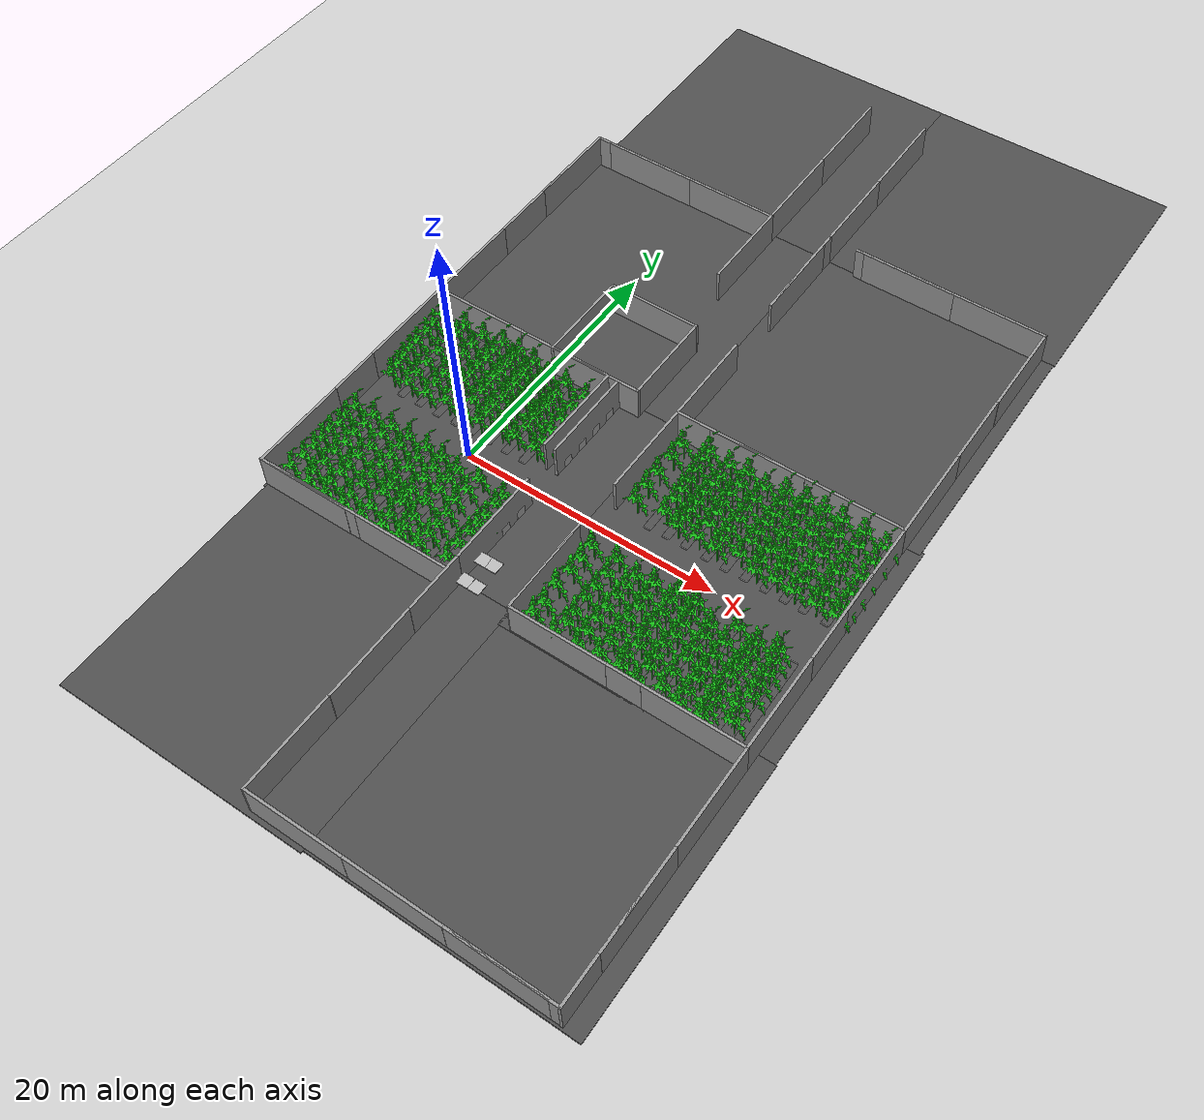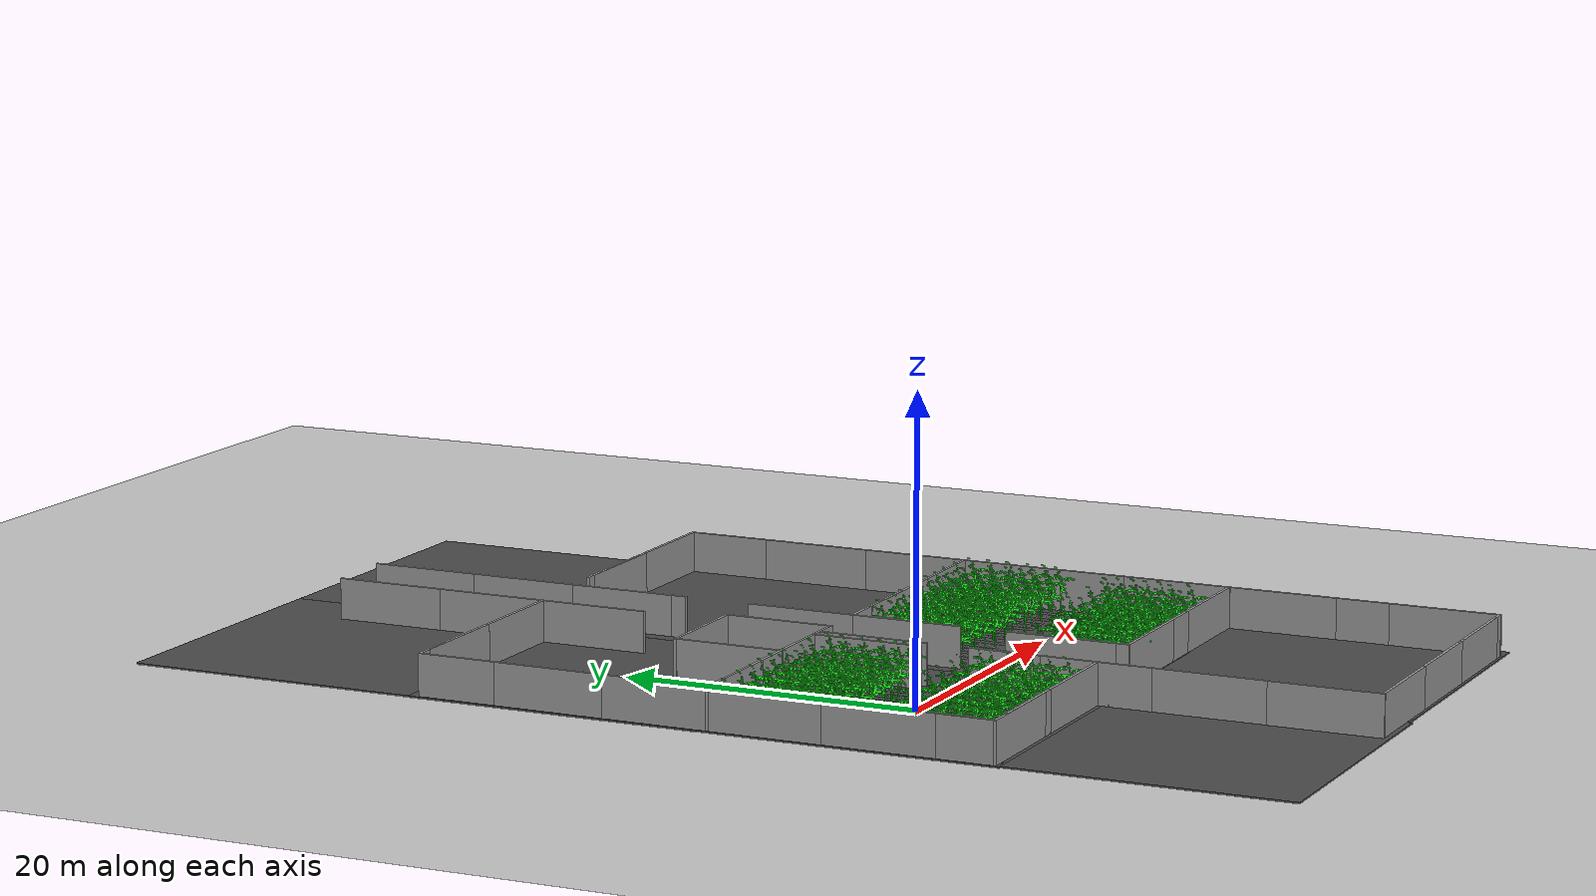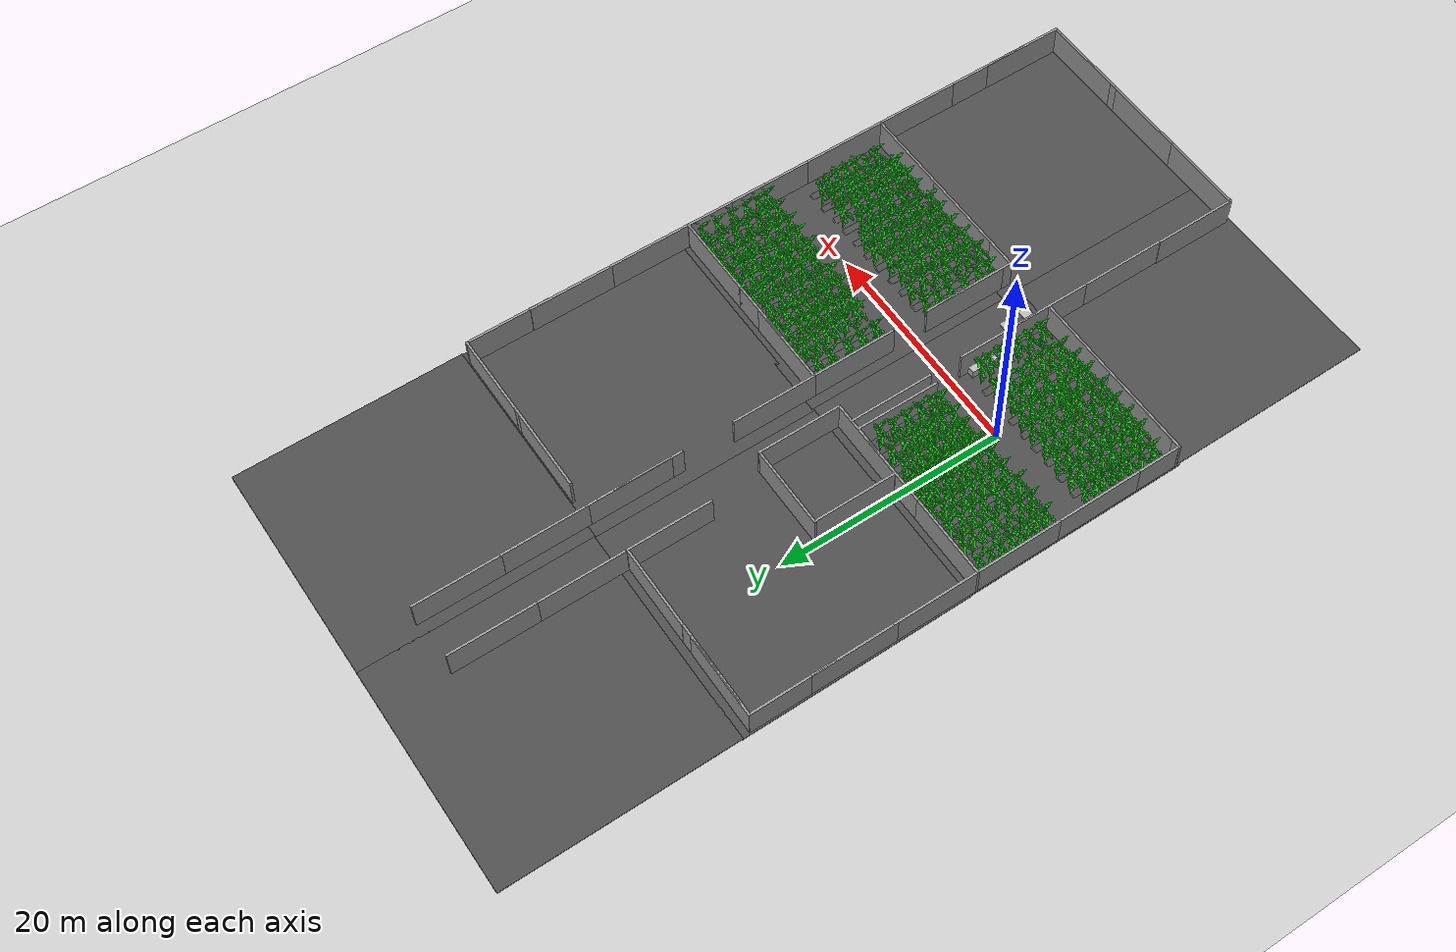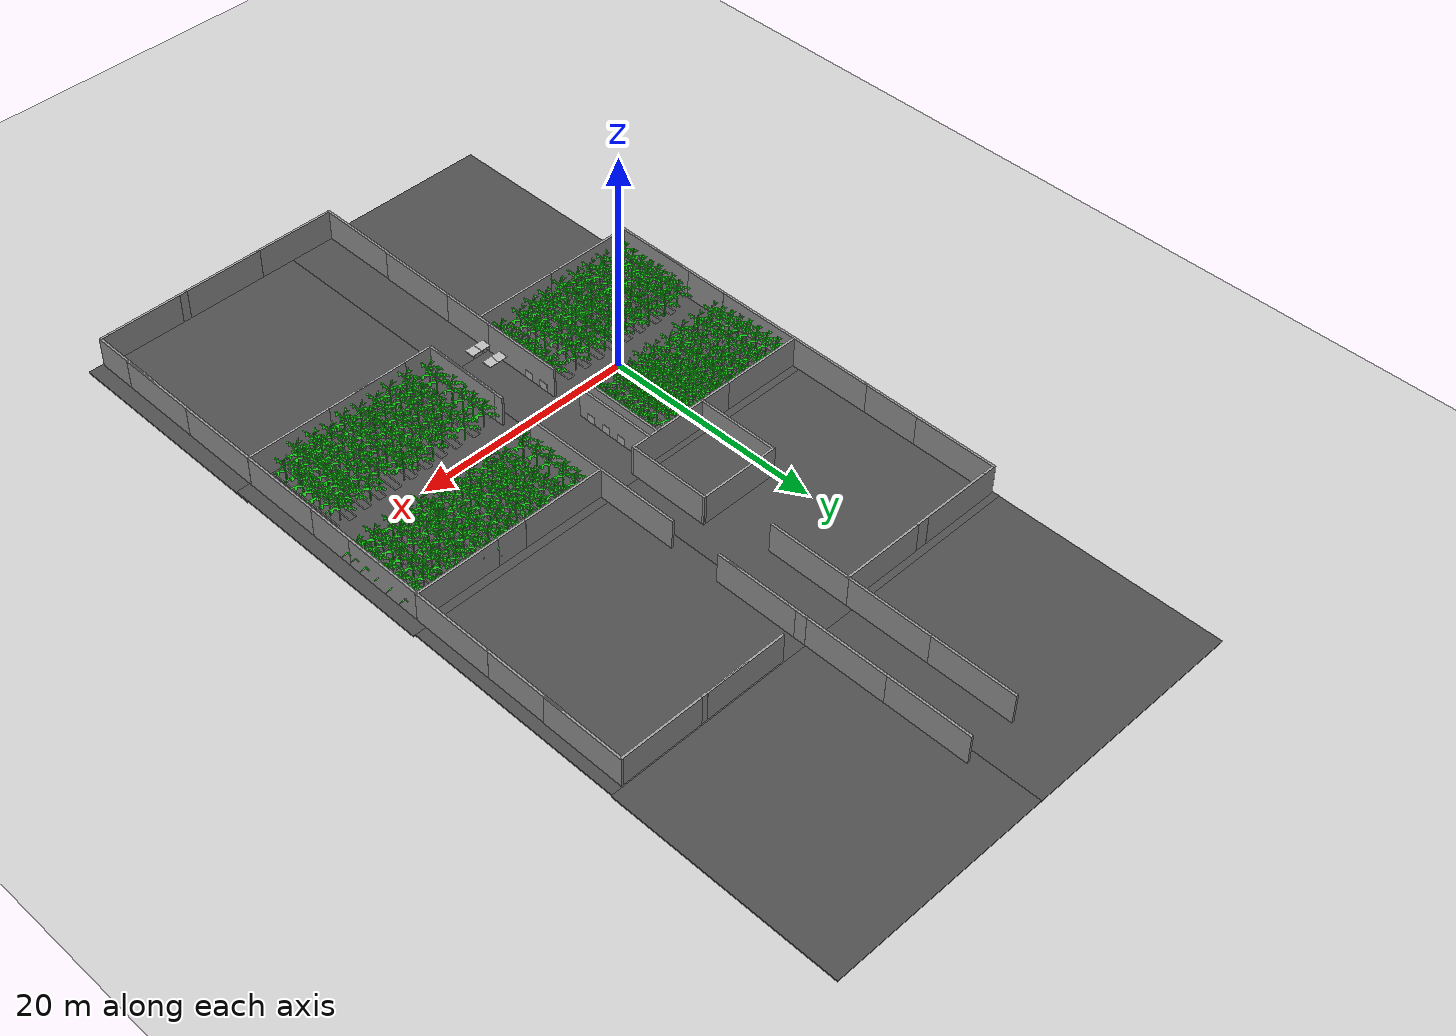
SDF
<sdf version="1.7">
 <world name="default">
  <plugin name="gazebo_link_attacher" filename="libgazebo_link_attacher.so"/>
  <light name="sun" type="directional">
   <pose>0 0 10 0 -0 0</pose>
   <diffuse>0.8 0.8 0.8 1</diffuse>
   <specular>0.2 0.2 0.2 1</specular>
   <attenuation>
    <range>1000</range>
    <constant>0.9</constant>
    <linear>0.01</linear>
    <quadratic>0.001</quadratic>
   </attenuation>
   <direction>-0.5 0.1 -0.9</direction>
   <spot><inner_angle>0</inner_angle><outer_angle>0</outer_angle><falloff>0</falloff></spot>
  </light>
  <model name="ground_plane">
   <static>1</static>
   <link name="link">
    <collision name="collision">
     <geometry><plane><normal>0 0 1</normal><size>100 100</size></plane></geometry>
     <surface><friction><ode><mu>100</mu><mu2>50</mu2></ode></friction></surface>
    </collision>
    <visual name="visual">
     <cast_shadows>0</cast_shadows>
     <geometry><plane><normal>0 0 1</normal><size>100 100</size></plane></geometry>
     <material>
      <script><uri>file://media/materials/scripts/gazebo.material</uri><name>Gazebo/Grey</name></script>
     </material>
    </visual>
   </link>
  </model>
  <gravity>0 0 -9.8</gravity>
  <magnetic_field>6e-06 2.3e-05 -4.2e-05</magnetic_field>
  <atmosphere type="adiabatic"/>
  <physics type="ode">
   <max_step_size>0.001</max_step_size>
   <real_time_factor>1</real_time_factor>
   <real_time_update_rate>1000</real_time_update_rate>
  </physics>
  <scene><ambient>0.4 0.4 0.4 1</ambient><background>0.7 0.7 0.7 1</background><shadows>1</shadows></scene>
  <spherical_coordinates>
   <surface_model>EARTH_WGS84</surface_model>
   <latitude_deg>0</latitude_deg>
   <longitude_deg>0</longitude_deg>
   <elevation>0</elevation>
   <heading_deg>0</heading_deg>
  </spherical_coordinates>
  <light name="user_directional_light_0" type="directional">
   <pose>-5.63054 -11.2657 1 0 -0 0</pose>
   <diffuse>0.5 0.5 0.5 1</diffuse>
   <specular>0.1 0.1 0.1 1</specular>
   <direction>0.1 0.1 -0.9</direction>
   <attenuation>
    <range>20</range>
    <constant>0.5</constant>
    <linear>0.01</linear>
    <quadratic>0.001</quadratic>
   </attenuation>
   <spot><inner_angle>0</inner_angle><outer_angle>0</outer_angle><falloff>0</falloff></spot>
  </light>
  <light name="user_directional_light_1" type="directional">
   <pose>10.4762 9.60881 1 0 -0 0</pose>
   <diffuse>0.5 0.5 0.5 1</diffuse>
   <specular>0.1 0.1 0.1 1</specular>
   <direction>0.1 0.1 -0.9</direction>
   <attenuation>
    <range>20</range>
    <constant>0.5</constant>
    <linear>0.01</linear>
    <quadratic>0.001</quadratic>
   </attenuation>
   <spot><inner_angle>0</inner_angle><outer_angle>0</outer_angle><falloff>0</falloff></spot>
  </light>
  <audio><device>default</device></audio>
  <model name="piperail">
   <static>1</static>
   <link name="link">
    <collision name="collision">
     <geometry>
      <mesh><scale>0.001 0.001 0.001</scale><uri>model://piperail/meshes/piperail.STL</uri></mesh>
     </geometry>
    </collision>
    <visual name="visual">
     <geometry>
      <mesh><scale>0.001 0.001 0.001</scale><uri>model://piperail/meshes/piperail.STL</uri></mesh>
     </geometry>
    </visual>
   </link>
   <pose>0 -1.5 0.05 1.57 -0 0</pose>
  </model>
  <model name="plant">
   <static>1</static>
   <link name="link">
    <visual name="visual">
     <geometry><mesh><scale>0.01 0.01 0.01</scale><uri>model://plant/meshes/plant.STL</uri></mesh></geometry>
     <material>
      <ambient>0.1 0.8 0.1 1</ambient>
      <diffuse>0.1 0.8 0.1 1</diffuse>
      <specular>0.01 0.01 0.01 1</specular>
      <emissive>0 0 0 1</emissive>
     </material>
    </visual>
   </link>
   <pose>1.77763 -1.13342 -0.001164 1.57 -0 0</pose>
  </model>
  <model name="plant_clone">
   <static>1</static>
   <link name="link">
    <visual name="visual">
     <geometry><mesh><scale>0.01 0.01 0.01</scale><uri>model://plant/meshes/plant.STL</uri></mesh></geometry>
     <material>
      <ambient>0.1 0.8 0.1 1</ambient>
      <diffuse>0.1 0.8 0.1 1</diffuse>
      <specular>0.01 0.01 0.01 1</specular>
      <emissive>0 0 0 1</emissive>
     </material>
    </visual>
   </link>
   <pose>1.66545 -2.31829 0.002201 1.57 -0 0</pose>
  </model>
  <model name="plant_clone_0">
   <static>1</static>
   <link name="link">
    <visual name="visual">
     <geometry><mesh><scale>0.01 0.01 0.01</scale><uri>model://plant/meshes/plant.STL</uri></mesh></geometry>
     <material>
      <ambient>0.1 0.8 0.1 1</ambient>
      <diffuse>0.1 0.8 0.1 1</diffuse>
      <specular>0.01 0.01 0.01 1</specular>
      <emissive>0 0 0 1</emissive>
     </material>
    </visual>
   </link>
   <pose>1.5257 -3.44822 0.004669 1.57 -0 0</pose>
  </model>
  <model name="plant_clone_1">
   <static>1</static>
   <link name="link">
    <visual name="visual">
     <geometry><mesh><scale>0.01 0.01 0.01</scale><uri>model://plant/meshes/plant.STL</uri></mesh></geometry>
     <material>
      <ambient>0.1 0.8 0.1 1</ambient>
      <diffuse>0.1 0.8 0.1 1</diffuse>
      <specular>0.01 0.01 0.01 1</specular>
      <emissive>0 0 0 1</emissive>
     </material>
    </visual>
   </link>
   <pose>1.49228 3.17394 0.000845 1.57 -0 0</pose>
  </model>
  <model name="plant_clone_2">
   <static>1</static>
   <link name="link">
    <visual name="visual">
     <geometry><mesh><scale>0.01 0.01 0.01</scale><uri>model://plant/meshes/plant.STL</uri></mesh></geometry>
     <material>
      <ambient>0.1 0.8 0.1 1</ambient>
      <diffuse>0.1 0.8 0.1 1</diffuse>
      <specular>0.01 0.01 0.01 1</specular>
      <emissive>0 0 0 1</emissive>
     </material>
    </visual>
   </link>
   <pose>1.68663 4.1733 0.001925 1.57 -0 0</pose>
  </model>
  <model name="piperail_clone">
   <static>1</static>
   <link name="link">
    <collision name="collision">
     <geometry>
      <mesh><scale>0.001 0.001 0.001</scale><uri>model://piperail/meshes/piperail.STL</uri></mesh>
     </geometry>
    </collision>
    <visual name="visual">
     <geometry>
      <mesh><scale>0.001 0.001 0.001</scale><uri>model://piperail/meshes/piperail.STL</uri></mesh>
     </geometry>
    </visual>
   </link>
   <pose>-0.016211 9 0.05 1.57 -0 0</pose>
  </model>
  <model name="piperail_clone_0">
   <static>1</static>
   <link name="link">
    <collision name="collision">
     <geometry>
      <mesh><scale>0.001 0.001 0.001</scale><uri>model://piperail/meshes/piperail.STL</uri></mesh>
     </geometry>
    </collision>
    <visual name="visual">
     <geometry>
      <mesh><scale>0.001 0.001 0.001</scale><uri>model://piperail/meshes/piperail.STL</uri></mesh>
     </geometry>
    </visual>
   </link>
   <pose>1.5 -1.5 0.05 1.57 -0 0</pose>
  </model>
  <model name="piperail_clone_1">
   <static>1</static>
   <link name="link">
    <collision name="collision">
     <geometry>
      <mesh><scale>0.001 0.001 0.001</scale><uri>model://piperail/meshes/piperail.STL</uri></mesh>
     </geometry>
    </collision>
    <visual name="visual">
     <geometry>
      <mesh><scale>0.001 0.001 0.001</scale><uri>model://piperail/meshes/piperail.STL</uri></mesh>
     </geometry>
    </visual>
   </link>
   <pose>3.3 -1.5 0.05 1.57 -0 0</pose>
  </model>
  <model name="piperail_clone_2">
   <static>1</static>
   <link name="link">
    <collision name="collision">
     <geometry>
      <mesh><scale>0.001 0.001 0.001</scale><uri>model://piperail/meshes/piperail.STL</uri></mesh>
     </geometry>
    </collision>
    <visual name="visual">
     <geometry>
      <mesh><scale>0.001 0.001 0.001</scale><uri>model://piperail/meshes/piperail.STL</uri></mesh>
     </geometry>
    </visual>
   </link>
   <pose>-1.5 -1.5 0.05 1.57 -0 0</pose>
  </model>
  <model name="piperail_clone_3">
   <static>1</static>
   <link name="link">
    <collision name="collision">
     <geometry>
      <mesh><scale>0.001 0.001 0.001</scale><uri>model://piperail/meshes/piperail.STL</uri></mesh>
     </geometry>
    </collision>
    <visual name="visual">
     <geometry>
      <mesh><scale>0.001 0.001 0.001</scale><uri>model://piperail/meshes/piperail.STL</uri></mesh>
     </geometry>
    </visual>
   </link>
   <pose>-3 -1.5 0.05 1.57 -0 0</pose>
  </model>
  <model name="piperail_clone_4">
   <static>1</static>
   <link name="link">
    <collision name="collision">
     <geometry>
      <mesh><scale>0.001 0.001 0.001</scale><uri>model://piperail/meshes/piperail.STL</uri></mesh>
     </geometry>
    </collision>
    <visual name="visual">
     <geometry>
      <mesh><scale>0.001 0.001 0.001</scale><uri>model://piperail/meshes/piperail.STL</uri></mesh>
     </geometry>
    </visual>
   </link>
   <pose>-1.5 9 0.05 1.57 -0 0</pose>
  </model>
  <model name="piperail_clone_5">
   <static>1</static>
   <link name="link">
    <collision name="collision">
     <geometry>
      <mesh><scale>0.001 0.001 0.001</scale><uri>model://piperail/meshes/piperail.STL</uri></mesh>
     </geometry>
    </collision>
    <visual name="visual">
     <geometry>
      <mesh><scale>0.001 0.001 0.001</scale><uri>model://piperail/meshes/piperail.STL</uri></mesh>
     </geometry>
    </visual>
   </link>
   <pose>-3 9 0.05 1.57 -0 0</pose>
  </model>
  <model name="piperail_clone_6">
   <static>1</static>
   <link name="link">
    <collision name="collision">
     <geometry>
      <mesh><scale>0.001 0.001 0.001</scale><uri>model://piperail/meshes/piperail.STL</uri></mesh>
     </geometry>
    </collision>
    <visual name="visual">
     <geometry>
      <mesh><scale>0.001 0.001 0.001</scale><uri>model://piperail/meshes/piperail.STL</uri></mesh>
     </geometry>
    </visual>
   </link>
   <pose>1.5 9 0.05 1.57 -0 0</pose>
  </model>
  <model name="piperail_clone_7">
   <static>1</static>
   <link name="link">
    <collision name="collision">
     <geometry>
      <mesh><scale>0.001 0.001 0.001</scale><uri>model://piperail/meshes/piperail.STL</uri></mesh>
     </geometry>
    </collision>
    <visual name="visual">
     <geometry>
      <mesh><scale>0.001 0.001 0.001</scale><uri>model://piperail/meshes/piperail.STL</uri></mesh>
     </geometry>
    </visual>
   </link>
   <pose>3 9 0.05 1.57 -0 0</pose>
  </model>
  <model name="plant_clone_1_clone">
   <static>1</static>
   <link name="link">
    <visual name="visual">
     <geometry><mesh><scale>0.01 0.01 0.01</scale><uri>model://plant/meshes/plant.STL</uri></mesh></geometry>
     <material>
      <ambient>0.1 0.8 0.1 1</ambient>
      <diffuse>0.1 0.8 0.1 1</diffuse>
      <specular>0.01 0.01 0.01 1</specular>
      <emissive>0 0 0 1</emissive>
     </material>
    </visual>
   </link>
   <pose>0.017412 4.30864 0.000845 1.57 -0 0</pose>
  </model>
  <model name="plant_clone_1_clone_0">
   <static>1</static>
   <link name="link">
    <visual name="visual">
     <geometry><mesh><scale>0.01 0.01 0.01</scale><uri>model://plant/meshes/plant.STL</uri></mesh></geometry>
     <material>
      <ambient>0.1 0.8 0.1 1</ambient>
      <diffuse>0.1 0.8 0.1 1</diffuse>
      <specular>0.01 0.01 0.01 1</specular>
      <emissive>0 0 0 1</emissive>
     </material>
    </visual>
   </link>
   <pose>0.140209 3.43982 0.000845 1.57 -0 0</pose>
  </model>
  <model name="plant_clone_1_clone_1">
   <static>1</static>
   <link name="link">
    <visual name="visual">
     <geometry><mesh><scale>0.01 0.01 0.01</scale><uri>model://plant/meshes/plant.STL</uri></mesh></geometry>
     <material>
      <ambient>0.1 0.8 0.1 1</ambient>
      <diffuse>0.1 0.8 0.1 1</diffuse>
      <specular>0.01 0.01 0.01 1</specular>
      <emissive>0 0 0 1</emissive>
     </material>
    </visual>
   </link>
   <pose>0.218511 3.06385 0.000845 1.57 -0 0</pose>
  </model>
  <model name="plant_clone_1_clone_2">
   <static>1</static>
   <link name="link">
    <visual name="visual">
     <geometry><mesh><scale>0.01 0.01 0.01</scale><uri>model://plant/meshes/plant.STL</uri></mesh></geometry>
     <material>
      <ambient>0.1 0.8 0.1 1</ambient>
      <diffuse>0.1 0.8 0.1 1</diffuse>
      <specular>0.01 0.01 0.01 1</specular>
      <emissive>0 0 0 1</emissive>
     </material>
    </visual>
   </link>
   <pose>-1.38801 4.52892 0.000845 1.57 -0 0</pose>
  </model>
  <model name="plant_clone_1_clone_3">
   <static>1</static>
   <link name="link">
    <visual name="visual">
     <geometry><mesh><scale>0.01 0.01 0.01</scale><uri>model://plant/meshes/plant.STL</uri></mesh></geometry>
     <material>
      <ambient>0.1 0.8 0.1 1</ambient>
      <diffuse>0.1 0.8 0.1 1</diffuse>
      <specular>0.01 0.01 0.01 1</specular>
      <emissive>0 0 0 1</emissive>
     </material>
    </visual>
   </link>
   <pose>-1.34584 3.71141 0.000845 1.57 -0 0</pose>
  </model>
  <model name="plant_clone_1_clone_4">
   <static>1</static>
   <link name="link">
    <visual name="visual">
     <geometry><mesh><scale>0.01 0.01 0.01</scale><uri>model://plant/meshes/plant.STL</uri></mesh></geometry>
     <material>
      <ambient>0.1 0.8 0.1 1</ambient>
      <diffuse>0.1 0.8 0.1 1</diffuse>
      <specular>0.01 0.01 0.01 1</specular>
      <emissive>0 0 0 1</emissive>
     </material>
    </visual>
   </link>
   <pose>-1.48013 2.86029 0.000845 1.57 -0 0</pose>
  </model>
  <model name="plant_clone_1_clone_5">
   <static>1</static>
   <link name="link">
    <visual name="visual">
     <geometry><mesh><scale>0.01 0.01 0.01</scale><uri>model://plant/meshes/plant.STL</uri></mesh></geometry>
     <material>
      <ambient>0.1 0.8 0.1 1</ambient>
      <diffuse>0.1 0.8 0.1 1</diffuse>
      <specular>0.01 0.01 0.01 1</specular>
      <emissive>0 0 0 1</emissive>
     </material>
    </visual>
   </link>
   <pose>-2.86965 5.0816 0.000845 1.57 -0 0</pose>
  </model>
  <model name="plant_clone_1_clone_6">
   <static>1</static>
   <link name="link">
    <visual name="visual">
     <geometry><mesh><scale>0.01 0.01 0.01</scale><uri>model://plant/meshes/plant.STL</uri></mesh></geometry>
     <material>
      <ambient>0.1 0.8 0.1 1</ambient>
      <diffuse>0.1 0.8 0.1 1</diffuse>
      <specular>0.01 0.01 0.01 1</specular>
      <emissive>0 0 0 1</emissive>
     </material>
    </visual>
   </link>
   <pose>-2.84798 4.0609 0.000845 1.57 -0 0</pose>
  </model>
  <model name="plant_clone_1_clone_7">
   <static>1</static>
   <link name="link">
    <visual name="visual">
     <geometry><mesh><scale>0.01 0.01 0.01</scale><uri>model://plant/meshes/plant.STL</uri></mesh></geometry>
     <material>
      <ambient>0.1 0.8 0.1 1</ambient>
      <diffuse>0.1 0.8 0.1 1</diffuse>
      <specular>0.01 0.01 0.01 1</specular>
      <emissive>0 0 0 1</emissive>
     </material>
    </visual>
   </link>
   <pose>-2.81594 2.86917 0.000845 1.57 -0 0</pose>
  </model>
  <model name="plant_clone_1_clone_8">
   <static>1</static>
   <link name="link">
    <visual name="visual">
     <geometry><mesh><scale>0.01 0.01 0.01</scale><uri>model://plant/meshes/plant.STL</uri></mesh></geometry>
     <material>
      <ambient>0.1 0.8 0.1 1</ambient>
      <diffuse>0.1 0.8 0.1 1</diffuse>
      <specular>0.01 0.01 0.01 1</specular>
      <emissive>0 0 0 1</emissive>
     </material>
    </visual>
   </link>
   <pose>1.55643 4.99352 0.000845 1.57 -0 0</pose>
  </model>
  <model name="plant_clone_1_clone_9">
   <static>1</static>
   <link name="link">
    <visual name="visual">
     <geometry><mesh><scale>0.01 0.01 0.01</scale><uri>model://plant/meshes/plant.STL</uri></mesh></geometry>
     <material>
      <ambient>0.1 0.8 0.1 1</ambient>
      <diffuse>0.1 0.8 0.1 1</diffuse>
      <specular>0.01 0.01 0.01 1</specular>
      <emissive>0 0 0 1</emissive>
     </material>
    </visual>
   </link>
   <pose>0.112161 -1.39635 0.000845 1.57 -0 0</pose>
  </model>
  <model name="plant_clone_1_clone_10">
   <static>1</static>
   <link name="link">
    <visual name="visual">
     <geometry><mesh><scale>0.01 0.01 0.01</scale><uri>model://plant/meshes/plant.STL</uri></mesh></geometry>
     <material>
      <ambient>0.1 0.8 0.1 1</ambient>
      <diffuse>0.1 0.8 0.1 1</diffuse>
      <specular>0.01 0.01 0.01 1</specular>
      <emissive>0 0 0 1</emissive>
     </material>
    </visual>
   </link>
   <pose>0.130082 -2.29707 0.000845 1.57 -0 0</pose>
  </model>
  <model name="plant_clone_1_clone_11">
   <static>1</static>
   <link name="link">
    <visual name="visual">
     <geometry><mesh><scale>0.01 0.01 0.01</scale><uri>model://plant/meshes/plant.STL</uri></mesh></geometry>
     <material>
      <ambient>0.1 0.8 0.1 1</ambient>
      <diffuse>0.1 0.8 0.1 1</diffuse>
      <specular>0.01 0.01 0.01 1</specular>
      <emissive>0 0 0 1</emissive>
     </material>
    </visual>
   </link>
   <pose>0.121458 -3.34587 0.000845 1.57 -0 0</pose>
  </model>
  <model name="plant_clone_1_clone_12">
   <static>1</static>
   <link name="link">
    <visual name="visual">
     <geometry><mesh><scale>0.01 0.01 0.01</scale><uri>model://plant/meshes/plant.STL</uri></mesh></geometry>
     <material>
      <ambient>0.1 0.8 0.1 1</ambient>
      <diffuse>0.1 0.8 0.1 1</diffuse>
      <specular>0.01 0.01 0.01 1</specular>
      <emissive>0 0 0 1</emissive>
     </material>
    </visual>
   </link>
   <pose>-1.38485 -1.1272 0.000845 1.57 -0 0</pose>
  </model>
  <model name="plant_clone_1_clone_13">
   <static>1</static>
   <link name="link">
    <visual name="visual">
     <geometry><mesh><scale>0.01 0.01 0.01</scale><uri>model://plant/meshes/plant.STL</uri></mesh></geometry>
     <material>
      <ambient>0.1 0.8 0.1 1</ambient>
      <diffuse>0.1 0.8 0.1 1</diffuse>
      <specular>0.01 0.01 0.01 1</specular>
      <emissive>0 0 0 1</emissive>
     </material>
    </visual>
   </link>
   <pose>-1.29326 -2.14513 0.000845 1.57 -0 0</pose>
  </model>
  <model name="plant_clone_1_clone_14">
   <static>1</static>
   <link name="link">
    <visual name="visual">
     <geometry><mesh><scale>0.01 0.01 0.01</scale><uri>model://plant/meshes/plant.STL</uri></mesh></geometry>
     <material>
      <ambient>0.1 0.8 0.1 1</ambient>
      <diffuse>0.1 0.8 0.1 1</diffuse>
      <specular>0.01 0.01 0.01 1</specular>
      <emissive>0 0 0 1</emissive>
     </material>
    </visual>
   </link>
   <pose>-1.26249 -3.15905 0.000845 1.57 -0 0</pose>
  </model>
  <model name="plant_clone_1_clone_15">
   <static>1</static>
   <link name="link">
    <visual name="visual">
     <geometry><mesh><scale>0.01 0.01 0.01</scale><uri>model://plant/meshes/plant.STL</uri></mesh></geometry>
     <material>
      <ambient>0.1 0.8 0.1 1</ambient>
      <diffuse>0.1 0.8 0.1 1</diffuse>
      <specular>0.01 0.01 0.01 1</specular>
      <emissive>0 0 0 1</emissive>
     </material>
    </visual>
   </link>
   <pose>-2.79115 -1.01945 0.000845 1.57 -0 0</pose>
  </model>
  <model name="plant_clone_1_clone_16">
   <static>1</static>
   <link name="link">
    <visual name="visual">
     <geometry><mesh><scale>0.01 0.01 0.01</scale><uri>model://plant/meshes/plant.STL</uri></mesh></geometry>
     <material>
      <ambient>0.1 0.8 0.1 1</ambient>
      <diffuse>0.1 0.8 0.1 1</diffuse>
      <specular>0.01 0.01 0.01 1</specular>
      <emissive>0 0 0 1</emissive>
     </material>
    </visual>
   </link>
   <pose>-2.76366 -2.09337 0.000845 1.57 -0 0</pose>
  </model>
  <model name="plant_clone_1_clone_17">
   <static>1</static>
   <link name="link">
    <visual name="visual">
     <geometry><mesh><scale>0.01 0.01 0.01</scale><uri>model://plant/meshes/plant.STL</uri></mesh></geometry>
     <material>
      <ambient>0.1 0.8 0.1 1</ambient>
      <diffuse>0.1 0.8 0.1 1</diffuse>
      <specular>0.01 0.01 0.01 1</specular>
      <emissive>0 0 0 1</emissive>
     </material>
    </visual>
   </link>
   <pose>-2.75946 -3.03792 0.000845 1.57 -0 0</pose>
  </model>
  <model name="plant_clone_1_clone_19">
   <static>1</static>
   <link name="link">
    <visual name="visual">
     <geometry><mesh><scale>0.01 0.01 0.01</scale><uri>model://plant/meshes/plant.STL</uri></mesh></geometry>
     <material>
      <ambient>0.1 0.8 0.1 1</ambient>
      <diffuse>0.1 0.8 0.1 1</diffuse>
      <specular>0.01 0.01 0.01 1</specular>
      <emissive>0 0 0 1</emissive>
     </material>
    </visual>
   </link>
   <pose>3.972 -2.18792 0.000845 1.57 -0 0</pose>
  </model>
  <model name="plant_clone_1_clone_20">
   <static>1</static>
   <link name="link">
    <visual name="visual">
     <geometry><mesh><scale>0.01 0.01 0.01</scale><uri>model://plant/meshes/plant.STL</uri></mesh></geometry>
     <material>
      <ambient>0.1 0.8 0.1 1</ambient>
      <diffuse>0.1 0.8 0.1 1</diffuse>
      <specular>0.01 0.01 0.01 1</specular>
      <emissive>0 0 0 1</emissive>
     </material>
    </visual>
   </link>
   <pose>4.03807 -3.30841 0.000845 1.57 -0 0</pose>
  </model>
  <model name="plant_clone_1_clone_21">
   <static>1</static>
   <link name="link">
    <visual name="visual">
     <geometry><mesh><scale>0.01 0.01 0.01</scale><uri>model://plant/meshes/plant.STL</uri></mesh></geometry>
     <material>
      <ambient>0.1 0.8 0.1 1</ambient>
      <diffuse>0.1 0.8 0.1 1</diffuse>
      <specular>0.01 0.01 0.01 1</specular>
      <emissive>0 0 0 1</emissive>
     </material>
    </visual>
   </link>
   <pose>3.36217 4.88797 0.000845 1.57 -0 0</pose>
  </model>
  <model name="plant_clone_1_clone_22">
   <static>1</static>
   <link name="link">
    <visual name="visual">
     <geometry><mesh><scale>0.01 0.01 0.01</scale><uri>model://plant/meshes/plant.STL</uri></mesh></geometry>
     <material>
      <ambient>0.1 0.8 0.1 1</ambient>
      <diffuse>0.1 0.8 0.1 1</diffuse>
      <specular>0.01 0.01 0.01 1</specular>
      <emissive>0 0 0 1</emissive>
     </material>
    </visual>
   </link>
   <pose>3.34479 3.86027 0.000845 1.57 -0 0</pose>
  </model>
  <model name="plant_clone_1_clone_23">
   <static>1</static>
   <link name="link">
    <visual name="visual">
     <geometry><mesh><scale>0.01 0.01 0.01</scale><uri>model://plant/meshes/plant.STL</uri></mesh></geometry>
     <material>
      <ambient>0.1 0.8 0.1 1</ambient>
      <diffuse>0.1 0.8 0.1 1</diffuse>
      <specular>0.01 0.01 0.01 1</specular>
      <emissive>0 0 0 1</emissive>
     </material>
    </visual>
   </link>
   <pose>3.18776 3.098 0.000845 1.57 -0 0</pose>
  </model>
  <model name="grey_wall_clone">
   <static>1</static>
   <link name="link">
    <pose>0 0 1.4 0 -0 0</pose>
    <collision name="collision"><geometry><box><size>7.5 0.2 2.8</size></box></geometry></collision>
    <visual name="visual">
     <cast_shadows>0</cast_shadows>
     <geometry><box><size>7.5 0.2 2.8</size></box></geometry>
     <material>
      <script>
       <uri>model://grey_wall/materials/scripts</uri>
       <uri>model://grey_wall/materials/textures</uri>
       <name>vrc/grey_wall</name>
      </script>
     </material>
    </visual>
   </link>
   <pose>6 5.75 0 0 -0 1.57</pose>
  </model>
  <model name="grey_wall_clone_clone">
   <static>1</static>
   <link name="link">
    <pose>0 0 1.4 0 -0 0</pose>
    <collision name="collision"><geometry><box><size>7.5 0.2 2.8</size></box></geometry></collision>
    <visual name="visual">
     <cast_shadows>0</cast_shadows>
     <geometry><box><size>7.5 0.2 2.8</size></box></geometry>
     <material>
      <script>
       <uri>model://grey_wall/materials/scripts</uri>
       <uri>model://grey_wall/materials/textures</uri>
       <name>vrc/grey_wall</name>
      </script>
     </material>
    </visual>
   </link>
   <pose>11 5.62968 0 0 -0 1.57</pose>
  </model>
  <model name="grey_wall_clone_clone_1">
   <static>1</static>
   <link name="link">
    <pose>0 0 1.4 0 -0 0</pose>
    <collision name="collision"><geometry><box><size>7.5 0.2 2.8</size></box></geometry></collision>
    <visual name="visual">
     <cast_shadows>0</cast_shadows>
     <geometry><box><size>7.5 0.2 2.8</size></box></geometry>
     <material>
      <script>
       <uri>model://grey_wall/materials/scripts</uri>
       <uri>model://grey_wall/materials/textures</uri>
       <name>vrc/grey_wall</name>
      </script>
     </material>
    </visual>
   </link>
   <pose>5.99553 -4.61755 0 0 -0 1.57</pose>
  </model>
  <model name="grey_wall_clone_clone_0_clone">
   <static>1</static>
   <link name="link">
    <pose>0 0 1.4 0 -0 0</pose>
    <collision name="collision"><geometry><box><size>7.5 0.2 2.8</size></box></geometry></collision>
    <visual name="visual">
     <cast_shadows>0</cast_shadows>
     <geometry><box><size>7.5 0.2 2.8</size></box></geometry>
     <material>
      <script>
       <uri>model://grey_wall/materials/scripts</uri>
       <uri>model://grey_wall/materials/textures</uri>
       <name>vrc/grey_wall</name>
      </script>
     </material>
    </visual>
   </link>
   <pose>11 -5.87182 0 0 -0 1.57</pose>
  </model>
  <model name="grey_wall_clone_clone_1_clone">
   <static>1</static>
   <link name="link">
    <pose>0 0 1.4 0 -0 0</pose>
    <collision name="collision"><geometry><box><size>7.5 0.2 2.8</size></box></geometry></collision>
    <visual name="visual">
     <cast_shadows>0</cast_shadows>
     <geometry><box><size>7.5 0.2 2.8</size></box></geometry>
     <material>
      <script>
       <uri>model://grey_wall/materials/scripts</uri>
       <uri>model://grey_wall/materials/textures</uri>
       <name>vrc/grey_wall</name>
      </script>
     </material>
    </visual>
   </link>
   <pose>5.98359 -9.46121 0 0 -0 1.57</pose>
  </model>
  <model name="cafe_table">
   <static>1</static>
   <link name="link">
    <collision name="surface">
     <pose>0 0 0.755 0 -0 0</pose>
     <geometry><box><size>0.913 0.913 0.04</size></box></geometry>
    </collision>
    <collision name="column">
     <pose>0 0 0.37 0 -0 0</pose>
     <geometry><box><size>0.042 0.042 0.74</size></box></geometry>
    </collision>
    <collision name="base">
     <pose>0 0 0.02 0 -0 0</pose>
     <geometry><box><size>0.56 0.56 0.04</size></box></geometry>
    </collision>
    <visual name="visual">
     <geometry><mesh><uri>model://cafe_table/meshes/cafe_table.dae</uri></mesh></geometry>
    </visual>
   </link>
   <pose>6.58649 -8.57944 0 0 -0 0</pose>
  </model>
  <model name="cafe_table_clone">
   <static>1</static>
   <link name="link">
    <collision name="surface">
     <pose>0 0 0.755 0 -0 0</pose>
     <geometry><box><size>0.913 0.913 0.04</size></box></geometry>
    </collision>
    <collision name="column">
     <pose>0 0 0.37 0 -0 0</pose>
     <geometry><box><size>0.042 0.042 0.74</size></box></geometry>
    </collision>
    <collision name="base">
     <pose>0 0 0.02 0 -0 0</pose>
     <geometry><box><size>0.56 0.56 0.04</size></box></geometry>
    </collision>
    <visual name="visual">
     <geometry><mesh><uri>model://cafe_table/meshes/cafe_table.dae</uri></mesh></geometry>
    </visual>
   </link>
   <pose>7.51863 -8.58481 0 0 -0 0</pose>
  </model>
  <model name="cafe_table_clone_clone">
   <static>1</static>
   <link name="link">
    <collision name="surface">
     <pose>0 0 0.755 0 -0 0</pose>
     <geometry><box><size>0.913 0.913 0.04</size></box></geometry>
    </collision>
    <collision name="column">
     <pose>0 0 0.37 0 -0 0</pose>
     <geometry><box><size>0.042 0.042 0.74</size></box></geometry>
    </collision>
    <collision name="base">
     <pose>0 0 0.02 0 -0 0</pose>
     <geometry><box><size>0.56 0.56 0.04</size></box></geometry>
    </collision>
    <visual name="visual">
     <geometry><mesh><uri>model://cafe_table/meshes/cafe_table.dae</uri></mesh></geometry>
    </visual>
   </link>
   <pose>6.53813 -6.66995 0 0 -0 0</pose>
  </model>
  <model name="cafe_table_clone_clone_0">
   <static>1</static>
   <link name="link">
    <collision name="surface">
     <pose>0 0 0.755 0 -0 0</pose>
     <geometry><box><size>0.913 0.913 0.04</size></box></geometry>
    </collision>
    <collision name="column">
     <pose>0 0 0.37 0 -0 0</pose>
     <geometry><box><size>0.042 0.042 0.74</size></box></geometry>
    </collision>
    <collision name="base">
     <pose>0 0 0.02 0 -0 0</pose>
     <geometry><box><size>0.56 0.56 0.04</size></box></geometry>
    </collision>
    <visual name="visual">
     <geometry><mesh><uri>model://cafe_table/meshes/cafe_table.dae</uri></mesh></geometry>
    </visual>
   </link>
   <pose>7.40882 -6.66009 0 0 -0 0</pose>
  </model>
  <model name="coke_can_clone_0">
   <link name="link">
    <inertial>
     <pose>0 0 0.06 0 -0 0</pose>
     <mass>0.39</mass>
     <inertia>
      <ixx>0.00055575</ixx>
      <ixy>0</ixy>
      <ixz>0</ixz>
      <iyy>0.00055575</iyy>
      <iyz>0</iyz>
      <izz>0.0001755</izz>
     </inertia>
    </inertial>
    <collision name="collision">
     <pose>0.003937 0.004724 -0.18 0 -0 0</pose>
     <geometry><mesh><uri>model://coke_can/meshes/coke_can.dae</uri></mesh></geometry>
     <surface>
      <friction><ode><mu>1</mu><mu2>1</mu2></ode></friction>
      <contact><ode><kp>1e+07</kp><kd>1</kd><min_depth>0.001</min_depth><max_vel>0.1</max_vel></ode></contact>
     </surface>
    </collision>
    <visual name="visual">
     <pose>0.003937 0.004724 -0.18 0 -0 0</pose>
     <geometry><mesh><uri>model://coke_can/meshes/coke_can.dae</uri></mesh></geometry>
    </visual>
   </link>
   <pose>5.79005 -10.3478 0.04743 -0.009854 0.00353 -0.226614</pose>
  </model>
  <model name="number1">
   <pose>5.71 8.13 0.4 0 -0 0</pose>
   <static>1</static>
   <link name="link">
    <visual name="visual">
     <geometry><mesh><uri>model://number1/meshes/number.dae</uri></mesh></geometry>
     <material>
      <script>
       <uri>model://number1/materials/scripts</uri>
       <uri>model://number1/materials/textures</uri>
       <name>Number/One</name>
      </script>
     </material>
    </visual>
   </link>
  </model>
  <model name="number2">
   <pose>5.71 6.5 0.4 0 -0 0</pose>
   <static>1</static>
   <link name="link">
    <visual name="visual">
     <geometry><mesh><uri>model://number1/meshes/number.dae</uri></mesh></geometry>
     <material>
      <script>
       <uri>model://number2/materials/scripts</uri>
       <uri>model://number2/materials/textures</uri>
       <name>Number/Two</name>
      </script>
     </material>
    </visual>
   </link>
  </model>
  <model name="number3">
   <pose>5.71 4.87 0.4 0 -0 0</pose>
   <static>1</static>
   <link name="link">
    <visual name="visual">
     <geometry><mesh><uri>model://number1/meshes/number.dae</uri></mesh></geometry>
     <material>
      <script>
       <uri>model://number3/materials/scripts</uri>
       <uri>model://number3/materials/textures</uri>
       <name>Number/Three</name>
      </script>
     </material>
    </visual>
   </link>
  </model>
  <model name="number4">
   <pose>5.71 3.24 0.4 0 -0 0</pose>
   <static>1</static>
   <link name="link">
    <visual name="visual">
     <geometry><mesh><uri>model://number1/meshes/number.dae</uri></mesh></geometry>
     <material>
      <script>
       <uri>model://number4/materials/scripts</uri>
       <uri>model://number4/materials/textures</uri>
       <name>Number/Four</name>
      </script>
     </material>
    </visual>
   </link>
  </model>
  <model name="number5">
   <pose>5.71 -2.09 0.4 0 -0 0</pose>
   <static>1</static>
   <link name="link">
    <visual name="visual">
     <geometry><mesh><uri>model://number1/meshes/number.dae</uri></mesh></geometry>
     <material>
      <script>
       <uri>model://number5/materials/scripts</uri>
       <uri>model://number5/materials/textures</uri>
       <name>Number/Five</name>
      </script>
     </material>
    </visual>
   </link>
  </model>
  <model name="grey_wall_clone_clone_2">
   <static>1</static>
   <link name="link">
    <pose>0 0 1.4 0 -0 0</pose>
    <collision name="collision"><geometry><box><size>7.5 0.2 2.8</size></box></geometry></collision>
    <visual name="visual">
     <cast_shadows>0</cast_shadows>
     <geometry><box><size>7.5 0.2 2.8</size></box></geometry>
     <material>
      <script>
       <uri>model://grey_wall/materials/scripts</uri>
       <uri>model://grey_wall/materials/textures</uri>
       <name>vrc/grey_wall</name>
      </script>
     </material>
    </visual>
   </link>
   <pose>5.14176 5.75828 0 0 -0 1.57</pose>
  </model>
  <model name="asphalt_plane">
   <static>1</static>
   <link name="link">
    <collision name="collision"><geometry><box><size>20 20 0.1</size></box></geometry></collision>
    <visual name="visual">
     <cast_shadows>0</cast_shadows>
     <geometry><box><size>20 20 0.1</size></box></geometry>
     <material>
      <script>
       <uri>model://asphalt_plane/materials/scripts</uri>
       <uri>model://asphalt_plane/materials/textures</uri>
       <name>vrc/asphalt</name>
      </script>
     </material>
    </visual>
   </link>
   <pose>0.007662 0.157905 0 0 -0 0</pose>
  </model>
  <model name="asphalt_plane_clone">
   <static>1</static>
   <link name="link">
    <collision name="collision"><geometry><box><size>20 20 0.1</size></box></geometry></collision>
    <visual name="visual">
     <cast_shadows>0</cast_shadows>
     <geometry><box><size>20 20 0.1</size></box></geometry>
     <material>
      <script>
       <uri>model://asphalt_plane/materials/scripts</uri>
       <uri>model://asphalt_plane/materials/textures</uri>
       <name>vrc/asphalt</name>
      </script>
     </material>
    </visual>
   </link>
   <pose>-0.039502 20.0509 0 0 -0 0</pose>
  </model>
  <model name="asphalt_plane_clone_clone">
   <static>1</static>
   <link name="link">
    <collision name="collision"><geometry><box><size>20 20 0.1</size></box></geometry></collision>
    <visual name="visual">
     <cast_shadows>0</cast_shadows>
     <geometry><box><size>20 20 0.1</size></box></geometry>
     <material>
      <script>
       <uri>model://asphalt_plane/materials/scripts</uri>
       <uri>model://asphalt_plane/materials/textures</uri>
       <name>vrc/asphalt</name>
      </script>
     </material>
    </visual>
   </link>
   <pose>20.0012 0.279422 0 0 -0 0</pose>
  </model>
  <model name="asphalt_plane_clone_clone_0">
   <static>1</static>
   <link name="link">
    <collision name="collision"><geometry><box><size>20 20 0.1</size></box></geometry></collision>
    <visual name="visual">
     <cast_shadows>0</cast_shadows>
     <geometry><box><size>20 20 0.1</size></box></geometry>
     <material>
      <script>
       <uri>model://asphalt_plane/materials/scripts</uri>
       <uri>model://asphalt_plane/materials/textures</uri>
       <name>vrc/asphalt</name>
      </script>
     </material>
    </visual>
   </link>
   <pose>19.8233 19.9822 0 0 -0 0</pose>
  </model>
  <model name="asphalt_plane_clone_clone_1">
   <static>1</static>
   <link name="link">
    <collision name="collision"><geometry><box><size>20 20 0.1</size></box></geometry></collision>
    <visual name="visual">
     <cast_shadows>0</cast_shadows>
     <geometry><box><size>20 20 0.1</size></box></geometry>
     <material>
      <script>
       <uri>model://asphalt_plane/materials/scripts</uri>
       <uri>model://asphalt_plane/materials/textures</uri>
       <name>vrc/asphalt</name>
      </script>
     </material>
    </visual>
   </link>
   <pose>20.0847 -18.2729 0 0 -0 0</pose>
  </model>
  <model name="asphalt_plane_clone_clone_2">
   <static>1</static>
   <link name="link">
    <collision name="collision"><geometry><box><size>20 20 0.1</size></box></geometry></collision>
    <visual name="visual">
     <cast_shadows>0</cast_shadows>
     <geometry><box><size>20 20 0.1</size></box></geometry>
     <material>
      <script>
       <uri>model://asphalt_plane/materials/scripts</uri>
       <uri>model://asphalt_plane/materials/textures</uri>
       <name>vrc/asphalt</name>
      </script>
     </material>
    </visual>
   </link>
   <pose>0.14456 -18.4475 0 0 -0 0</pose>
  </model>
  <model name="plant_clone_0_clone">
   <static>1</static>
   <link name="link">
    <visual name="visual">
     <geometry><mesh><scale>0.01 0.01 0.01</scale><uri>model://plant/meshes/plant.STL</uri></mesh></geometry>
     <material>
      <ambient>0.1 0.8 0.1 1</ambient>
      <diffuse>0.1 0.8 0.1 1</diffuse>
      <specular>0.01 0.01 0.01 1</specular>
      <emissive>0 0 0 1</emissive>
     </material>
    </visual>
   </link>
   <pose>1.83058 -4.58172 0.004669 1.57 -0 0</pose>
  </model>
  <model name="plant_clone_0_clone_0">
   <static>1</static>
   <link name="link">
    <visual name="visual">
     <geometry><mesh><scale>0.01 0.01 0.01</scale><uri>model://plant/meshes/plant.STL</uri></mesh></geometry>
     <material>
      <ambient>0.1 0.8 0.1 1</ambient>
      <diffuse>0.1 0.8 0.1 1</diffuse>
      <specular>0.01 0.01 0.01 1</specular>
      <emissive>0 0 0 1</emissive>
     </material>
    </visual>
   </link>
   <pose>1.83981 -5.61852 0.004669 1.57 -0 0</pose>
  </model>
  <model name="plant_clone_0_clone_1">
   <static>1</static>
   <link name="link">
    <visual name="visual">
     <geometry><mesh><scale>0.01 0.01 0.01</scale><uri>model://plant/meshes/plant.STL</uri></mesh></geometry>
     <material>
      <ambient>0.1 0.8 0.1 1</ambient>
      <diffuse>0.1 0.8 0.1 1</diffuse>
      <specular>0.01 0.01 0.01 1</specular>
      <emissive>0 0 0 1</emissive>
     </material>
    </visual>
   </link>
   <pose>1.85597 -6.51405 0.004669 1.57 -0 0</pose>
  </model>
  <model name="plant_clone_0_clone_2">
   <static>1</static>
   <link name="link">
    <visual name="visual">
     <geometry><mesh><scale>0.01 0.01 0.01</scale><uri>model://plant/meshes/plant.STL</uri></mesh></geometry>
     <material>
      <ambient>0.1 0.8 0.1 1</ambient>
      <diffuse>0.1 0.8 0.1 1</diffuse>
      <specular>0.01 0.01 0.01 1</specular>
      <emissive>0 0 0 1</emissive>
     </material>
    </visual>
   </link>
   <pose>1.76945 -7.47281 0.004669 1.57 -0 0</pose>
  </model>
  <model name="plant_clone_0_clone_3">
   <static>1</static>
   <link name="link">
    <visual name="visual">
     <geometry><mesh><scale>0.01 0.01 0.01</scale><uri>model://plant/meshes/plant.STL</uri></mesh></geometry>
     <material>
      <ambient>0.1 0.8 0.1 1</ambient>
      <diffuse>0.1 0.8 0.1 1</diffuse>
      <specular>0.01 0.01 0.01 1</specular>
      <emissive>0 0 0 1</emissive>
     </material>
    </visual>
   </link>
   <pose>3.92575 -4.90773 0.004669 1.57 -0 0</pose>
  </model>
  <model name="plant_clone_0_clone_4">
   <static>1</static>
   <link name="link">
    <visual name="visual">
     <geometry><mesh><scale>0.01 0.01 0.01</scale><uri>model://plant/meshes/plant.STL</uri></mesh></geometry>
     <material>
      <ambient>0.1 0.8 0.1 1</ambient>
      <diffuse>0.1 0.8 0.1 1</diffuse>
      <specular>0.01 0.01 0.01 1</specular>
      <emissive>0 0 0 1</emissive>
     </material>
    </visual>
   </link>
   <pose>3.94511 -6.06211 0.004669 1.57 -0 0</pose>
  </model>
  <model name="plant_clone_0_clone_5">
   <static>1</static>
   <link name="link">
    <visual name="visual">
     <geometry><mesh><scale>0.01 0.01 0.01</scale><uri>model://plant/meshes/plant.STL</uri></mesh></geometry>
     <material>
      <ambient>0.1 0.8 0.1 1</ambient>
      <diffuse>0.1 0.8 0.1 1</diffuse>
      <specular>0.01 0.01 0.01 1</specular>
      <emissive>0 0 0 1</emissive>
     </material>
    </visual>
   </link>
   <pose>3.99157 -7.29111 0.004669 1.57 -0 0</pose>
  </model>
  <model name="plant_clone_0_clone_6">
   <static>1</static>
   <link name="link">
    <visual name="visual">
     <geometry><mesh><scale>0.01 0.01 0.01</scale><uri>model://plant/meshes/plant.STL</uri></mesh></geometry>
     <material>
      <ambient>0.1 0.8 0.1 1</ambient>
      <diffuse>0.1 0.8 0.1 1</diffuse>
      <specular>0.01 0.01 0.01 1</specular>
      <emissive>0 0 0 1</emissive>
     </material>
    </visual>
   </link>
   <pose>0.053012 -4.57599 0.004669 1.57 -0 0</pose>
  </model>
  <model name="plant_clone_0_clone_7">
   <static>1</static>
   <link name="link">
    <visual name="visual">
     <geometry><mesh><scale>0.01 0.01 0.01</scale><uri>model://plant/meshes/plant.STL</uri></mesh></geometry>
     <material>
      <ambient>0.1 0.8 0.1 1</ambient>
      <diffuse>0.1 0.8 0.1 1</diffuse>
      <specular>0.01 0.01 0.01 1</specular>
      <emissive>0 0 0 1</emissive>
     </material>
    </visual>
   </link>
   <pose>0.13656 -6.01103 0.004669 1.57 -0 0</pose>
  </model>
  <model name="plant_clone_0_clone_8">
   <static>1</static>
   <link name="link">
    <visual name="visual">
     <geometry><mesh><scale>0.01 0.01 0.01</scale><uri>model://plant/meshes/plant.STL</uri></mesh></geometry>
     <material>
      <ambient>0.1 0.8 0.1 1</ambient>
      <diffuse>0.1 0.8 0.1 1</diffuse>
      <specular>0.01 0.01 0.01 1</specular>
      <emissive>0 0 0 1</emissive>
     </material>
    </visual>
   </link>
   <pose>0.171244 -6.9606 0.004669 1.57 -0 0</pose>
  </model>
  <model name="plant_clone_0_clone_9">
   <static>1</static>
   <link name="link">
    <visual name="visual">
     <geometry><mesh><scale>0.01 0.01 0.01</scale><uri>model://plant/meshes/plant.STL</uri></mesh></geometry>
     <material>
      <ambient>0.1 0.8 0.1 1</ambient>
      <diffuse>0.1 0.8 0.1 1</diffuse>
      <specular>0.01 0.01 0.01 1</specular>
      <emissive>0 0 0 1</emissive>
     </material>
    </visual>
   </link>
   <pose>-1.33943 -4.37623 0.004669 1.57 -0 0</pose>
  </model>
  <model name="plant_clone_0_clone_10">
   <static>1</static>
   <link name="link">
    <visual name="visual">
     <geometry><mesh><scale>0.01 0.01 0.01</scale><uri>model://plant/meshes/plant.STL</uri></mesh></geometry>
     <material>
      <ambient>0.1 0.8 0.1 1</ambient>
      <diffuse>0.1 0.8 0.1 1</diffuse>
      <specular>0.01 0.01 0.01 1</specular>
      <emissive>0 0 0 1</emissive>
     </material>
    </visual>
   </link>
   <pose>-1.26663 -5.51932 0.004669 1.57 -0 0</pose>
  </model>
  <model name="plant_clone_0_clone_11">
   <static>1</static>
   <link name="link">
    <visual name="visual">
     <geometry><mesh><scale>0.01 0.01 0.01</scale><uri>model://plant/meshes/plant.STL</uri></mesh></geometry>
     <material>
      <ambient>0.1 0.8 0.1 1</ambient>
      <diffuse>0.1 0.8 0.1 1</diffuse>
      <specular>0.01 0.01 0.01 1</specular>
      <emissive>0 0 0 1</emissive>
     </material>
    </visual>
   </link>
   <pose>-1.19691 -6.79951 0.004669 1.57 -0 0</pose>
  </model>
  <model name="plant_clone_0_clone_12">
   <static>1</static>
   <link name="link">
    <visual name="visual">
     <geometry><mesh><scale>0.01 0.01 0.01</scale><uri>model://plant/meshes/plant.STL</uri></mesh></geometry>
     <material>
      <ambient>0.1 0.8 0.1 1</ambient>
      <diffuse>0.1 0.8 0.1 1</diffuse>
      <specular>0.01 0.01 0.01 1</specular>
      <emissive>0 0 0 1</emissive>
     </material>
    </visual>
   </link>
   <pose>-2.95122 -4.20861 0.004669 1.57 -0 0</pose>
  </model>
  <model name="plant_clone_0_clone_13">
   <static>1</static>
   <link name="link">
    <visual name="visual">
     <geometry><mesh><scale>0.01 0.01 0.01</scale><uri>model://plant/meshes/plant.STL</uri></mesh></geometry>
     <material>
      <ambient>0.1 0.8 0.1 1</ambient>
      <diffuse>0.1 0.8 0.1 1</diffuse>
      <specular>0.01 0.01 0.01 1</specular>
      <emissive>0 0 0 1</emissive>
     </material>
    </visual>
   </link>
   <pose>-2.81405 -5.57268 0.004669 1.57 -0 0</pose>
  </model>
  <model name="plant_clone_0_clone_14">
   <static>1</static>
   <link name="link">
    <visual name="visual">
     <geometry><mesh><scale>0.01 0.01 0.01</scale><uri>model://plant/meshes/plant.STL</uri></mesh></geometry>
     <material>
      <ambient>0.1 0.8 0.1 1</ambient>
      <diffuse>0.1 0.8 0.1 1</diffuse>
      <specular>0.01 0.01 0.01 1</specular>
      <emissive>0 0 0 1</emissive>
     </material>
    </visual>
   </link>
   <pose>-2.7952 -6.92985 0.004669 1.57 -0 0</pose>
  </model>
  <model name="plant_clone_0_clone_15">
   <static>1</static>
   <link name="link">
    <visual name="visual">
     <geometry><mesh><scale>0.01 0.01 0.01</scale><uri>model://plant/meshes/plant.STL</uri></mesh></geometry>
     <material>
      <ambient>0.1 0.8 0.1 1</ambient>
      <diffuse>0.1 0.8 0.1 1</diffuse>
      <specular>0.01 0.01 0.01 1</specular>
      <emissive>0 0 0 1</emissive>
     </material>
    </visual>
   </link>
   <pose>-1.17111 -7.66171 0.004669 1.57 -0 0</pose>
  </model>
  <model name="plant_clone_0_clone_16">
   <static>1</static>
   <link name="link">
    <visual name="visual">
     <geometry><mesh><scale>0.01 0.01 0.01</scale><uri>model://plant/meshes/plant.STL</uri></mesh></geometry>
     <material>
      <ambient>0.1 0.8 0.1 1</ambient>
      <diffuse>0.1 0.8 0.1 1</diffuse>
      <specular>0.01 0.01 0.01 1</specular>
      <emissive>0 0 0 1</emissive>
     </material>
    </visual>
   </link>
   <pose>3.36601 6.18706 0.004669 1.57 -0 0</pose>
  </model>
  <model name="plant_clone_0_clone_17">
   <static>1</static>
   <link name="link">
    <visual name="visual">
     <geometry><mesh><scale>0.01 0.01 0.01</scale><uri>model://plant/meshes/plant.STL</uri></mesh></geometry>
     <material>
      <ambient>0.1 0.8 0.1 1</ambient>
      <diffuse>0.1 0.8 0.1 1</diffuse>
      <specular>0.01 0.01 0.01 1</specular>
      <emissive>0 0 0 1</emissive>
     </material>
    </visual>
   </link>
   <pose>3.29254 7.47024 0.004669 1.57 -0 0</pose>
  </model>
  <model name="plant_clone_0_clone_18">
   <static>1</static>
   <link name="link">
    <visual name="visual">
     <geometry><mesh><scale>0.01 0.01 0.01</scale><uri>model://plant/meshes/plant.STL</uri></mesh></geometry>
     <material>
      <ambient>0.1 0.8 0.1 1</ambient>
      <diffuse>0.1 0.8 0.1 1</diffuse>
      <specular>0.01 0.01 0.01 1</specular>
      <emissive>0 0 0 1</emissive>
     </material>
    </visual>
   </link>
   <pose>3.50736 8.64933 0.004669 1.57 -0 0</pose>
  </model>
  <model name="plant_clone_0_clone_19">
   <static>1</static>
   <link name="link">
    <visual name="visual">
     <geometry><mesh><scale>0.01 0.01 0.01</scale><uri>model://plant/meshes/plant.STL</uri></mesh></geometry>
     <material>
      <ambient>0.1 0.8 0.1 1</ambient>
      <diffuse>0.1 0.8 0.1 1</diffuse>
      <specular>0.01 0.01 0.01 1</specular>
      <emissive>0 0 0 1</emissive>
     </material>
    </visual>
   </link>
   <pose>1.63352 6.24068 0.004669 1.57 -0 0</pose>
  </model>
  <model name="plant_clone_0_clone_20">
   <static>1</static>
   <link name="link">
    <visual name="visual">
     <geometry><mesh><scale>0.01 0.01 0.01</scale><uri>model://plant/meshes/plant.STL</uri></mesh></geometry>
     <material>
      <ambient>0.1 0.8 0.1 1</ambient>
      <diffuse>0.1 0.8 0.1 1</diffuse>
      <specular>0.01 0.01 0.01 1</specular>
      <emissive>0 0 0 1</emissive>
     </material>
    </visual>
   </link>
   <pose>1.64295 7.69018 0.004669 1.57 -0 0</pose>
  </model>
  <model name="plant_clone_0_clone_21">
   <static>1</static>
   <link name="link">
    <visual name="visual">
     <geometry><mesh><scale>0.01 0.01 0.01</scale><uri>model://plant/meshes/plant.STL</uri></mesh></geometry>
     <material>
      <ambient>0.1 0.8 0.1 1</ambient>
      <diffuse>0.1 0.8 0.1 1</diffuse>
      <specular>0.01 0.01 0.01 1</specular>
      <emissive>0 0 0 1</emissive>
     </material>
    </visual>
   </link>
   <pose>1.59191 8.93783 0.004669 1.57 -0 0</pose>
  </model>
  <model name="plant_clone_0_clone_22">
   <static>1</static>
   <link name="link">
    <visual name="visual">
     <geometry><mesh><scale>0.01 0.01 0.01</scale><uri>model://plant/meshes/plant.STL</uri></mesh></geometry>
     <material>
      <ambient>0.1 0.8 0.1 1</ambient>
      <diffuse>0.1 0.8 0.1 1</diffuse>
      <specular>0.01 0.01 0.01 1</specular>
      <emissive>0 0 0 1</emissive>
     </material>
    </visual>
   </link>
   <pose>0.080267 5.92954 0.004669 1.57 -0 0</pose>
  </model>
  <model name="plant_clone_0_clone_23">
   <static>1</static>
   <link name="link">
    <visual name="visual">
     <geometry><mesh><scale>0.01 0.01 0.01</scale><uri>model://plant/meshes/plant.STL</uri></mesh></geometry>
     <material>
      <ambient>0.1 0.8 0.1 1</ambient>
      <diffuse>0.1 0.8 0.1 1</diffuse>
      <specular>0.01 0.01 0.01 1</specular>
      <emissive>0 0 0 1</emissive>
     </material>
    </visual>
   </link>
   <pose>0.160524 7.32892 0.004669 1.57 -0 0</pose>
  </model>
  <model name="plant_clone_0_clone_24">
   <static>1</static>
   <link name="link">
    <visual name="visual">
     <geometry><mesh><scale>0.01 0.01 0.01</scale><uri>model://plant/meshes/plant.STL</uri></mesh></geometry>
     <material>
      <ambient>0.1 0.8 0.1 1</ambient>
      <diffuse>0.1 0.8 0.1 1</diffuse>
      <specular>0.01 0.01 0.01 1</specular>
      <emissive>0 0 0 1</emissive>
     </material>
    </visual>
   </link>
   <pose>0.128203 8.80605 0.004669 1.57 -0 0</pose>
  </model>
  <model name="plant_clone_0_clone_25">
   <static>1</static>
   <link name="link">
    <visual name="visual">
     <geometry><mesh><scale>0.01 0.01 0.01</scale><uri>model://plant/meshes/plant.STL</uri></mesh></geometry>
     <material>
      <ambient>0.1 0.8 0.1 1</ambient>
      <diffuse>0.1 0.8 0.1 1</diffuse>
      <specular>0.01 0.01 0.01 1</specular>
      <emissive>0 0 0 1</emissive>
     </material>
    </visual>
   </link>
   <pose>-1.40791 6.12978 0.004669 1.57 -0 0</pose>
  </model>
  <model name="plant_clone_0_clone_26">
   <static>1</static>
   <link name="link">
    <visual name="visual">
     <geometry><mesh><scale>0.01 0.01 0.01</scale><uri>model://plant/meshes/plant.STL</uri></mesh></geometry>
     <material>
      <ambient>0.1 0.8 0.1 1</ambient>
      <diffuse>0.1 0.8 0.1 1</diffuse>
      <specular>0.01 0.01 0.01 1</specular>
      <emissive>0 0 0 1</emissive>
     </material>
    </visual>
   </link>
   <pose>-1.37882 7.75159 0.004669 1.57 -0 0</pose>
  </model>
  <model name="plant_clone_0_clone_27">
   <static>1</static>
   <link name="link">
    <visual name="visual">
     <geometry><mesh><scale>0.01 0.01 0.01</scale><uri>model://plant/meshes/plant.STL</uri></mesh></geometry>
     <material>
      <ambient>0.1 0.8 0.1 1</ambient>
      <diffuse>0.1 0.8 0.1 1</diffuse>
      <specular>0.01 0.01 0.01 1</specular>
      <emissive>0 0 0 1</emissive>
     </material>
    </visual>
   </link>
   <pose>-1.44426 9.24249 0.004669 1.57 -0 0</pose>
  </model>
  <model name="plant_clone_0_clone_28">
   <static>1</static>
   <link name="link">
    <visual name="visual">
     <geometry><mesh><scale>0.01 0.01 0.01</scale><uri>model://plant/meshes/plant.STL</uri></mesh></geometry>
     <material>
      <ambient>0.1 0.8 0.1 1</ambient>
      <diffuse>0.1 0.8 0.1 1</diffuse>
      <specular>0.01 0.01 0.01 1</specular>
      <emissive>0 0 0 1</emissive>
     </material>
    </visual>
   </link>
   <pose>-2.99292 6.60256 0.004669 1.57 -0 0</pose>
  </model>
  <model name="plant_clone_0_clone_29">
   <static>1</static>
   <link name="link">
    <visual name="visual">
     <geometry><mesh><scale>0.01 0.01 0.01</scale><uri>model://plant/meshes/plant.STL</uri></mesh></geometry>
     <material>
      <ambient>0.1 0.8 0.1 1</ambient>
      <diffuse>0.1 0.8 0.1 1</diffuse>
      <specular>0.01 0.01 0.01 1</specular>
      <emissive>0 0 0 1</emissive>
     </material>
    </visual>
   </link>
   <pose>-2.82416 8.02474 0.004669 1.57 -0 0</pose>
  </model>
  <model name="plant_clone_0_clone_30">
   <static>1</static>
   <link name="link">
    <visual name="visual">
     <geometry><mesh><scale>0.01 0.01 0.01</scale><uri>model://plant/meshes/plant.STL</uri></mesh></geometry>
     <material>
      <ambient>0.1 0.8 0.1 1</ambient>
      <diffuse>0.1 0.8 0.1 1</diffuse>
      <specular>0.01 0.01 0.01 1</specular>
      <emissive>0 0 0 1</emissive>
     </material>
    </visual>
   </link>
   <pose>-2.91935 9.43247 0.004669 1.57 -0 0</pose>
  </model>
  <model name="piperail_clone_5_clone">
   <static>1</static>
   <link name="link">
    <collision name="collision">
     <geometry>
      <mesh><scale>0.001 0.001 0.001</scale><uri>model://piperail/meshes/piperail.STL</uri></mesh>
     </geometry>
    </collision>
    <visual name="visual">
     <geometry>
      <mesh><scale>0.001 0.001 0.001</scale><uri>model://piperail/meshes/piperail.STL</uri></mesh>
     </geometry>
    </visual>
   </link>
   <pose>-4.53735 8.94784 0.05 1.57 -0 0</pose>
  </model>
  <model name="plant_clone_0_clone_30_clone">
   <static>1</static>
   <link name="link">
    <visual name="visual">
     <geometry><mesh><scale>0.01 0.01 0.01</scale><uri>model://plant/meshes/plant.STL</uri></mesh></geometry>
     <material>
      <ambient>0.1 0.8 0.1 1</ambient>
      <diffuse>0.1 0.8 0.1 1</diffuse>
      <specular>0.01 0.01 0.01 1</specular>
      <emissive>0 0 0 1</emissive>
     </material>
    </visual>
   </link>
   <pose>-4.41575 2.97861 0.004669 1.57 -0 0</pose>
  </model>
  <model name="plant_clone_0_clone_30_clone_0">
   <static>1</static>
   <link name="link">
    <visual name="visual">
     <geometry><mesh><scale>0.01 0.01 0.01</scale><uri>model://plant/meshes/plant.STL</uri></mesh></geometry>
     <material>
      <ambient>0.1 0.8 0.1 1</ambient>
      <diffuse>0.1 0.8 0.1 1</diffuse>
      <specular>0.01 0.01 0.01 1</specular>
      <emissive>0 0 0 1</emissive>
     </material>
    </visual>
   </link>
   <pose>-4.49021 4.08176 0.004669 1.57 -0 0</pose>
  </model>
  <model name="plant_clone_0_clone_30_clone_1">
   <static>1</static>
   <link name="link">
    <visual name="visual">
     <geometry><mesh><scale>0.01 0.01 0.01</scale><uri>model://plant/meshes/plant.STL</uri></mesh></geometry>
     <material>
      <ambient>0.1 0.8 0.1 1</ambient>
      <diffuse>0.1 0.8 0.1 1</diffuse>
      <specular>0.01 0.01 0.01 1</specular>
      <emissive>0 0 0 1</emissive>
     </material>
    </visual>
   </link>
   <pose>-4.52024 5.02382 0.004669 1.57 -0 0</pose>
  </model>
  <model name="plant_clone_0_clone_30_clone_2">
   <static>1</static>
   <link name="link">
    <visual name="visual">
     <geometry><mesh><scale>0.01 0.01 0.01</scale><uri>model://plant/meshes/plant.STL</uri></mesh></geometry>
     <material>
      <ambient>0.1 0.8 0.1 1</ambient>
      <diffuse>0.1 0.8 0.1 1</diffuse>
      <specular>0.01 0.01 0.01 1</specular>
      <emissive>0 0 0 1</emissive>
     </material>
    </visual>
   </link>
   <pose>-4.50068 5.85121 0.004669 1.57 -0 0</pose>
  </model>
  <model name="plant_clone_0_clone_30_clone_3">
   <static>1</static>
   <link name="link">
    <visual name="visual">
     <geometry><mesh><scale>0.01 0.01 0.01</scale><uri>model://plant/meshes/plant.STL</uri></mesh></geometry>
     <material>
      <ambient>0.1 0.8 0.1 1</ambient>
      <diffuse>0.1 0.8 0.1 1</diffuse>
      <specular>0.01 0.01 0.01 1</specular>
      <emissive>0 0 0 1</emissive>
     </material>
    </visual>
   </link>
   <pose>-4.54195 6.77755 0.004669 1.57 -0 0</pose>
  </model>
  <model name="plant_clone_0_clone_30_clone_4">
   <static>1</static>
   <link name="link">
    <visual name="visual">
     <geometry><mesh><scale>0.01 0.01 0.01</scale><uri>model://plant/meshes/plant.STL</uri></mesh></geometry>
     <material>
      <ambient>0.1 0.8 0.1 1</ambient>
      <diffuse>0.1 0.8 0.1 1</diffuse>
      <specular>0.01 0.01 0.01 1</specular>
      <emissive>0 0 0 1</emissive>
     </material>
    </visual>
   </link>
   <pose>-4.46988 7.69147 0.004669 1.57 -0 0</pose>
  </model>
  <model name="plant_clone_0_clone_30_clone_5">
   <static>1</static>
   <link name="link">
    <visual name="visual">
     <geometry><mesh><scale>0.01 0.01 0.01</scale><uri>model://plant/meshes/plant.STL</uri></mesh></geometry>
     <material>
      <ambient>0.1 0.8 0.1 1</ambient>
      <diffuse>0.1 0.8 0.1 1</diffuse>
      <specular>0.01 0.01 0.01 1</specular>
      <emissive>0 0 0 1</emissive>
     </material>
    </visual>
   </link>
   <pose>-4.47207 8.53711 0.004669 1.57 -0 0</pose>
  </model>
  <model name="plant_clone_0_clone_30_clone_6">
   <static>1</static>
   <link name="link">
    <visual name="visual">
     <geometry><mesh><scale>0.01 0.01 0.01</scale><uri>model://plant/meshes/plant.STL</uri></mesh></geometry>
     <material>
      <ambient>0.1 0.8 0.1 1</ambient>
      <diffuse>0.1 0.8 0.1 1</diffuse>
      <specular>0.01 0.01 0.01 1</specular>
      <emissive>0 0 0 1</emissive>
     </material>
    </visual>
   </link>
   <pose>-4.38828 9.49937 0.004669 1.57 -0 0</pose>
  </model>
  <model name="plant_clone_0_clone_30_clone_7">
   <static>1</static>
   <link name="link">
    <visual name="visual">
     <geometry><mesh><scale>0.01 0.01 0.01</scale><uri>model://plant/meshes/plant.STL</uri></mesh></geometry>
     <material>
      <ambient>0.1 0.8 0.1 1</ambient>
      <diffuse>0.1 0.8 0.1 1</diffuse>
      <specular>0.01 0.01 0.01 1</specular>
      <emissive>0 0 0 1</emissive>
     </material>
    </visual>
   </link>
   <pose>-5.97367 2.71788 0.004669 1.57 -0 0</pose>
  </model>
  <model name="plant_clone_0_clone_30_clone_8">
   <static>1</static>
   <link name="link">
    <visual name="visual">
     <geometry><mesh><scale>0.01 0.01 0.01</scale><uri>model://plant/meshes/plant.STL</uri></mesh></geometry>
     <material>
      <ambient>0.1 0.8 0.1 1</ambient>
      <diffuse>0.1 0.8 0.1 1</diffuse>
      <specular>0.01 0.01 0.01 1</specular>
      <emissive>0 0 0 1</emissive>
     </material>
    </visual>
   </link>
   <pose>-6.02364 3.83104 0.004669 1.57 -0 0</pose>
  </model>
  <model name="plant_clone_0_clone_30_clone_9">
   <static>1</static>
   <link name="link">
    <visual name="visual">
     <geometry><mesh><scale>0.01 0.01 0.01</scale><uri>model://plant/meshes/plant.STL</uri></mesh></geometry>
     <material>
      <ambient>0.1 0.8 0.1 1</ambient>
      <diffuse>0.1 0.8 0.1 1</diffuse>
      <specular>0.01 0.01 0.01 1</specular>
      <emissive>0 0 0 1</emissive>
     </material>
    </visual>
   </link>
   <pose>-6.0537 4.79406 0.004669 1.57 -0 0</pose>
  </model>
  <model name="plant_clone_0_clone_30_clone_10">
   <static>1</static>
   <link name="link">
    <visual name="visual">
     <geometry><mesh><scale>0.01 0.01 0.01</scale><uri>model://plant/meshes/plant.STL</uri></mesh></geometry>
     <material>
      <ambient>0.1 0.8 0.1 1</ambient>
      <diffuse>0.1 0.8 0.1 1</diffuse>
      <specular>0.01 0.01 0.01 1</specular>
      <emissive>0 0 0 1</emissive>
     </material>
    </visual>
   </link>
   <pose>-6.12379 6.0806 0.004669 1.57 -0 0</pose>
  </model>
  <model name="plant_clone_0_clone_30_clone_11">
   <static>1</static>
   <link name="link">
    <visual name="visual">
     <geometry><mesh><scale>0.01 0.01 0.01</scale><uri>model://plant/meshes/plant.STL</uri></mesh></geometry>
     <material>
      <ambient>0.1 0.8 0.1 1</ambient>
      <diffuse>0.1 0.8 0.1 1</diffuse>
      <specular>0.01 0.01 0.01 1</specular>
      <emissive>0 0 0 1</emissive>
     </material>
    </visual>
   </link>
   <pose>-6.03971 7.04545 0.004669 1.57 -0 0</pose>
  </model>
  <model name="plant_clone_0_clone_30_clone_12">
   <static>1</static>
   <link name="link">
    <visual name="visual">
     <geometry><mesh><scale>0.01 0.01 0.01</scale><uri>model://plant/meshes/plant.STL</uri></mesh></geometry>
     <material>
      <ambient>0.1 0.8 0.1 1</ambient>
      <diffuse>0.1 0.8 0.1 1</diffuse>
      <specular>0.01 0.01 0.01 1</specular>
      <emissive>0 0 0 1</emissive>
     </material>
    </visual>
   </link>
   <pose>-6.10731 8.10892 0.004669 1.57 -0 0</pose>
  </model>
  <model name="plant_clone_0_clone_30_clone_13">
   <static>1</static>
   <link name="link">
    <visual name="visual">
     <geometry><mesh><scale>0.01 0.01 0.01</scale><uri>model://plant/meshes/plant.STL</uri></mesh></geometry>
     <material>
      <ambient>0.1 0.8 0.1 1</ambient>
      <diffuse>0.1 0.8 0.1 1</diffuse>
      <specular>0.01 0.01 0.01 1</specular>
      <emissive>0 0 0 1</emissive>
     </material>
    </visual>
   </link>
   <pose>-6.02208 9.23883 0.004669 1.57 -0 0</pose>
  </model>
  <model name="piperail_clone_5_clone_clone">
   <static>1</static>
   <link name="link">
    <collision name="collision">
     <geometry>
      <mesh><scale>0.001 0.001 0.001</scale><uri>model://piperail/meshes/piperail.STL</uri></mesh>
     </geometry>
    </collision>
    <visual name="visual">
     <geometry>
      <mesh><scale>0.001 0.001 0.001</scale><uri>model://piperail/meshes/piperail.STL</uri></mesh>
     </geometry>
    </visual>
   </link>
   <pose>-6.16108 8.98413 0.05 1.57 -0 0</pose>
  </model>
  <model name="plant_clone_0_clone_30_clone_13_clone">
   <static>1</static>
   <link name="link">
    <visual name="visual">
     <geometry><mesh><scale>0.01 0.01 0.01</scale><uri>model://plant/meshes/plant.STL</uri></mesh></geometry>
     <material>
      <ambient>0.1 0.8 0.1 1</ambient>
      <diffuse>0.1 0.8 0.1 1</diffuse>
      <specular>0.01 0.01 0.01 1</specular>
      <emissive>0 0 0 1</emissive>
     </material>
    </visual>
   </link>
   <pose>-7.68288 2.82432 0.004669 1.57 -0 0</pose>
  </model>
  <model name="plant_clone_0_clone_30_clone_13_clone_0">
   <static>1</static>
   <link name="link">
    <visual name="visual">
     <geometry><mesh><scale>0.01 0.01 0.01</scale><uri>model://plant/meshes/plant.STL</uri></mesh></geometry>
     <material>
      <ambient>0.1 0.8 0.1 1</ambient>
      <diffuse>0.1 0.8 0.1 1</diffuse>
      <specular>0.01 0.01 0.01 1</specular>
      <emissive>0 0 0 1</emissive>
     </material>
    </visual>
   </link>
   <pose>-7.70343 3.83309 0.004669 1.57 -0 0</pose>
  </model>
  <model name="plant_clone_0_clone_30_clone_13_clone_1">
   <static>1</static>
   <link name="link">
    <visual name="visual">
     <geometry><mesh><scale>0.01 0.01 0.01</scale><uri>model://plant/meshes/plant.STL</uri></mesh></geometry>
     <material>
      <ambient>0.1 0.8 0.1 1</ambient>
      <diffuse>0.1 0.8 0.1 1</diffuse>
      <specular>0.01 0.01 0.01 1</specular>
      <emissive>0 0 0 1</emissive>
     </material>
    </visual>
   </link>
   <pose>-7.72065 5.00376 0.004669 1.57 -0 0</pose>
  </model>
  <model name="plant_clone_0_clone_30_clone_13_clone_2">
   <static>1</static>
   <link name="link">
    <visual name="visual">
     <geometry><mesh><scale>0.01 0.01 0.01</scale><uri>model://plant/meshes/plant.STL</uri></mesh></geometry>
     <material>
      <ambient>0.1 0.8 0.1 1</ambient>
      <diffuse>0.1 0.8 0.1 1</diffuse>
      <specular>0.01 0.01 0.01 1</specular>
      <emissive>0 0 0 1</emissive>
     </material>
    </visual>
   </link>
   <pose>-7.74614 6.21845 0.004669 1.57 -0 0</pose>
  </model>
  <model name="plant_clone_0_clone_30_clone_13_clone_3">
   <static>1</static>
   <link name="link">
    <visual name="visual">
     <geometry><mesh><scale>0.01 0.01 0.01</scale><uri>model://plant/meshes/plant.STL</uri></mesh></geometry>
     <material>
      <ambient>0.1 0.8 0.1 1</ambient>
      <diffuse>0.1 0.8 0.1 1</diffuse>
      <specular>0.01 0.01 0.01 1</specular>
      <emissive>0 0 0 1</emissive>
     </material>
    </visual>
   </link>
   <pose>-7.73828 7.38664 0.004669 1.57 -0 0</pose>
  </model>
  <model name="plant_clone_0_clone_30_clone_13_clone_4">
   <static>1</static>
   <link name="link">
    <visual name="visual">
     <geometry><mesh><scale>0.01 0.01 0.01</scale><uri>model://plant/meshes/plant.STL</uri></mesh></geometry>
     <material>
      <ambient>0.1 0.8 0.1 1</ambient>
      <diffuse>0.1 0.8 0.1 1</diffuse>
      <specular>0.01 0.01 0.01 1</specular>
      <emissive>0 0 0 1</emissive>
     </material>
    </visual>
   </link>
   <pose>-7.70398 8.33285 0.004669 1.57 -0 0</pose>
  </model>
  <model name="plant_clone_0_clone_30_clone_13_clone_5">
   <static>1</static>
   <link name="link">
    <visual name="visual">
     <geometry><mesh><scale>0.01 0.01 0.01</scale><uri>model://plant/meshes/plant.STL</uri></mesh></geometry>
     <material>
      <ambient>0.1 0.8 0.1 1</ambient>
      <diffuse>0.1 0.8 0.1 1</diffuse>
      <specular>0.01 0.01 0.01 1</specular>
      <emissive>0 0 0 1</emissive>
     </material>
    </visual>
   </link>
   <pose>-7.73421 9.25502 0.004669 1.57 -0 0</pose>
  </model>
  <model name="piperail_clone_5_clone_clone_clone">
   <static>1</static>
   <link name="link">
    <collision name="collision">
     <geometry>
      <mesh><scale>0.001 0.001 0.001</scale><uri>model://piperail/meshes/piperail.STL</uri></mesh>
     </geometry>
    </collision>
    <visual name="visual">
     <geometry>
      <mesh><scale>0.001 0.001 0.001</scale><uri>model://piperail/meshes/piperail.STL</uri></mesh>
     </geometry>
    </visual>
   </link>
   <pose>-7.75141 8.96285 0.05 1.57 -0 0</pose>
  </model>
  <model name="plant_clone_0_clone_30_clone_13_clone_5_clone">
   <static>1</static>
   <link name="link">
    <visual name="visual">
     <geometry><mesh><scale>0.01 0.01 0.01</scale><uri>model://plant/meshes/plant.STL</uri></mesh></geometry>
     <material>
      <ambient>0.1 0.8 0.1 1</ambient>
      <diffuse>0.1 0.8 0.1 1</diffuse>
      <specular>0.01 0.01 0.01 1</specular>
      <emissive>0 0 0 1</emissive>
     </material>
    </visual>
   </link>
   <pose>-9.28975 2.81037 0.004669 1.57 -0 0</pose>
  </model>
  <model name="plant_clone_0_clone_30_clone_13_clone_5_clone_0">
   <static>1</static>
   <link name="link">
    <visual name="visual">
     <geometry><mesh><scale>0.01 0.01 0.01</scale><uri>model://plant/meshes/plant.STL</uri></mesh></geometry>
     <material>
      <ambient>0.1 0.8 0.1 1</ambient>
      <diffuse>0.1 0.8 0.1 1</diffuse>
      <specular>0.01 0.01 0.01 1</specular>
      <emissive>0 0 0 1</emissive>
     </material>
    </visual>
   </link>
   <pose>-9.37335 3.66973 0.004669 1.57 -0 0</pose>
  </model>
  <model name="plant_clone_0_clone_30_clone_13_clone_5_clone_1">
   <static>1</static>
   <link name="link">
    <visual name="visual">
     <geometry><mesh><scale>0.01 0.01 0.01</scale><uri>model://plant/meshes/plant.STL</uri></mesh></geometry>
     <material>
      <ambient>0.1 0.8 0.1 1</ambient>
      <diffuse>0.1 0.8 0.1 1</diffuse>
      <specular>0.01 0.01 0.01 1</specular>
      <emissive>0 0 0 1</emissive>
     </material>
    </visual>
   </link>
   <pose>-9.51435 4.49628 0.004669 1.57 -0 0</pose>
  </model>
  <model name="plant_clone_0_clone_30_clone_13_clone_5_clone_2">
   <static>1</static>
   <link name="link">
    <visual name="visual">
     <geometry><mesh><scale>0.01 0.01 0.01</scale><uri>model://plant/meshes/plant.STL</uri></mesh></geometry>
     <material>
      <ambient>0.1 0.8 0.1 1</ambient>
      <diffuse>0.1 0.8 0.1 1</diffuse>
      <specular>0.01 0.01 0.01 1</specular>
      <emissive>0 0 0 1</emissive>
     </material>
    </visual>
   </link>
   <pose>-9.59969 5.35152 0.004669 1.57 -0 0</pose>
  </model>
  <model name="plant_clone_0_clone_30_clone_13_clone_5_clone_3">
   <static>1</static>
   <link name="link">
    <visual name="visual">
     <geometry><mesh><scale>0.01 0.01 0.01</scale><uri>model://plant/meshes/plant.STL</uri></mesh></geometry>
     <material>
      <ambient>0.1 0.8 0.1 1</ambient>
      <diffuse>0.1 0.8 0.1 1</diffuse>
      <specular>0.01 0.01 0.01 1</specular>
      <emissive>0 0 0 1</emissive>
     </material>
    </visual>
   </link>
   <pose>-9.69247 6.2208 0.004669 1.57 -0 0</pose>
  </model>
  <model name="plant_clone_0_clone_30_clone_13_clone_5_clone_4">
   <static>1</static>
   <link name="link">
    <visual name="visual">
     <geometry><mesh><scale>0.01 0.01 0.01</scale><uri>model://plant/meshes/plant.STL</uri></mesh></geometry>
     <material>
      <ambient>0.1 0.8 0.1 1</ambient>
      <diffuse>0.1 0.8 0.1 1</diffuse>
      <specular>0.01 0.01 0.01 1</specular>
      <emissive>0 0 0 1</emissive>
     </material>
    </visual>
   </link>
   <pose>-9.69987 7.24294 0.004669 1.57 -0 0</pose>
  </model>
  <model name="plant_clone_0_clone_30_clone_13_clone_5_clone_5">
   <static>1</static>
   <link name="link">
    <visual name="visual">
     <geometry><mesh><scale>0.01 0.01 0.01</scale><uri>model://plant/meshes/plant.STL</uri></mesh></geometry>
     <material>
      <ambient>0.1 0.8 0.1 1</ambient>
      <diffuse>0.1 0.8 0.1 1</diffuse>
      <specular>0.01 0.01 0.01 1</specular>
      <emissive>0 0 0 1</emissive>
     </material>
    </visual>
   </link>
   <pose>-9.78792 8.21427 0.004669 1.57 -0 0</pose>
  </model>
  <model name="plant_clone_0_clone_30_clone_13_clone_5_clone_6">
   <static>1</static>
   <link name="link">
    <visual name="visual">
     <geometry><mesh><scale>0.01 0.01 0.01</scale><uri>model://plant/meshes/plant.STL</uri></mesh></geometry>
     <material>
      <ambient>0.1 0.8 0.1 1</ambient>
      <diffuse>0.1 0.8 0.1 1</diffuse>
      <specular>0.01 0.01 0.01 1</specular>
      <emissive>0 0 0 1</emissive>
     </material>
    </visual>
   </link>
   <pose>-9.813 9.22945 0.004669 1.57 -0 0</pose>
  </model>
  <model name="plant_clone_0_clone_30_clone_13_clone_5_clone_7">
   <static>1</static>
   <link name="link">
    <visual name="visual">
     <geometry><mesh><scale>0.01 0.01 0.01</scale><uri>model://plant/meshes/plant.STL</uri></mesh></geometry>
     <material>
      <ambient>0.1 0.8 0.1 1</ambient>
      <diffuse>0.1 0.8 0.1 1</diffuse>
      <specular>0.01 0.01 0.01 1</specular>
      <emissive>0 0 0 1</emissive>
     </material>
    </visual>
   </link>
   <pose>-0.044198 5.06564 0.004669 1.57 -0 0</pose>
  </model>
  <model name="plant_clone_0_clone_30_clone_13_clone_5_clone_8">
   <static>1</static>
   <link name="link">
    <visual name="visual">
     <geometry><mesh><scale>0.01 0.01 0.01</scale><uri>model://plant/meshes/plant.STL</uri></mesh></geometry>
     <material>
      <ambient>0.1 0.8 0.1 1</ambient>
      <diffuse>0.1 0.8 0.1 1</diffuse>
      <specular>0.01 0.01 0.01 1</specular>
      <emissive>0 0 0 1</emissive>
     </material>
    </visual>
   </link>
   <pose>-1.26673 5.4272 0.004669 1.57 -0 0</pose>
  </model>
  <model name="plant_clone_0_clone_30_clone_13_clone_5_clone_9">
   <static>1</static>
   <link name="link">
    <visual name="visual">
     <geometry><mesh><scale>0.01 0.01 0.01</scale><uri>model://plant/meshes/plant.STL</uri></mesh></geometry>
     <material>
      <ambient>0.1 0.8 0.1 1</ambient>
      <diffuse>0.1 0.8 0.1 1</diffuse>
      <specular>0.01 0.01 0.01 1</specular>
      <emissive>0 0 0 1</emissive>
     </material>
    </visual>
   </link>
   <pose>0.063207 8.0849 0.004669 1.57 -0 0</pose>
  </model>
  <model name="plant_clone_0_clone_30_clone_13_clone_5_clone_10">
   <static>1</static>
   <link name="link">
    <visual name="visual">
     <geometry><mesh><scale>0.01 0.01 0.01</scale><uri>model://plant/meshes/plant.STL</uri></mesh></geometry>
     <material>
      <ambient>0.1 0.8 0.1 1</ambient>
      <diffuse>0.1 0.8 0.1 1</diffuse>
      <specular>0.01 0.01 0.01 1</specular>
      <emissive>0 0 0 1</emissive>
     </material>
    </visual>
   </link>
   <pose>-0.055989 6.55276 0.004669 1.57 -0 0</pose>
  </model>
  <model name="plant_clone_0_clone_30_clone_13_clone_5_clone_11">
   <static>1</static>
   <link name="link">
    <visual name="visual">
     <geometry><mesh><scale>0.01 0.01 0.01</scale><uri>model://plant/meshes/plant.STL</uri></mesh></geometry>
     <material>
      <ambient>0.1 0.8 0.1 1</ambient>
      <diffuse>0.1 0.8 0.1 1</diffuse>
      <specular>0.01 0.01 0.01 1</specular>
      <emissive>0 0 0 1</emissive>
     </material>
    </visual>
   </link>
   <pose>1.71938 6.87135 0.004669 1.57 -0 0</pose>
  </model>
  <model name="plant_clone_0_clone_30_clone_13_clone_5_clone_12">
   <static>1</static>
   <link name="link">
    <visual name="visual">
     <geometry><mesh><scale>0.01 0.01 0.01</scale><uri>model://plant/meshes/plant.STL</uri></mesh></geometry>
     <material>
      <ambient>0.1 0.8 0.1 1</ambient>
      <diffuse>0.1 0.8 0.1 1</diffuse>
      <specular>0.01 0.01 0.01 1</specular>
      <emissive>0 0 0 1</emissive>
     </material>
    </visual>
   </link>
   <pose>1.60735 5.53947 0.004669 1.57 -0 0</pose>
  </model>
  <model name="plant_clone_0_clone_30_clone_13_clone_5_clone_13">
   <static>1</static>
   <link name="link">
    <visual name="visual">
     <geometry><mesh><scale>0.01 0.01 0.01</scale><uri>model://plant/meshes/plant.STL</uri></mesh></geometry>
     <material>
      <ambient>0.1 0.8 0.1 1</ambient>
      <diffuse>0.1 0.8 0.1 1</diffuse>
      <specular>0.01 0.01 0.01 1</specular>
      <emissive>0 0 0 1</emissive>
     </material>
    </visual>
   </link>
   <pose>-2.90347 5.73839 0.004669 1.57 -0 0</pose>
  </model>
  <model name="plant_clone_0_clone_30_clone_13_clone_5_clone_14">
   <static>1</static>
   <link name="link">
    <visual name="visual">
     <geometry><mesh><scale>0.01 0.01 0.01</scale><uri>model://plant/meshes/plant.STL</uri></mesh></geometry>
     <material>
      <ambient>0.1 0.8 0.1 1</ambient>
      <diffuse>0.1 0.8 0.1 1</diffuse>
      <specular>0.01 0.01 0.01 1</specular>
      <emissive>0 0 0 1</emissive>
     </material>
    </visual>
   </link>
   <pose>-2.89443 7.16315 0.004669 1.57 -0 0</pose>
  </model>
  <model name="plant_clone_0_clone_30_clone_13_clone_5_clone_15">
   <static>1</static>
   <link name="link">
    <visual name="visual">
     <geometry><mesh><scale>0.01 0.01 0.01</scale><uri>model://plant/meshes/plant.STL</uri></mesh></geometry>
     <material>
      <ambient>0.1 0.8 0.1 1</ambient>
      <diffuse>0.1 0.8 0.1 1</diffuse>
      <specular>0.01 0.01 0.01 1</specular>
      <emissive>0 0 0 1</emissive>
     </material>
    </visual>
   </link>
   <pose>-1.36125 6.91739 0.004669 1.57 -0 0</pose>
  </model>
  <model name="plant_clone_0_clone_30_clone_13_clone_5_clone_16">
   <static>1</static>
   <link name="link">
    <visual name="visual">
     <geometry><mesh><scale>0.01 0.01 0.01</scale><uri>model://plant/meshes/plant.STL</uri></mesh></geometry>
     <material>
      <ambient>0.1 0.8 0.1 1</ambient>
      <diffuse>0.1 0.8 0.1 1</diffuse>
      <specular>0.01 0.01 0.01 1</specular>
      <emissive>0 0 0 1</emissive>
     </material>
    </visual>
   </link>
   <pose>-1.48439 8.38514 0.004669 1.57 -0 0</pose>
  </model>
  <model name="plant_clone_0_clone_30_clone_13_clone_5_clone_17">
   <static>1</static>
   <link name="link">
    <visual name="visual">
     <geometry><mesh><scale>0.01 0.01 0.01</scale><uri>model://plant/meshes/plant.STL</uri></mesh></geometry>
     <material>
      <ambient>0.1 0.8 0.1 1</ambient>
      <diffuse>0.1 0.8 0.1 1</diffuse>
      <specular>0.01 0.01 0.01 1</specular>
      <emissive>0 0 0 1</emissive>
     </material>
    </visual>
   </link>
   <pose>-2.97431 8.76281 0.004669 1.57 -0 0</pose>
  </model>
  <model name="plant_clone_0_clone_30_clone_13_clone_5_clone_18">
   <static>1</static>
   <link name="link">
    <visual name="visual">
     <geometry><mesh><scale>0.01 0.01 0.01</scale><uri>model://plant/meshes/plant.STL</uri></mesh></geometry>
     <material>
      <ambient>0.1 0.8 0.1 1</ambient>
      <diffuse>0.1 0.8 0.1 1</diffuse>
      <specular>0.01 0.01 0.01 1</specular>
      <emissive>0 0 0 1</emissive>
     </material>
    </visual>
   </link>
   <pose>3.98696 -4.10695 0.004669 1.57 -0 0</pose>
  </model>
  <model name="plant_clone_0_clone_30_clone_13_clone_5_clone_19">
   <static>1</static>
   <link name="link">
    <visual name="visual">
     <geometry><mesh><scale>0.01 0.01 0.01</scale><uri>model://plant/meshes/plant.STL</uri></mesh></geometry>
     <material>
      <ambient>0.1 0.8 0.1 1</ambient>
      <diffuse>0.1 0.8 0.1 1</diffuse>
      <specular>0.01 0.01 0.01 1</specular>
      <emissive>0 0 0 1</emissive>
     </material>
    </visual>
   </link>
   <pose>4.02407 -1.37171 0.004669 1.57 -0 0</pose>
  </model>
  <model name="plant_clone_0_clone_30_clone_13_clone_5_clone_20">
   <static>1</static>
   <link name="link">
    <visual name="visual">
     <geometry><mesh><scale>0.01 0.01 0.01</scale><uri>model://plant/meshes/plant.STL</uri></mesh></geometry>
     <material>
      <ambient>0.1 0.8 0.1 1</ambient>
      <diffuse>0.1 0.8 0.1 1</diffuse>
      <specular>0.01 0.01 0.01 1</specular>
      <emissive>0 0 0 1</emissive>
     </material>
    </visual>
   </link>
   <pose>0.288638 -7.66007 0.004669 1.57 -0 0</pose>
  </model>
  <model name="plant_clone_0_clone_30_clone_13_clone_5_clone_21">
   <static>1</static>
   <link name="link">
    <visual name="visual">
     <geometry><mesh><scale>0.01 0.01 0.01</scale><uri>model://plant/meshes/plant.STL</uri></mesh></geometry>
     <material>
      <ambient>0.1 0.8 0.1 1</ambient>
      <diffuse>0.1 0.8 0.1 1</diffuse>
      <specular>0.01 0.01 0.01 1</specular>
      <emissive>0 0 0 1</emissive>
     </material>
    </visual>
   </link>
   <pose>-2.86809 -7.80157 0.004669 1.57 -0 0</pose>
  </model>
  <model name="plant_clone_0_clone_30_clone_13_clone_5_clone_22">
   <static>1</static>
   <link name="link">
    <visual name="visual">
     <geometry><mesh><scale>0.01 0.01 0.01</scale><uri>model://plant/meshes/plant.STL</uri></mesh></geometry>
     <material>
      <ambient>0.1 0.8 0.1 1</ambient>
      <diffuse>0.1 0.8 0.1 1</diffuse>
      <specular>0.01 0.01 0.01 1</specular>
      <emissive>0 0 0 1</emissive>
     </material>
    </visual>
   </link>
   <pose>-2.76263 -4.87745 0.004669 1.57 -0 0</pose>
  </model>
  <model name="plant_clone_0_clone_30_clone_13_clone_5_clone_23">
   <static>1</static>
   <link name="link">
    <visual name="visual">
     <geometry><mesh><scale>0.01 0.01 0.01</scale><uri>model://plant/meshes/plant.STL</uri></mesh></geometry>
     <material>
      <ambient>0.1 0.8 0.1 1</ambient>
      <diffuse>0.1 0.8 0.1 1</diffuse>
      <specular>0.01 0.01 0.01 1</specular>
      <emissive>0 0 0 1</emissive>
     </material>
    </visual>
   </link>
   <pose>-1.45893 -4.95148 0.004669 1.57 -0 0</pose>
  </model>
  <model name="plant_clone_0_clone_30_clone_13_clone_5_clone_24">
   <static>1</static>
   <link name="link">
    <visual name="visual">
     <geometry><mesh><scale>0.01 0.01 0.01</scale><uri>model://plant/meshes/plant.STL</uri></mesh></geometry>
     <material>
      <ambient>0.1 0.8 0.1 1</ambient>
      <diffuse>0.1 0.8 0.1 1</diffuse>
      <specular>0.01 0.01 0.01 1</specular>
      <emissive>0 0 0 1</emissive>
     </material>
    </visual>
   </link>
   <pose>-4.45394 -0.993332 0.004669 1.57 -0 0</pose>
  </model>
  <model name="plant_clone_0_clone_30_clone_13_clone_5_clone_25">
   <static>1</static>
   <link name="link">
    <visual name="visual">
     <geometry><mesh><scale>0.01 0.01 0.01</scale><uri>model://plant/meshes/plant.STL</uri></mesh></geometry>
     <material>
      <ambient>0.1 0.8 0.1 1</ambient>
      <diffuse>0.1 0.8 0.1 1</diffuse>
      <specular>0.01 0.01 0.01 1</specular>
      <emissive>0 0 0 1</emissive>
     </material>
    </visual>
   </link>
   <pose>-4.4271 -1.9314 0.004669 1.57 -0 0</pose>
  </model>
  <model name="plant_clone_0_clone_30_clone_13_clone_5_clone_26">
   <static>1</static>
   <link name="link">
    <visual name="visual">
     <geometry><mesh><scale>0.01 0.01 0.01</scale><uri>model://plant/meshes/plant.STL</uri></mesh></geometry>
     <material>
      <ambient>0.1 0.8 0.1 1</ambient>
      <diffuse>0.1 0.8 0.1 1</diffuse>
      <specular>0.01 0.01 0.01 1</specular>
      <emissive>0 0 0 1</emissive>
     </material>
    </visual>
   </link>
   <pose>-4.42687 -2.91947 0.004669 1.57 -0 0</pose>
  </model>
  <model name="plant_clone_0_clone_30_clone_13_clone_5_clone_27">
   <static>1</static>
   <link name="link">
    <visual name="visual">
     <geometry><mesh><scale>0.01 0.01 0.01</scale><uri>model://plant/meshes/plant.STL</uri></mesh></geometry>
     <material>
      <ambient>0.1 0.8 0.1 1</ambient>
      <diffuse>0.1 0.8 0.1 1</diffuse>
      <specular>0.01 0.01 0.01 1</specular>
      <emissive>0 0 0 1</emissive>
     </material>
    </visual>
   </link>
   <pose>-4.45227 -3.91936 0.004669 1.57 -0 0</pose>
  </model>
  <model name="plant_clone_0_clone_30_clone_13_clone_5_clone_28">
   <static>1</static>
   <link name="link">
    <visual name="visual">
     <geometry><mesh><scale>0.01 0.01 0.01</scale><uri>model://plant/meshes/plant.STL</uri></mesh></geometry>
     <material>
      <ambient>0.1 0.8 0.1 1</ambient>
      <diffuse>0.1 0.8 0.1 1</diffuse>
      <specular>0.01 0.01 0.01 1</specular>
      <emissive>0 0 0 1</emissive>
     </material>
    </visual>
   </link>
   <pose>-4.42606 -4.8825 0.004669 1.57 -0 0</pose>
  </model>
  <model name="plant_clone_0_clone_30_clone_13_clone_5_clone_29">
   <static>1</static>
   <link name="link">
    <visual name="visual">
     <geometry><mesh><scale>0.01 0.01 0.01</scale><uri>model://plant/meshes/plant.STL</uri></mesh></geometry>
     <material>
      <ambient>0.1 0.8 0.1 1</ambient>
      <diffuse>0.1 0.8 0.1 1</diffuse>
      <specular>0.01 0.01 0.01 1</specular>
      <emissive>0 0 0 1</emissive>
     </material>
    </visual>
   </link>
   <pose>-4.38664 -5.82056 0.004669 1.57 -0 0</pose>
  </model>
  <model name="plant_clone_0_clone_30_clone_13_clone_5_clone_30">
   <static>1</static>
   <link name="link">
    <visual name="visual">
     <geometry><mesh><scale>0.01 0.01 0.01</scale><uri>model://plant/meshes/plant.STL</uri></mesh></geometry>
     <material>
      <ambient>0.1 0.8 0.1 1</ambient>
      <diffuse>0.1 0.8 0.1 1</diffuse>
      <specular>0.01 0.01 0.01 1</specular>
      <emissive>0 0 0 1</emissive>
     </material>
    </visual>
   </link>
   <pose>-4.46647 -6.97065 0.004669 1.57 -0 0</pose>
  </model>
  <model name="piperail_clone_3_clone">
   <static>1</static>
   <link name="link">
    <collision name="collision">
     <geometry>
      <mesh><scale>0.001 0.001 0.001</scale><uri>model://piperail/meshes/piperail.STL</uri></mesh>
     </geometry>
    </collision>
    <visual name="visual">
     <geometry>
      <mesh><scale>0.001 0.001 0.001</scale><uri>model://piperail/meshes/piperail.STL</uri></mesh>
     </geometry>
    </visual>
   </link>
   <pose>-4.52656 -1.51826 0.05 1.57 -0 0</pose>
  </model>
  <model name="plant_clone_0_clone_30_clone_13_clone_5_clone_30_clone">
   <static>1</static>
   <link name="link">
    <visual name="visual">
     <geometry><mesh><scale>0.01 0.01 0.01</scale><uri>model://plant/meshes/plant.STL</uri></mesh></geometry>
     <material>
      <ambient>0.1 0.8 0.1 1</ambient>
      <diffuse>0.1 0.8 0.1 1</diffuse>
      <specular>0.01 0.01 0.01 1</specular>
      <emissive>0 0 0 1</emissive>
     </material>
    </visual>
   </link>
   <pose>-6.00105 -0.928736 0.004669 1.57 -0 0</pose>
  </model>
  <model name="plant_clone_0_clone_30_clone_13_clone_5_clone_30_clone_0">
   <static>1</static>
   <link name="link">
    <visual name="visual">
     <geometry><mesh><scale>0.01 0.01 0.01</scale><uri>model://plant/meshes/plant.STL</uri></mesh></geometry>
     <material>
      <ambient>0.1 0.8 0.1 1</ambient>
      <diffuse>0.1 0.8 0.1 1</diffuse>
      <specular>0.01 0.01 0.01 1</specular>
      <emissive>0 0 0 1</emissive>
     </material>
    </visual>
   </link>
   <pose>-6.0685 -1.86292 0.004669 1.57 -0 0</pose>
  </model>
  <model name="plant_clone_0_clone_30_clone_13_clone_5_clone_30_clone_1">
   <static>1</static>
   <link name="link">
    <visual name="visual">
     <geometry><mesh><scale>0.01 0.01 0.01</scale><uri>model://plant/meshes/plant.STL</uri></mesh></geometry>
     <material>
      <ambient>0.1 0.8 0.1 1</ambient>
      <diffuse>0.1 0.8 0.1 1</diffuse>
      <specular>0.01 0.01 0.01 1</specular>
      <emissive>0 0 0 1</emissive>
     </material>
    </visual>
   </link>
   <pose>-6.09846 -3.05046 0.004669 1.57 -0 0</pose>
  </model>
  <model name="plant_clone_0_clone_30_clone_13_clone_5_clone_30_clone_2">
   <static>1</static>
   <link name="link">
    <visual name="visual">
     <geometry><mesh><scale>0.01 0.01 0.01</scale><uri>model://plant/meshes/plant.STL</uri></mesh></geometry>
     <material>
      <ambient>0.1 0.8 0.1 1</ambient>
      <diffuse>0.1 0.8 0.1 1</diffuse>
      <specular>0.01 0.01 0.01 1</specular>
      <emissive>0 0 0 1</emissive>
     </material>
    </visual>
   </link>
   <pose>-6.16787 -4.13962 0.004669 1.57 -0 0</pose>
  </model>
  <model name="plant_clone_0_clone_30_clone_13_clone_5_clone_30_clone_3">
   <static>1</static>
   <link name="link">
    <visual name="visual">
     <geometry><mesh><scale>0.01 0.01 0.01</scale><uri>model://plant/meshes/plant.STL</uri></mesh></geometry>
     <material>
      <ambient>0.1 0.8 0.1 1</ambient>
      <diffuse>0.1 0.8 0.1 1</diffuse>
      <specular>0.01 0.01 0.01 1</specular>
      <emissive>0 0 0 1</emissive>
     </material>
    </visual>
   </link>
   <pose>-6.23363 -5.12539 0.004669 1.57 -0 0</pose>
  </model>
  <model name="plant_clone_0_clone_30_clone_13_clone_5_clone_30_clone_4">
   <static>1</static>
   <link name="link">
    <visual name="visual">
     <geometry><mesh><scale>0.01 0.01 0.01</scale><uri>model://plant/meshes/plant.STL</uri></mesh></geometry>
     <material>
      <ambient>0.1 0.8 0.1 1</ambient>
      <diffuse>0.1 0.8 0.1 1</diffuse>
      <specular>0.01 0.01 0.01 1</specular>
      <emissive>0 0 0 1</emissive>
     </material>
    </visual>
   </link>
   <pose>-6.27943 -5.88954 0.004669 1.57 -0 0</pose>
  </model>
  <model name="plant_clone_0_clone_30_clone_13_clone_5_clone_30_clone_5">
   <static>1</static>
   <link name="link">
    <visual name="visual">
     <geometry><mesh><scale>0.01 0.01 0.01</scale><uri>model://plant/meshes/plant.STL</uri></mesh></geometry>
     <material>
      <ambient>0.1 0.8 0.1 1</ambient>
      <diffuse>0.1 0.8 0.1 1</diffuse>
      <specular>0.01 0.01 0.01 1</specular>
      <emissive>0 0 0 1</emissive>
     </material>
    </visual>
   </link>
   <pose>-6.37099 -6.90839 0.004669 1.57 -0 0</pose>
  </model>
  <model name="piperail_clone_3_clone_clone">
   <static>1</static>
   <link name="link">
    <collision name="collision">
     <geometry>
      <mesh><scale>0.001 0.001 0.001</scale><uri>model://piperail/meshes/piperail.STL</uri></mesh>
     </geometry>
    </collision>
    <visual name="visual">
     <geometry>
      <mesh><scale>0.001 0.001 0.001</scale><uri>model://piperail/meshes/piperail.STL</uri></mesh>
     </geometry>
    </visual>
   </link>
   <pose>-6.17433 -1.44646 0.05 1.57 -0 0</pose>
  </model>
  <model name="plant_clone_0_clone_30_clone_13_clone_5_clone_30_clone_5_clone">
   <static>1</static>
   <link name="link">
    <visual name="visual">
     <geometry><mesh><scale>0.01 0.01 0.01</scale><uri>model://plant/meshes/plant.STL</uri></mesh></geometry>
     <material>
      <ambient>0.1 0.8 0.1 1</ambient>
      <diffuse>0.1 0.8 0.1 1</diffuse>
      <specular>0.01 0.01 0.01 1</specular>
      <emissive>0 0 0 1</emissive>
     </material>
    </visual>
   </link>
   <pose>-7.71155 -0.846546 0.004669 1.57 -0 0</pose>
  </model>
  <model name="plant_clone_0_clone_30_clone_13_clone_5_clone_30_clone_5_clone_0">
   <static>1</static>
   <link name="link">
    <visual name="visual">
     <geometry><mesh><scale>0.01 0.01 0.01</scale><uri>model://plant/meshes/plant.STL</uri></mesh></geometry>
     <material>
      <ambient>0.1 0.8 0.1 1</ambient>
      <diffuse>0.1 0.8 0.1 1</diffuse>
      <specular>0.01 0.01 0.01 1</specular>
      <emissive>0 0 0 1</emissive>
     </material>
    </visual>
   </link>
   <pose>-7.71463 -1.7837 0.004669 1.57 -0 0</pose>
  </model>
  <model name="plant_clone_0_clone_30_clone_13_clone_5_clone_30_clone_5_clone_1">
   <static>1</static>
   <link name="link">
    <visual name="visual">
     <geometry><mesh><scale>0.01 0.01 0.01</scale><uri>model://plant/meshes/plant.STL</uri></mesh></geometry>
     <material>
      <ambient>0.1 0.8 0.1 1</ambient>
      <diffuse>0.1 0.8 0.1 1</diffuse>
      <specular>0.01 0.01 0.01 1</specular>
      <emissive>0 0 0 1</emissive>
     </material>
    </visual>
   </link>
   <pose>-7.78828 -2.7855 0.004669 1.57 -0 0</pose>
  </model>
  <model name="plant_clone_0_clone_30_clone_13_clone_5_clone_30_clone_5_clone_2">
   <static>1</static>
   <link name="link">
    <visual name="visual">
     <geometry><mesh><scale>0.01 0.01 0.01</scale><uri>model://plant/meshes/plant.STL</uri></mesh></geometry>
     <material>
      <ambient>0.1 0.8 0.1 1</ambient>
      <diffuse>0.1 0.8 0.1 1</diffuse>
      <specular>0.01 0.01 0.01 1</specular>
      <emissive>0 0 0 1</emissive>
     </material>
    </visual>
   </link>
   <pose>-7.74814 -3.7523 0.004669 1.57 -0 0</pose>
  </model>
  <model name="plant_clone_0_clone_30_clone_13_clone_5_clone_30_clone_5_clone_3">
   <static>1</static>
   <link name="link">
    <visual name="visual">
     <geometry><mesh><scale>0.01 0.01 0.01</scale><uri>model://plant/meshes/plant.STL</uri></mesh></geometry>
     <material>
      <ambient>0.1 0.8 0.1 1</ambient>
      <diffuse>0.1 0.8 0.1 1</diffuse>
      <specular>0.01 0.01 0.01 1</specular>
      <emissive>0 0 0 1</emissive>
     </material>
    </visual>
   </link>
   <pose>-7.83383 -4.70125 0.004669 1.57 -0 0</pose>
  </model>
  <model name="plant_clone_0_clone_30_clone_13_clone_5_clone_30_clone_5_clone_4">
   <static>1</static>
   <link name="link">
    <visual name="visual">
     <geometry><mesh><scale>0.01 0.01 0.01</scale><uri>model://plant/meshes/plant.STL</uri></mesh></geometry>
     <material>
      <ambient>0.1 0.8 0.1 1</ambient>
      <diffuse>0.1 0.8 0.1 1</diffuse>
      <specular>0.01 0.01 0.01 1</specular>
      <emissive>0 0 0 1</emissive>
     </material>
    </visual>
   </link>
   <pose>-7.7944 -5.83019 0.004669 1.57 -0 0</pose>
  </model>
  <model name="plant_clone_0_clone_30_clone_13_clone_5_clone_30_clone_5_clone_5">
   <static>1</static>
   <link name="link">
    <visual name="visual">
     <geometry><mesh><scale>0.01 0.01 0.01</scale><uri>model://plant/meshes/plant.STL</uri></mesh></geometry>
     <material>
      <ambient>0.1 0.8 0.1 1</ambient>
      <diffuse>0.1 0.8 0.1 1</diffuse>
      <specular>0.01 0.01 0.01 1</specular>
      <emissive>0 0 0 1</emissive>
     </material>
    </visual>
   </link>
   <pose>-7.86378 -6.80861 0.004669 1.57 -0 0</pose>
  </model>
  <model name="piperail_clone_3_clone_clone_clone">
   <static>1</static>
   <link name="link">
    <collision name="collision">
     <geometry>
      <mesh><scale>0.001 0.001 0.001</scale><uri>model://piperail/meshes/piperail.STL</uri></mesh>
     </geometry>
    </collision>
    <visual name="visual">
     <geometry>
      <mesh><scale>0.001 0.001 0.001</scale><uri>model://piperail/meshes/piperail.STL</uri></mesh>
     </geometry>
    </visual>
   </link>
   <pose>-7.78555 -1.40102 0.05 1.57 -0 0</pose>
  </model>
  <model name="plant_clone_0_clone_30_clone_13_clone_5_clone_30_clone_5_clone_clone">
   <static>1</static>
   <link name="link">
    <visual name="visual">
     <geometry><mesh><scale>0.01 0.01 0.01</scale><uri>model://plant/meshes/plant.STL</uri></mesh></geometry>
     <material>
      <ambient>0.1 0.8 0.1 1</ambient>
      <diffuse>0.1 0.8 0.1 1</diffuse>
      <specular>0.01 0.01 0.01 1</specular>
      <emissive>0 0 0 1</emissive>
     </material>
    </visual>
   </link>
   <pose>-9.24657 -0.985367 0.004669 1.57 -0 0</pose>
  </model>
  <model name="plant_clone_0_clone_30_clone_13_clone_5_clone_30_clone_5_clone_clone_0">
   <static>1</static>
   <link name="link">
    <visual name="visual">
     <geometry><mesh><scale>0.01 0.01 0.01</scale><uri>model://plant/meshes/plant.STL</uri></mesh></geometry>
     <material>
      <ambient>0.1 0.8 0.1 1</ambient>
      <diffuse>0.1 0.8 0.1 1</diffuse>
      <specular>0.01 0.01 0.01 1</specular>
      <emissive>0 0 0 1</emissive>
     </material>
    </visual>
   </link>
   <pose>-9.3292 -1.90252 0.004669 1.57 -0 0</pose>
  </model>
  <model name="plant_clone_0_clone_30_clone_13_clone_5_clone_30_clone_5_clone_clone_1">
   <static>1</static>
   <link name="link">
    <visual name="visual">
     <geometry><mesh><scale>0.01 0.01 0.01</scale><uri>model://plant/meshes/plant.STL</uri></mesh></geometry>
     <material>
      <ambient>0.1 0.8 0.1 1</ambient>
      <diffuse>0.1 0.8 0.1 1</diffuse>
      <specular>0.01 0.01 0.01 1</specular>
      <emissive>0 0 0 1</emissive>
     </material>
    </visual>
   </link>
   <pose>-9.20993 -2.7238 0.004669 1.57 -0 0</pose>
  </model>
  <model name="plant_clone_0_clone_30_clone_13_clone_5_clone_30_clone_5_clone_clone_2">
   <static>1</static>
   <link name="link">
    <visual name="visual">
     <geometry><mesh><scale>0.01 0.01 0.01</scale><uri>model://plant/meshes/plant.STL</uri></mesh></geometry>
     <material>
      <ambient>0.1 0.8 0.1 1</ambient>
      <diffuse>0.1 0.8 0.1 1</diffuse>
      <specular>0.01 0.01 0.01 1</specular>
      <emissive>0 0 0 1</emissive>
     </material>
    </visual>
   </link>
   <pose>-9.40663 -3.49968 0.004669 1.57 -0 0</pose>
  </model>
  <model name="plant_clone_0_clone_30_clone_13_clone_5_clone_30_clone_5_clone_clone_3">
   <static>1</static>
   <link name="link">
    <visual name="visual">
     <geometry><mesh><scale>0.01 0.01 0.01</scale><uri>model://plant/meshes/plant.STL</uri></mesh></geometry>
     <material>
      <ambient>0.1 0.8 0.1 1</ambient>
      <diffuse>0.1 0.8 0.1 1</diffuse>
      <specular>0.01 0.01 0.01 1</specular>
      <emissive>0 0 0 1</emissive>
     </material>
    </visual>
   </link>
   <pose>-9.33068 -4.35925 0.004669 1.57 -0 0</pose>
  </model>
  <model name="plant_clone_0_clone_30_clone_13_clone_5_clone_30_clone_5_clone_clone_4">
   <static>1</static>
   <link name="link">
    <visual name="visual">
     <geometry><mesh><scale>0.01 0.01 0.01</scale><uri>model://plant/meshes/plant.STL</uri></mesh></geometry>
     <material>
      <ambient>0.1 0.8 0.1 1</ambient>
      <diffuse>0.1 0.8 0.1 1</diffuse>
      <specular>0.01 0.01 0.01 1</specular>
      <emissive>0 0 0 1</emissive>
     </material>
    </visual>
   </link>
   <pose>-9.29795 -5.20739 0.004669 1.57 -0 0</pose>
  </model>
  <model name="plant_clone_0_clone_30_clone_13_clone_5_clone_30_clone_5_clone_clone_5">
   <static>1</static>
   <link name="link">
    <visual name="visual">
     <geometry><mesh><scale>0.01 0.01 0.01</scale><uri>model://plant/meshes/plant.STL</uri></mesh></geometry>
     <material>
      <ambient>0.1 0.8 0.1 1</ambient>
      <diffuse>0.1 0.8 0.1 1</diffuse>
      <specular>0.01 0.01 0.01 1</specular>
      <emissive>0 0 0 1</emissive>
     </material>
    </visual>
   </link>
   <pose>-9.37679 -6.22614 0.004669 1.57 -0 0</pose>
  </model>
  <model name="plant_clone_0_clone_30_clone_13_clone_5_clone_30_clone_5_clone_clone_6">
   <static>1</static>
   <link name="link">
    <visual name="visual">
     <geometry><mesh><scale>0.01 0.01 0.01</scale><uri>model://plant/meshes/plant.STL</uri></mesh></geometry>
     <material>
      <ambient>0.1 0.8 0.1 1</ambient>
      <diffuse>0.1 0.8 0.1 1</diffuse>
      <specular>0.01 0.01 0.01 1</specular>
      <emissive>0 0 0 1</emissive>
     </material>
    </visual>
   </link>
   <pose>-9.46762 -7.36804 0.004669 1.57 -0 0</pose>
  </model>
  <model name="plant_clone_0_clone_30_clone_13_clone_5_clone_30_clone_5_clone_clone_7">
   <static>1</static>
   <link name="link">
    <visual name="visual">
     <geometry><mesh><scale>0.01 0.01 0.01</scale><uri>model://plant/meshes/plant.STL</uri></mesh></geometry>
     <material>
      <ambient>0.1 0.8 0.1 1</ambient>
      <diffuse>0.1 0.8 0.1 1</diffuse>
      <specular>0.01 0.01 0.01 1</specular>
      <emissive>0 0 0 1</emissive>
     </material>
    </visual>
   </link>
   <pose>-7.59403 -7.6709 0.004669 1.57 -0 0</pose>
  </model>
  <model name="plant_clone_0_clone_30_clone_13_clone_5_clone_30_clone_5_clone_clone_8">
   <static>1</static>
   <link name="link">
    <visual name="visual">
     <geometry><mesh><scale>0.01 0.01 0.01</scale><uri>model://plant/meshes/plant.STL</uri></mesh></geometry>
     <material>
      <ambient>0.1 0.8 0.1 1</ambient>
      <diffuse>0.1 0.8 0.1 1</diffuse>
      <specular>0.01 0.01 0.01 1</specular>
      <emissive>0 0 0 1</emissive>
     </material>
    </visual>
   </link>
   <pose>-6.08308 -7.73113 0.004669 1.57 -0 0</pose>
  </model>
  <model name="plant_clone_0_clone_30_clone_13_clone_5_clone_30_clone_5_clone_clone_9">
   <static>1</static>
   <link name="link">
    <visual name="visual">
     <geometry><mesh><scale>0.01 0.01 0.01</scale><uri>model://plant/meshes/plant.STL</uri></mesh></geometry>
     <material>
      <ambient>0.1 0.8 0.1 1</ambient>
      <diffuse>0.1 0.8 0.1 1</diffuse>
      <specular>0.01 0.01 0.01 1</specular>
      <emissive>0 0 0 1</emissive>
     </material>
    </visual>
   </link>
   <pose>-4.57079 -7.7222 0.004669 1.57 -0 0</pose>
  </model>
  <model name="grey_wall_clone_0">
   <static>1</static>
   <link name="link">
    <pose>0 0 1.4 0 -0 0</pose>
    <collision name="collision"><geometry><box><size>7.5 0.2 2.8</size></box></geometry></collision>
    <visual name="visual">
     <cast_shadows>0</cast_shadows>
     <geometry><box><size>7.5 0.2 2.8</size></box></geometry>
     <material>
      <script>
       <uri>model://grey_wall/materials/scripts</uri>
       <uri>model://grey_wall/materials/textures</uri>
       <name>vrc/grey_wall</name>
      </script>
     </material>
    </visual>
   </link>
   <pose>2.13057 -9.47747 0 0 -0 0</pose>
  </model>
  <model name="grey_wall_clone_1">
   <static>1</static>
   <link name="link">
    <pose>0 0 1.4 0 -0 0</pose>
    <collision name="collision"><geometry><box><size>7.5 0.2 2.8</size></box></geometry></collision>
    <visual name="visual">
     <cast_shadows>0</cast_shadows>
     <geometry><box><size>7.5 0.2 2.8</size></box></geometry>
     <material>
      <script>
       <uri>model://grey_wall/materials/scripts</uri>
       <uri>model://grey_wall/materials/textures</uri>
       <name>vrc/grey_wall</name>
      </script>
     </material>
    </visual>
   </link>
   <pose>-5.3624 -9.47337 0 0 -0 0</pose>
  </model>
  <model name="grey_wall_clone_2">
   <static>1</static>
   <link name="link">
    <pose>0 0 1.4 0 -0 0</pose>
    <collision name="collision"><geometry><box><size>7.5 0.2 2.8</size></box></geometry></collision>
    <visual name="visual">
     <cast_shadows>0</cast_shadows>
     <geometry><box><size>7.5 0.2 2.8</size></box></geometry>
     <material>
      <script>
       <uri>model://grey_wall/materials/scripts</uri>
       <uri>model://grey_wall/materials/textures</uri>
       <name>vrc/grey_wall</name>
      </script>
     </material>
    </visual>
   </link>
   <pose>1.32228 9.40553 0 0 -0 0</pose>
  </model>
  <model name="grey_wall_clone_3">
   <static>1</static>
   <link name="link">
    <pose>0 0 1.4 0 -0 0</pose>
    <collision name="collision"><geometry><box><size>7.5 0.2 2.8</size></box></geometry></collision>
    <visual name="visual">
     <cast_shadows>0</cast_shadows>
     <geometry><box><size>7.5 0.2 2.8</size></box></geometry>
     <material>
      <script>
       <uri>model://grey_wall/materials/scripts</uri>
       <uri>model://grey_wall/materials/textures</uri>
       <name>vrc/grey_wall</name>
      </script>
     </material>
    </visual>
   </link>
   <pose>-6.16043 9.40543 0 0 -0 0</pose>
  </model>
  <model name="grey_wall_clone_clone_3">
   <static>1</static>
   <link name="link">
    <pose>0 0 1.4 0 -0 0</pose>
    <collision name="collision"><geometry><box><size>7.5 0.2 2.8</size></box></geometry></collision>
    <visual name="visual">
     <cast_shadows>0</cast_shadows>
     <geometry><box><size>7.5 0.2 2.8</size></box></geometry>
     <material>
      <script>
       <uri>model://grey_wall/materials/scripts</uri>
       <uri>model://grey_wall/materials/textures</uri>
       <name>vrc/grey_wall</name>
      </script>
     </material>
    </visual>
   </link>
   <pose>-9.80923 5.57835 0 0 -0 1.57</pose>
  </model>
  <model name="grey_wall_clone_clone_4">
   <static>1</static>
   <link name="link">
    <pose>0 0 1.4 0 -0 0</pose>
    <collision name="collision"><geometry><box><size>7.5 0.2 2.8</size></box></geometry></collision>
    <visual name="visual">
     <cast_shadows>0</cast_shadows>
     <geometry><box><size>7.5 0.2 2.8</size></box></geometry>
     <material>
      <script>
       <uri>model://grey_wall/materials/scripts</uri>
       <uri>model://grey_wall/materials/textures</uri>
       <name>vrc/grey_wall</name>
      </script>
     </material>
    </visual>
   </link>
   <pose>-9.80544 -1.91455 0 0 -0 1.57</pose>
  </model>
  <model name="grey_wall_clone_clone_5">
   <static>1</static>
   <link name="link">
    <pose>0 0 1.4 0 -0 0</pose>
    <collision name="collision"><geometry><box><size>7.5 0.2 2.8</size></box></geometry></collision>
    <visual name="visual">
     <cast_shadows>0</cast_shadows>
     <geometry><box><size>7.5 0.2 2.8</size></box></geometry>
     <material>
      <script>
       <uri>model://grey_wall/materials/scripts</uri>
       <uri>model://grey_wall/materials/textures</uri>
       <name>vrc/grey_wall</name>
      </script>
     </material>
    </visual>
   </link>
   <pose>-9.80805 -5.80188 0 0 -0 1.57</pose>
  </model>
  <model name="grey_wall_clone_1_clone">
   <static>1</static>
   <link name="link">
    <pose>0 0 1.4 0 -0 0</pose>
    <collision name="collision"><geometry><box><size>7.5 0.2 2.8</size></box></geometry></collision>
    <visual name="visual">
     <cast_shadows>0</cast_shadows>
     <geometry><box><size>7.5 0.2 2.8</size></box></geometry>
     <material>
      <script>
       <uri>model://grey_wall/materials/scripts</uri>
       <uri>model://grey_wall/materials/textures</uri>
       <name>vrc/grey_wall</name>
      </script>
     </material>
    </visual>
   </link>
   <pose>-6.18989 -9.48703 0 0 -0 0</pose>
  </model>
  <model name="grey_wall_clone_clone_1_clone_clone">
   <static>1</static>
   <link name="link">
    <pose>0 0 1.4 0 -0 0</pose>
    <collision name="collision"><geometry><box><size>7.5 0.2 2.8</size></box></geometry></collision>
    <visual name="visual">
     <cast_shadows>0</cast_shadows>
     <geometry><box><size>7.5 0.2 2.8</size></box></geometry>
     <material>
      <script>
       <uri>model://grey_wall/materials/scripts</uri>
       <uri>model://grey_wall/materials/textures</uri>
       <name>vrc/grey_wall</name>
      </script>
     </material>
    </visual>
   </link>
   <pose>5.97306 -16.8891 0 0 -0 1.57</pose>
  </model>
  <model name="grey_wall_clone_clone_1_clone_clone_clone">
   <static>1</static>
   <link name="link">
    <pose>0 0 1.4 0 -0 0</pose>
    <collision name="collision"><geometry><box><size>7.5 0.2 2.8</size></box></geometry></collision>
    <visual name="visual">
     <cast_shadows>0</cast_shadows>
     <geometry><box><size>7.5 0.2 2.8</size></box></geometry>
     <material>
      <script>
       <uri>model://grey_wall/materials/scripts</uri>
       <uri>model://grey_wall/materials/textures</uri>
       <name>vrc/grey_wall</name>
      </script>
     </material>
    </visual>
   </link>
   <pose>5.92452 -24.3516 0 0 -0 1.57</pose>
  </model>
  <model name="grey_wall_clone_clone_0_clone_clone">
   <static>1</static>
   <link name="link">
    <pose>0 0 1.4 0 -0 0</pose>
    <collision name="collision"><geometry><box><size>7.5 0.2 2.8</size></box></geometry></collision>
    <visual name="visual">
     <cast_shadows>0</cast_shadows>
     <geometry><box><size>7.5 0.2 2.8</size></box></geometry>
     <material>
      <script>
       <uri>model://grey_wall/materials/scripts</uri>
       <uri>model://grey_wall/materials/textures</uri>
       <name>vrc/grey_wall</name>
      </script>
     </material>
    </visual>
   </link>
   <pose>11 -4.99972 0 0 -0 1.57</pose>
  </model>
  <model name="grey_wall_clone_0_clone">
   <static>1</static>
   <link name="link">
    <pose>0 0 1.4 0 -0 0</pose>
    <collision name="collision"><geometry><box><size>7.5 0.2 2.8</size></box></geometry></collision>
    <visual name="visual">
     <cast_shadows>0</cast_shadows>
     <geometry><box><size>7.5 0.2 2.8</size></box></geometry>
     <material>
      <script>
       <uri>model://grey_wall/materials/scripts</uri>
       <uri>model://grey_wall/materials/textures</uri>
       <name>vrc/grey_wall</name>
      </script>
     </material>
    </visual>
   </link>
   <pose>17.3384 -9.5385 0 0 -0 0</pose>
  </model>
  <model name="grey_wall_clone_0_clone_0">
   <static>1</static>
   <link name="link">
    <pose>0 0 1.4 0 -0 0</pose>
    <collision name="collision"><geometry><box><size>7.5 0.2 2.8</size></box></geometry></collision>
    <visual name="visual">
     <cast_shadows>0</cast_shadows>
     <geometry><box><size>7.5 0.2 2.8</size></box></geometry>
     <material>
      <script>
       <uri>model://grey_wall/materials/scripts</uri>
       <uri>model://grey_wall/materials/textures</uri>
       <name>vrc/grey_wall</name>
      </script>
     </material>
    </visual>
   </link>
   <pose>24.8378 -9.53529 0 0 -0 0</pose>
  </model>
  <model name="grey_wall_clone_0_clone_1">
   <static>1</static>
   <link name="link">
    <pose>0 0 1.4 0 -0 0</pose>
    <collision name="collision"><geometry><box><size>7.5 0.2 2.8</size></box></geometry></collision>
    <visual name="visual">
     <cast_shadows>0</cast_shadows>
     <geometry><box><size>7.5 0.2 2.8</size></box></geometry>
     <material>
      <script>
       <uri>model://grey_wall/materials/scripts</uri>
       <uri>model://grey_wall/materials/textures</uri>
       <name>vrc/grey_wall</name>
      </script>
     </material>
    </visual>
   </link>
   <pose>17.4307 9.39716 0 0 -0 0</pose>
  </model>
  <model name="grey_wall_clone_0_clone_2">
   <static>1</static>
   <link name="link">
    <pose>0 0 1.4 0 -0 0</pose>
    <collision name="collision"><geometry><box><size>7.5 0.2 2.8</size></box></geometry></collision>
    <visual name="visual">
     <cast_shadows>0</cast_shadows>
     <geometry><box><size>7.5 0.2 2.8</size></box></geometry>
     <material>
      <script>
       <uri>model://grey_wall/materials/scripts</uri>
       <uri>model://grey_wall/materials/textures</uri>
       <name>vrc/grey_wall</name>
      </script>
     </material>
    </visual>
   </link>
   <pose>24.9393 9.40639 0 0 -0 0</pose>
  </model>
  <model name="grey_wall_clone_clone_1_clone_0">
   <static>1</static>
   <link name="link">
    <pose>0 0 1.4 0 -0 0</pose>
    <collision name="collision"><geometry><box><size>7.5 0.2 2.8</size></box></geometry></collision>
    <visual name="visual">
     <cast_shadows>0</cast_shadows>
     <geometry><box><size>7.5 0.2 2.8</size></box></geometry>
     <material>
      <script>
       <uri>model://grey_wall/materials/scripts</uri>
       <uri>model://grey_wall/materials/textures</uri>
       <name>vrc/grey_wall</name>
      </script>
     </material>
    </visual>
   </link>
   <pose>28.6745 -5.89727 0 0 -0 1.57</pose>
  </model>
  <model name="grey_wall_clone_clone_1_clone_1">
   <static>1</static>
   <link name="link">
    <pose>0 0 1.4 0 -0 0</pose>
    <collision name="collision"><geometry><box><size>7.5 0.2 2.8</size></box></geometry></collision>
    <visual name="visual">
     <cast_shadows>0</cast_shadows>
     <geometry><box><size>7.5 0.2 2.8</size></box></geometry>
     <material>
      <script>
       <uri>model://grey_wall/materials/scripts</uri>
       <uri>model://grey_wall/materials/textures</uri>
       <name>vrc/grey_wall</name>
      </script>
     </material>
    </visual>
   </link>
   <pose>28.6886 1.56137 0 0 -0 1.57</pose>
  </model>
  <model name="grey_wall_clone_clone_1_clone_2">
   <static>1</static>
   <link name="link">
    <pose>0 0 1.4 0 -0 0</pose>
    <collision name="collision"><geometry><box><size>7.5 0.2 2.8</size></box></geometry></collision>
    <visual name="visual">
     <cast_shadows>0</cast_shadows>
     <geometry><box><size>7.5 0.2 2.8</size></box></geometry>
     <material>
      <script>
       <uri>model://grey_wall/materials/scripts</uri>
       <uri>model://grey_wall/materials/textures</uri>
       <name>vrc/grey_wall</name>
      </script>
     </material>
    </visual>
   </link>
   <pose>28.7077 5.77425 0 0 -0 1.57</pose>
  </model>
  <model name="piperail_clone_7_clone">
   <static>1</static>
   <link name="link">
    <collision name="collision">
     <geometry>
      <mesh><scale>0.001 0.001 0.001</scale><uri>model://piperail/meshes/piperail.STL</uri></mesh>
     </geometry>
    </collision>
    <visual name="visual">
     <geometry>
      <mesh><scale>0.001 0.001 0.001</scale><uri>model://piperail/meshes/piperail.STL</uri></mesh>
     </geometry>
    </visual>
   </link>
   <pose>14.7467 -1.74353 0.050452 1.57 -0 0</pose>
  </model>
  <model name="piperail_clone_7_clone_1">
   <static>1</static>
   <link name="link">
    <collision name="collision">
     <geometry>
      <mesh><scale>0.001 0.001 0.001</scale><uri>model://piperail/meshes/piperail.STL</uri></mesh>
     </geometry>
    </collision>
    <visual name="visual">
     <geometry>
      <mesh><scale>0.001 0.001 0.001</scale><uri>model://piperail/meshes/piperail.STL</uri></mesh>
     </geometry>
    </visual>
   </link>
   <pose>17.7998 -1.60912 0.050344 1.57 -0 0</pose>
  </model>
  <model name="piperail_clone_7_clone_2">
   <static>1</static>
   <link name="link">
    <collision name="collision">
     <geometry>
      <mesh><scale>0.001 0.001 0.001</scale><uri>model://piperail/meshes/piperail.STL</uri></mesh>
     </geometry>
    </collision>
    <visual name="visual">
     <geometry>
      <mesh><scale>0.001 0.001 0.001</scale><uri>model://piperail/meshes/piperail.STL</uri></mesh>
     </geometry>
    </visual>
   </link>
   <pose>19.303 -1.58869 0.050345 1.57 -0 0</pose>
  </model>
  <model name="piperail_clone_7_clone_3">
   <static>1</static>
   <link name="link">
    <collision name="collision">
     <geometry>
      <mesh><scale>0.001 0.001 0.001</scale><uri>model://piperail/meshes/piperail.STL</uri></mesh>
     </geometry>
    </collision>
    <visual name="visual">
     <geometry>
      <mesh><scale>0.001 0.001 0.001</scale><uri>model://piperail/meshes/piperail.STL</uri></mesh>
     </geometry>
    </visual>
   </link>
   <pose>20.8613 -1.59672 0.050298 1.57 -0 0</pose>
  </model>
  <model name="piperail_clone_7_clone_4">
   <static>1</static>
   <link name="link">
    <collision name="collision">
     <geometry>
      <mesh><scale>0.001 0.001 0.001</scale><uri>model://piperail/meshes/piperail.STL</uri></mesh>
     </geometry>
    </collision>
    <visual name="visual">
     <geometry>
      <mesh><scale>0.001 0.001 0.001</scale><uri>model://piperail/meshes/piperail.STL</uri></mesh>
     </geometry>
    </visual>
   </link>
   <pose>22.3656 -1.61125 0.050356 1.57 -0 0</pose>
  </model>
  <model name="piperail_clone_7_clone_5">
   <static>1</static>
   <link name="link">
    <collision name="collision">
     <geometry>
      <mesh><scale>0.001 0.001 0.001</scale><uri>model://piperail/meshes/piperail.STL</uri></mesh>
     </geometry>
    </collision>
    <visual name="visual">
     <geometry>
      <mesh><scale>0.001 0.001 0.001</scale><uri>model://piperail/meshes/piperail.STL</uri></mesh>
     </geometry>
    </visual>
   </link>
   <pose>23.7839 -1.61637 0.050334 1.57 -0 0</pose>
  </model>
  <model name="piperail_clone_7_clone_6">
   <static>1</static>
   <link name="link">
    <collision name="collision">
     <geometry>
      <mesh><scale>0.001 0.001 0.001</scale><uri>model://piperail/meshes/piperail.STL</uri></mesh>
     </geometry>
    </collision>
    <visual name="visual">
     <geometry>
      <mesh><scale>0.001 0.001 0.001</scale><uri>model://piperail/meshes/piperail.STL</uri></mesh>
     </geometry>
    </visual>
   </link>
   <pose>25.3032 -1.51435 0.050271 1.57 -0 0</pose>
  </model>
  <model name="piperail_clone_7_clone_7">
   <static>1</static>
   <link name="link">
    <collision name="collision">
     <geometry>
      <mesh><scale>0.001 0.001 0.001</scale><uri>model://piperail/meshes/piperail.STL</uri></mesh>
     </geometry>
    </collision>
    <visual name="visual">
     <geometry>
      <mesh><scale>0.001 0.001 0.001</scale><uri>model://piperail/meshes/piperail.STL</uri></mesh>
     </geometry>
    </visual>
   </link>
   <pose>26.857 -1.53628 0.05025 1.57 -0 0</pose>
  </model>
  <model name="piperail_clone_7_clone_8">
   <static>1</static>
   <link name="link">
    <collision name="collision">
     <geometry>
      <mesh><scale>0.001 0.001 0.001</scale><uri>model://piperail/meshes/piperail.STL</uri></mesh>
     </geometry>
    </collision>
    <visual name="visual">
     <geometry>
      <mesh><scale>0.001 0.001 0.001</scale><uri>model://piperail/meshes/piperail.STL</uri></mesh>
     </geometry>
    </visual>
   </link>
   <pose>14.7814 9.25276 0.05 1.57 -0 0</pose>
  </model>
  <model name="piperail_clone_7_clone_clone">
   <static>1</static>
   <link name="link">
    <collision name="collision">
     <geometry>
      <mesh><scale>0.001 0.001 0.001</scale><uri>model://piperail/meshes/piperail.STL</uri></mesh>
     </geometry>
    </collision>
    <visual name="visual">
     <geometry>
      <mesh><scale>0.001 0.001 0.001</scale><uri>model://piperail/meshes/piperail.STL</uri></mesh>
     </geometry>
    </visual>
   </link>
   <pose>16.1968 -1.75848 0.050452 1.57 -0 0</pose>
  </model>
  <model name="piperail_clone_7_clone_clone_0">
   <static>1</static>
   <link name="link">
    <collision name="collision">
     <geometry>
      <mesh><scale>0.001 0.001 0.001</scale><uri>model://piperail/meshes/piperail.STL</uri></mesh>
     </geometry>
    </collision>
    <visual name="visual">
     <geometry>
      <mesh><scale>0.001 0.001 0.001</scale><uri>model://piperail/meshes/piperail.STL</uri></mesh>
     </geometry>
    </visual>
   </link>
   <pose>16.217 9.25654 0.050452 1.57 -0 0</pose>
  </model>
  <model name="piperail_clone_7_clone_clone_1">
   <static>1</static>
   <link name="link">
    <collision name="collision">
     <geometry>
      <mesh><scale>0.001 0.001 0.001</scale><uri>model://piperail/meshes/piperail.STL</uri></mesh>
     </geometry>
    </collision>
    <visual name="visual">
     <geometry>
      <mesh><scale>0.001 0.001 0.001</scale><uri>model://piperail/meshes/piperail.STL</uri></mesh>
     </geometry>
    </visual>
   </link>
   <pose>17.8892 9.23572 0.050452 1.57 -0 0</pose>
  </model>
  <model name="piperail_clone_7_clone_clone_2">
   <static>1</static>
   <link name="link">
    <collision name="collision">
     <geometry>
      <mesh><scale>0.001 0.001 0.001</scale><uri>model://piperail/meshes/piperail.STL</uri></mesh>
     </geometry>
    </collision>
    <visual name="visual">
     <geometry>
      <mesh><scale>0.001 0.001 0.001</scale><uri>model://piperail/meshes/piperail.STL</uri></mesh>
     </geometry>
    </visual>
   </link>
   <pose>19.3855 9.21694 0.050452 1.57 -0 0</pose>
  </model>
  <model name="piperail_clone_7_clone_clone_3">
   <static>1</static>
   <link name="link">
    <collision name="collision">
     <geometry>
      <mesh><scale>0.001 0.001 0.001</scale><uri>model://piperail/meshes/piperail.STL</uri></mesh>
     </geometry>
    </collision>
    <visual name="visual">
     <geometry>
      <mesh><scale>0.001 0.001 0.001</scale><uri>model://piperail/meshes/piperail.STL</uri></mesh>
     </geometry>
    </visual>
   </link>
   <pose>20.8829 9.28674 0.050452 1.57 -0 0</pose>
  </model>
  <model name="piperail_clone_7_clone_clone_4">
   <static>1</static>
   <link name="link">
    <collision name="collision">
     <geometry>
      <mesh><scale>0.001 0.001 0.001</scale><uri>model://piperail/meshes/piperail.STL</uri></mesh>
     </geometry>
    </collision>
    <visual name="visual">
     <geometry>
      <mesh><scale>0.001 0.001 0.001</scale><uri>model://piperail/meshes/piperail.STL</uri></mesh>
     </geometry>
    </visual>
   </link>
   <pose>22.3949 9.27044 0.050452 1.57 -0 0</pose>
  </model>
  <model name="piperail_clone_7_clone_clone_5">
   <static>1</static>
   <link name="link">
    <collision name="collision">
     <geometry>
      <mesh><scale>0.001 0.001 0.001</scale><uri>model://piperail/meshes/piperail.STL</uri></mesh>
     </geometry>
    </collision>
    <visual name="visual">
     <geometry>
      <mesh><scale>0.001 0.001 0.001</scale><uri>model://piperail/meshes/piperail.STL</uri></mesh>
     </geometry>
    </visual>
   </link>
   <pose>23.8884 9.29739 0.050452 1.57 -0 0</pose>
  </model>
  <model name="piperail_clone_7_clone_clone_6">
   <static>1</static>
   <link name="link">
    <collision name="collision">
     <geometry>
      <mesh><scale>0.001 0.001 0.001</scale><uri>model://piperail/meshes/piperail.STL</uri></mesh>
     </geometry>
    </collision>
    <visual name="visual">
     <geometry>
      <mesh><scale>0.001 0.001 0.001</scale><uri>model://piperail/meshes/piperail.STL</uri></mesh>
     </geometry>
    </visual>
   </link>
   <pose>25.3047 9.2994 0.050452 1.57 -0 0</pose>
  </model>
  <model name="piperail_clone_7_clone_clone_7">
   <static>1</static>
   <link name="link">
    <collision name="collision">
     <geometry>
      <mesh><scale>0.001 0.001 0.001</scale><uri>model://piperail/meshes/piperail.STL</uri></mesh>
     </geometry>
    </collision>
    <visual name="visual">
     <geometry>
      <mesh><scale>0.001 0.001 0.001</scale><uri>model://piperail/meshes/piperail.STL</uri></mesh>
     </geometry>
    </visual>
   </link>
   <pose>27.0084 9.2972 0.050452 1.57 -0 0</pose>
  </model>
  <model name="plant_clone_1_clone_23_clone">
   <static>1</static>
   <link name="link">
    <visual name="visual">
     <geometry><mesh><scale>0.01 0.01 0.01</scale><uri>model://plant/meshes/plant.STL</uri></mesh></geometry>
     <material>
      <ambient>0.1 0.8 0.1 1</ambient>
      <diffuse>0.1 0.8 0.1 1</diffuse>
      <specular>0.01 0.01 0.01 1</specular>
      <emissive>0 0 0 1</emissive>
     </material>
    </visual>
   </link>
   <pose>15.0345 -1.71832 0.000845 1.57 -0 0</pose>
  </model>
  <model name="plant_clone_1_clone_23_clone_clone">
   <static>1</static>
   <link name="link">
    <visual name="visual">
     <geometry><mesh><scale>0.01 0.01 0.01</scale><uri>model://plant/meshes/plant.STL</uri></mesh></geometry>
     <material>
      <ambient>0.1 0.8 0.1 1</ambient>
      <diffuse>0.1 0.8 0.1 1</diffuse>
      <specular>0.01 0.01 0.01 1</specular>
      <emissive>0 0 0 1</emissive>
     </material>
    </visual>
   </link>
   <pose>14.8347 -2.63228 0.000845 1.57 -0 0</pose>
  </model>
  <model name="plant_clone_1_clone_23_clone_clone_0">
   <static>1</static>
   <link name="link">
    <visual name="visual">
     <geometry><mesh><scale>0.01 0.01 0.01</scale><uri>model://plant/meshes/plant.STL</uri></mesh></geometry>
     <material>
      <ambient>0.1 0.8 0.1 1</ambient>
      <diffuse>0.1 0.8 0.1 1</diffuse>
      <specular>0.01 0.01 0.01 1</specular>
      <emissive>0 0 0 1</emissive>
     </material>
    </visual>
   </link>
   <pose>14.8072 -3.55643 0.000845 1.57 -0 0</pose>
  </model>
  <model name="plant_clone_1_clone_23_clone_clone_1">
   <static>1</static>
   <link name="link">
    <visual name="visual">
     <geometry><mesh><scale>0.01 0.01 0.01</scale><uri>model://plant/meshes/plant.STL</uri></mesh></geometry>
     <material>
      <ambient>0.1 0.8 0.1 1</ambient>
      <diffuse>0.1 0.8 0.1 1</diffuse>
      <specular>0.01 0.01 0.01 1</specular>
      <emissive>0 0 0 1</emissive>
     </material>
    </visual>
   </link>
   <pose>14.835 -4.67489 0.000845 1.57 -0 0</pose>
  </model>
  <model name="plant_clone_1_clone_23_clone_clone_2">
   <static>1</static>
   <link name="link">
    <visual name="visual">
     <geometry><mesh><scale>0.01 0.01 0.01</scale><uri>model://plant/meshes/plant.STL</uri></mesh></geometry>
     <material>
      <ambient>0.1 0.8 0.1 1</ambient>
      <diffuse>0.1 0.8 0.1 1</diffuse>
      <specular>0.01 0.01 0.01 1</specular>
      <emissive>0 0 0 1</emissive>
     </material>
    </visual>
   </link>
   <pose>14.7605 -5.65428 0.000845 1.57 -0 0</pose>
  </model>
  <model name="plant_clone_1_clone_23_clone_clone_3">
   <static>1</static>
   <link name="link">
    <visual name="visual">
     <geometry><mesh><scale>0.01 0.01 0.01</scale><uri>model://plant/meshes/plant.STL</uri></mesh></geometry>
     <material>
      <ambient>0.1 0.8 0.1 1</ambient>
      <diffuse>0.1 0.8 0.1 1</diffuse>
      <specular>0.01 0.01 0.01 1</specular>
      <emissive>0 0 0 1</emissive>
     </material>
    </visual>
   </link>
   <pose>14.7672 -6.76968 0.000845 1.57 -0 0</pose>
  </model>
  <model name="plant_clone_1_clone_23_clone_clone_4">
   <static>1</static>
   <link name="link">
    <visual name="visual">
     <geometry><mesh><scale>0.01 0.01 0.01</scale><uri>model://plant/meshes/plant.STL</uri></mesh></geometry>
     <material>
      <ambient>0.1 0.8 0.1 1</ambient>
      <diffuse>0.1 0.8 0.1 1</diffuse>
      <specular>0.01 0.01 0.01 1</specular>
      <emissive>0 0 0 1</emissive>
     </material>
    </visual>
   </link>
   <pose>14.8508 -7.86735 0.000845 1.57 -0 0</pose>
  </model>
  <model name="plant_clone_1_clone_23_clone_clone_5">
   <static>1</static>
   <link name="link">
    <visual name="visual">
     <geometry><mesh><scale>0.01 0.01 0.01</scale><uri>model://plant/meshes/plant.STL</uri></mesh></geometry>
     <material>
      <ambient>0.1 0.8 0.1 1</ambient>
      <diffuse>0.1 0.8 0.1 1</diffuse>
      <specular>0.01 0.01 0.01 1</specular>
      <emissive>0 0 0 1</emissive>
     </material>
    </visual>
   </link>
   <pose>13.1094 -7.99755 0.000845 1.57 -0 0</pose>
  </model>
  <model name="plant_clone_1_clone_23_clone_clone_6">
   <static>1</static>
   <link name="link">
    <visual name="visual">
     <geometry><mesh><scale>0.01 0.01 0.01</scale><uri>model://plant/meshes/plant.STL</uri></mesh></geometry>
     <material>
      <ambient>0.1 0.8 0.1 1</ambient>
      <diffuse>0.1 0.8 0.1 1</diffuse>
      <specular>0.01 0.01 0.01 1</specular>
      <emissive>0 0 0 1</emissive>
     </material>
    </visual>
   </link>
   <pose>13.3355 -6.95268 0.000845 1.57 -0 0</pose>
  </model>
  <model name="plant_clone_1_clone_23_clone_clone_7">
   <static>1</static>
   <link name="link">
    <visual name="visual">
     <geometry><mesh><scale>0.01 0.01 0.01</scale><uri>model://plant/meshes/plant.STL</uri></mesh></geometry>
     <material>
      <ambient>0.1 0.8 0.1 1</ambient>
      <diffuse>0.1 0.8 0.1 1</diffuse>
      <specular>0.01 0.01 0.01 1</specular>
      <emissive>0 0 0 1</emissive>
     </material>
    </visual>
   </link>
   <pose>13.3093 -6.07637 0.000845 1.57 -0 0</pose>
  </model>
  <model name="plant_clone_1_clone_23_clone_clone_8">
   <static>1</static>
   <link name="link">
    <visual name="visual">
     <geometry><mesh><scale>0.01 0.01 0.01</scale><uri>model://plant/meshes/plant.STL</uri></mesh></geometry>
     <material>
      <ambient>0.1 0.8 0.1 1</ambient>
      <diffuse>0.1 0.8 0.1 1</diffuse>
      <specular>0.01 0.01 0.01 1</specular>
      <emissive>0 0 0 1</emissive>
     </material>
    </visual>
   </link>
   <pose>13.2413 -4.81861 0.000845 1.57 -0 0</pose>
  </model>
  <model name="plant_clone_1_clone_23_clone_clone_9">
   <static>1</static>
   <link name="link">
    <visual name="visual">
     <geometry><mesh><scale>0.01 0.01 0.01</scale><uri>model://plant/meshes/plant.STL</uri></mesh></geometry>
     <material>
      <ambient>0.1 0.8 0.1 1</ambient>
      <diffuse>0.1 0.8 0.1 1</diffuse>
      <specular>0.01 0.01 0.01 1</specular>
      <emissive>0 0 0 1</emissive>
     </material>
    </visual>
   </link>
   <pose>13.3188 -3.77274 0.000845 1.57 -0 0</pose>
  </model>
  <model name="plant_clone_1_clone_23_clone_clone_10">
   <static>1</static>
   <link name="link">
    <visual name="visual">
     <geometry><mesh><scale>0.01 0.01 0.01</scale><uri>model://plant/meshes/plant.STL</uri></mesh></geometry>
     <material>
      <ambient>0.1 0.8 0.1 1</ambient>
      <diffuse>0.1 0.8 0.1 1</diffuse>
      <specular>0.01 0.01 0.01 1</specular>
      <emissive>0 0 0 1</emissive>
     </material>
    </visual>
   </link>
   <pose>13.3512 -2.55248 0.000845 1.57 -0 0</pose>
  </model>
  <model name="plant_clone_1_clone_23_clone_clone_11">
   <static>1</static>
   <link name="link">
    <visual name="visual">
     <geometry><mesh><scale>0.01 0.01 0.01</scale><uri>model://plant/meshes/plant.STL</uri></mesh></geometry>
     <material>
      <ambient>0.1 0.8 0.1 1</ambient>
      <diffuse>0.1 0.8 0.1 1</diffuse>
      <specular>0.01 0.01 0.01 1</specular>
      <emissive>0 0 0 1</emissive>
     </material>
    </visual>
   </link>
   <pose>13.1702 -1.27384 0.000845 1.57 -0 0</pose>
  </model>
  <model name="plant_clone_1_clone_23_clone_clone_12">
   <static>1</static>
   <link name="link">
    <visual name="visual">
     <geometry><mesh><scale>0.01 0.01 0.01</scale><uri>model://plant/meshes/plant.STL</uri></mesh></geometry>
     <material>
      <ambient>0.1 0.8 0.1 1</ambient>
      <diffuse>0.1 0.8 0.1 1</diffuse>
      <specular>0.01 0.01 0.01 1</specular>
      <emissive>0 0 0 1</emissive>
     </material>
    </visual>
   </link>
   <pose>16.24 -1.46974 0.000845 1.57 -0 0</pose>
  </model>
  <model name="plant_clone_1_clone_23_clone_clone_13">
   <static>1</static>
   <link name="link">
    <visual name="visual">
     <geometry><mesh><scale>0.01 0.01 0.01</scale><uri>model://plant/meshes/plant.STL</uri></mesh></geometry>
     <material>
      <ambient>0.1 0.8 0.1 1</ambient>
      <diffuse>0.1 0.8 0.1 1</diffuse>
      <specular>0.01 0.01 0.01 1</specular>
      <emissive>0 0 0 1</emissive>
     </material>
    </visual>
   </link>
   <pose>16.3811 -2.58962 0.000845 1.57 -0 0</pose>
  </model>
  <model name="plant_clone_1_clone_23_clone_clone_14">
   <static>1</static>
   <link name="link">
    <visual name="visual">
     <geometry><mesh><scale>0.01 0.01 0.01</scale><uri>model://plant/meshes/plant.STL</uri></mesh></geometry>
     <material>
      <ambient>0.1 0.8 0.1 1</ambient>
      <diffuse>0.1 0.8 0.1 1</diffuse>
      <specular>0.01 0.01 0.01 1</specular>
      <emissive>0 0 0 1</emissive>
     </material>
    </visual>
   </link>
   <pose>16.438 -3.48412 0.000845 1.57 -0 0</pose>
  </model>
  <model name="plant_clone_1_clone_23_clone_clone_15">
   <static>1</static>
   <link name="link">
    <visual name="visual">
     <geometry><mesh><scale>0.01 0.01 0.01</scale><uri>model://plant/meshes/plant.STL</uri></mesh></geometry>
     <material>
      <ambient>0.1 0.8 0.1 1</ambient>
      <diffuse>0.1 0.8 0.1 1</diffuse>
      <specular>0.01 0.01 0.01 1</specular>
      <emissive>0 0 0 1</emissive>
     </material>
    </visual>
   </link>
   <pose>16.3862 -4.54463 0.000845 1.57 -0 0</pose>
  </model>
  <model name="plant_clone_1_clone_23_clone_clone_16">
   <static>1</static>
   <link name="link">
    <visual name="visual">
     <geometry><mesh><scale>0.01 0.01 0.01</scale><uri>model://plant/meshes/plant.STL</uri></mesh></geometry>
     <material>
      <ambient>0.1 0.8 0.1 1</ambient>
      <diffuse>0.1 0.8 0.1 1</diffuse>
      <specular>0.01 0.01 0.01 1</specular>
      <emissive>0 0 0 1</emissive>
     </material>
    </visual>
   </link>
   <pose>16.3138 -5.47548 0.000845 1.57 -0 0</pose>
  </model>
  <model name="plant_clone_1_clone_23_clone_clone_17">
   <static>1</static>
   <link name="link">
    <visual name="visual">
     <geometry><mesh><scale>0.01 0.01 0.01</scale><uri>model://plant/meshes/plant.STL</uri></mesh></geometry>
     <material>
      <ambient>0.1 0.8 0.1 1</ambient>
      <diffuse>0.1 0.8 0.1 1</diffuse>
      <specular>0.01 0.01 0.01 1</specular>
      <emissive>0 0 0 1</emissive>
     </material>
    </visual>
   </link>
   <pose>16.4837 -6.56236 0.000845 1.57 -0 0</pose>
  </model>
  <model name="plant_clone_1_clone_23_clone_clone_18">
   <static>1</static>
   <link name="link">
    <visual name="visual">
     <geometry><mesh><scale>0.01 0.01 0.01</scale><uri>model://plant/meshes/plant.STL</uri></mesh></geometry>
     <material>
      <ambient>0.1 0.8 0.1 1</ambient>
      <diffuse>0.1 0.8 0.1 1</diffuse>
      <specular>0.01 0.01 0.01 1</specular>
      <emissive>0 0 0 1</emissive>
     </material>
    </visual>
   </link>
   <pose>16.3757 -7.64393 0.000845 1.57 -0 0</pose>
  </model>
  <model name="plant_clone_1_clone_23_clone_clone_19">
   <static>1</static>
   <link name="link">
    <visual name="visual">
     <geometry><mesh><scale>0.01 0.01 0.01</scale><uri>model://plant/meshes/plant.STL</uri></mesh></geometry>
     <material>
      <ambient>0.1 0.8 0.1 1</ambient>
      <diffuse>0.1 0.8 0.1 1</diffuse>
      <specular>0.01 0.01 0.01 1</specular>
      <emissive>0 0 0 1</emissive>
     </material>
    </visual>
   </link>
   <pose>17.9675 -7.64081 0.000845 1.57 -0 0</pose>
  </model>
  <model name="plant_clone_1_clone_23_clone_clone_20">
   <static>1</static>
   <link name="link">
    <visual name="visual">
     <geometry><mesh><scale>0.01 0.01 0.01</scale><uri>model://plant/meshes/plant.STL</uri></mesh></geometry>
     <material>
      <ambient>0.1 0.8 0.1 1</ambient>
      <diffuse>0.1 0.8 0.1 1</diffuse>
      <specular>0.01 0.01 0.01 1</specular>
      <emissive>0 0 0 1</emissive>
     </material>
    </visual>
   </link>
   <pose>17.8319 -6.80083 0.000845 1.57 -0 0</pose>
  </model>
  <model name="plant_clone_1_clone_23_clone_clone_21">
   <static>1</static>
   <link name="link">
    <visual name="visual">
     <geometry><mesh><scale>0.01 0.01 0.01</scale><uri>model://plant/meshes/plant.STL</uri></mesh></geometry>
     <material>
      <ambient>0.1 0.8 0.1 1</ambient>
      <diffuse>0.1 0.8 0.1 1</diffuse>
      <specular>0.01 0.01 0.01 1</specular>
      <emissive>0 0 0 1</emissive>
     </material>
    </visual>
   </link>
   <pose>18.0822 -5.84557 0.000845 1.57 -0 0</pose>
  </model>
  <model name="plant_clone_1_clone_23_clone_clone_22">
   <static>1</static>
   <link name="link">
    <visual name="visual">
     <geometry><mesh><scale>0.01 0.01 0.01</scale><uri>model://plant/meshes/plant.STL</uri></mesh></geometry>
     <material>
      <ambient>0.1 0.8 0.1 1</ambient>
      <diffuse>0.1 0.8 0.1 1</diffuse>
      <specular>0.01 0.01 0.01 1</specular>
      <emissive>0 0 0 1</emissive>
     </material>
    </visual>
   </link>
   <pose>17.8428 -4.94116 0.000845 1.57 -0 0</pose>
  </model>
  <model name="plant_clone_1_clone_23_clone_clone_23">
   <static>1</static>
   <link name="link">
    <visual name="visual">
     <geometry><mesh><scale>0.01 0.01 0.01</scale><uri>model://plant/meshes/plant.STL</uri></mesh></geometry>
     <material>
      <ambient>0.1 0.8 0.1 1</ambient>
      <diffuse>0.1 0.8 0.1 1</diffuse>
      <specular>0.01 0.01 0.01 1</specular>
      <emissive>0 0 0 1</emissive>
     </material>
    </visual>
   </link>
   <pose>17.9831 -3.99788 0.000845 1.57 -0 0</pose>
  </model>
  <model name="plant_clone_1_clone_23_clone_clone_24">
   <static>1</static>
   <link name="link">
    <visual name="visual">
     <geometry><mesh><scale>0.01 0.01 0.01</scale><uri>model://plant/meshes/plant.STL</uri></mesh></geometry>
     <material>
      <ambient>0.1 0.8 0.1 1</ambient>
      <diffuse>0.1 0.8 0.1 1</diffuse>
      <specular>0.01 0.01 0.01 1</specular>
      <emissive>0 0 0 1</emissive>
     </material>
    </visual>
   </link>
   <pose>17.9697 -3.01201 0.000845 1.57 -0 0</pose>
  </model>
  <model name="plant_clone_1_clone_23_clone_clone_25">
   <static>1</static>
   <link name="link">
    <visual name="visual">
     <geometry><mesh><scale>0.01 0.01 0.01</scale><uri>model://plant/meshes/plant.STL</uri></mesh></geometry>
     <material>
      <ambient>0.1 0.8 0.1 1</ambient>
      <diffuse>0.1 0.8 0.1 1</diffuse>
      <specular>0.01 0.01 0.01 1</specular>
      <emissive>0 0 0 1</emissive>
     </material>
    </visual>
   </link>
   <pose>17.8171 -1.96745 0.000845 1.57 -0 0</pose>
  </model>
  <model name="plant_clone_1_clone_23_clone_clone_26">
   <static>1</static>
   <link name="link">
    <visual name="visual">
     <geometry><mesh><scale>0.01 0.01 0.01</scale><uri>model://plant/meshes/plant.STL</uri></mesh></geometry>
     <material>
      <ambient>0.1 0.8 0.1 1</ambient>
      <diffuse>0.1 0.8 0.1 1</diffuse>
      <specular>0.01 0.01 0.01 1</specular>
      <emissive>0 0 0 1</emissive>
     </material>
    </visual>
   </link>
   <pose>17.9761 -1.15203 0.000845 1.57 -0 0</pose>
  </model>
  <model name="plant_clone_1_clone_23_clone_clone_27">
   <static>1</static>
   <link name="link">
    <visual name="visual">
     <geometry><mesh><scale>0.01 0.01 0.01</scale><uri>model://plant/meshes/plant.STL</uri></mesh></geometry>
     <material>
      <ambient>0.1 0.8 0.1 1</ambient>
      <diffuse>0.1 0.8 0.1 1</diffuse>
      <specular>0.01 0.01 0.01 1</specular>
      <emissive>0 0 0 1</emissive>
     </material>
    </visual>
   </link>
   <pose>19.2993 -1.17583 0.000845 1.57 -0 0</pose>
  </model>
  <model name="plant_clone_1_clone_23_clone_clone_28">
   <static>1</static>
   <link name="link">
    <visual name="visual">
     <geometry><mesh><scale>0.01 0.01 0.01</scale><uri>model://plant/meshes/plant.STL</uri></mesh></geometry>
     <material>
      <ambient>0.1 0.8 0.1 1</ambient>
      <diffuse>0.1 0.8 0.1 1</diffuse>
      <specular>0.01 0.01 0.01 1</specular>
      <emissive>0 0 0 1</emissive>
     </material>
    </visual>
   </link>
   <pose>19.275 -2.02314 0.000845 1.57 -0 0</pose>
  </model>
  <model name="plant_clone_1_clone_23_clone_clone_29">
   <static>1</static>
   <link name="link">
    <visual name="visual">
     <geometry><mesh><scale>0.01 0.01 0.01</scale><uri>model://plant/meshes/plant.STL</uri></mesh></geometry>
     <material>
      <ambient>0.1 0.8 0.1 1</ambient>
      <diffuse>0.1 0.8 0.1 1</diffuse>
      <specular>0.01 0.01 0.01 1</specular>
      <emissive>0 0 0 1</emissive>
     </material>
    </visual>
   </link>
   <pose>19.4403 -2.96975 0.000845 1.57 -0 0</pose>
  </model>
  <model name="plant_clone_1_clone_23_clone_clone_30">
   <static>1</static>
   <link name="link">
    <visual name="visual">
     <geometry><mesh><scale>0.01 0.01 0.01</scale><uri>model://plant/meshes/plant.STL</uri></mesh></geometry>
     <material>
      <ambient>0.1 0.8 0.1 1</ambient>
      <diffuse>0.1 0.8 0.1 1</diffuse>
      <specular>0.01 0.01 0.01 1</specular>
      <emissive>0 0 0 1</emissive>
     </material>
    </visual>
   </link>
   <pose>19.5145 -3.92871 0.000845 1.57 -0 0</pose>
  </model>
  <model name="plant_clone_1_clone_23_clone_clone_31">
   <static>1</static>
   <link name="link">
    <visual name="visual">
     <geometry><mesh><scale>0.01 0.01 0.01</scale><uri>model://plant/meshes/plant.STL</uri></mesh></geometry>
     <material>
      <ambient>0.1 0.8 0.1 1</ambient>
      <diffuse>0.1 0.8 0.1 1</diffuse>
      <specular>0.01 0.01 0.01 1</specular>
      <emissive>0 0 0 1</emissive>
     </material>
    </visual>
   </link>
   <pose>19.369 -4.82034 0.000845 1.57 -0 0</pose>
  </model>
  <model name="plant_clone_1_clone_23_clone_clone_32">
   <static>1</static>
   <link name="link">
    <visual name="visual">
     <geometry><mesh><scale>0.01 0.01 0.01</scale><uri>model://plant/meshes/plant.STL</uri></mesh></geometry>
     <material>
      <ambient>0.1 0.8 0.1 1</ambient>
      <diffuse>0.1 0.8 0.1 1</diffuse>
      <specular>0.01 0.01 0.01 1</specular>
      <emissive>0 0 0 1</emissive>
     </material>
    </visual>
   </link>
   <pose>19.4063 -5.84118 0.000845 1.57 -0 0</pose>
  </model>
  <model name="plant_clone_1_clone_23_clone_clone_33">
   <static>1</static>
   <link name="link">
    <visual name="visual">
     <geometry><mesh><scale>0.01 0.01 0.01</scale><uri>model://plant/meshes/plant.STL</uri></mesh></geometry>
     <material>
      <ambient>0.1 0.8 0.1 1</ambient>
      <diffuse>0.1 0.8 0.1 1</diffuse>
      <specular>0.01 0.01 0.01 1</specular>
      <emissive>0 0 0 1</emissive>
     </material>
    </visual>
   </link>
   <pose>19.4719 -6.71497 0.000845 1.57 -0 0</pose>
  </model>
  <model name="plant_clone_1_clone_23_clone_clone_34">
   <static>1</static>
   <link name="link">
    <visual name="visual">
     <geometry><mesh><scale>0.01 0.01 0.01</scale><uri>model://plant/meshes/plant.STL</uri></mesh></geometry>
     <material>
      <ambient>0.1 0.8 0.1 1</ambient>
      <diffuse>0.1 0.8 0.1 1</diffuse>
      <specular>0.01 0.01 0.01 1</specular>
      <emissive>0 0 0 1</emissive>
     </material>
    </visual>
   </link>
   <pose>19.3918 -7.89133 0.000845 1.57 -0 0</pose>
  </model>
  <model name="plant_clone_1_clone_23_clone_clone_36">
   <static>1</static>
   <link name="link">
    <visual name="visual">
     <geometry><mesh><scale>0.01 0.01 0.01</scale><uri>model://plant/meshes/plant.STL</uri></mesh></geometry>
     <material>
      <ambient>0.1 0.8 0.1 1</ambient>
      <diffuse>0.1 0.8 0.1 1</diffuse>
      <specular>0.01 0.01 0.01 1</specular>
      <emissive>0 0 0 1</emissive>
     </material>
    </visual>
   </link>
   <pose>20.9576 -2.07419 0.000845 1.57 -0 0</pose>
  </model>
  <model name="plant_clone_1_clone_23_clone_clone_37">
   <static>1</static>
   <link name="link">
    <visual name="visual">
     <geometry><mesh><scale>0.01 0.01 0.01</scale><uri>model://plant/meshes/plant.STL</uri></mesh></geometry>
     <material>
      <ambient>0.1 0.8 0.1 1</ambient>
      <diffuse>0.1 0.8 0.1 1</diffuse>
      <specular>0.01 0.01 0.01 1</specular>
      <emissive>0 0 0 1</emissive>
     </material>
    </visual>
   </link>
   <pose>21.0407 -2.97208 0.000845 1.57 -0 0</pose>
  </model>
  <model name="plant_clone_1_clone_23_clone_clone_38">
   <static>1</static>
   <link name="link">
    <visual name="visual">
     <geometry><mesh><scale>0.01 0.01 0.01</scale><uri>model://plant/meshes/plant.STL</uri></mesh></geometry>
     <material>
      <ambient>0.1 0.8 0.1 1</ambient>
      <diffuse>0.1 0.8 0.1 1</diffuse>
      <specular>0.01 0.01 0.01 1</specular>
      <emissive>0 0 0 1</emissive>
     </material>
    </visual>
   </link>
   <pose>21.0829 -4.00539 0.000845 1.57 -0 0</pose>
  </model>
  <model name="plant_clone_1_clone_23_clone_clone_39">
   <static>1</static>
   <link name="link">
    <visual name="visual">
     <geometry><mesh><scale>0.01 0.01 0.01</scale><uri>model://plant/meshes/plant.STL</uri></mesh></geometry>
     <material>
      <ambient>0.1 0.8 0.1 1</ambient>
      <diffuse>0.1 0.8 0.1 1</diffuse>
      <specular>0.01 0.01 0.01 1</specular>
      <emissive>0 0 0 1</emissive>
     </material>
    </visual>
   </link>
   <pose>21.0221 -4.90364 0.000845 1.57 -0 0</pose>
  </model>
  <model name="plant_clone_1_clone_23_clone_clone_40">
   <static>1</static>
   <link name="link">
    <visual name="visual">
     <geometry><mesh><scale>0.01 0.01 0.01</scale><uri>model://plant/meshes/plant.STL</uri></mesh></geometry>
     <material>
      <ambient>0.1 0.8 0.1 1</ambient>
      <diffuse>0.1 0.8 0.1 1</diffuse>
      <specular>0.01 0.01 0.01 1</specular>
      <emissive>0 0 0 1</emissive>
     </material>
    </visual>
   </link>
   <pose>20.9429 -6.19031 0.000845 1.57 -0 0</pose>
  </model>
  <model name="plant_clone_1_clone_23_clone_clone_41">
   <static>1</static>
   <link name="link">
    <visual name="visual">
     <geometry><mesh><scale>0.01 0.01 0.01</scale><uri>model://plant/meshes/plant.STL</uri></mesh></geometry>
     <material>
      <ambient>0.1 0.8 0.1 1</ambient>
      <diffuse>0.1 0.8 0.1 1</diffuse>
      <specular>0.01 0.01 0.01 1</specular>
      <emissive>0 0 0 1</emissive>
     </material>
    </visual>
   </link>
   <pose>21.004 -7.47698 0.000845 1.57 -0 0</pose>
  </model>
  <model name="plant_clone_1_clone_23_clone_clone_42">
   <static>1</static>
   <link name="link">
    <visual name="visual">
     <geometry><mesh><scale>0.01 0.01 0.01</scale><uri>model://plant/meshes/plant.STL</uri></mesh></geometry>
     <material>
      <ambient>0.1 0.8 0.1 1</ambient>
      <diffuse>0.1 0.8 0.1 1</diffuse>
      <specular>0.01 0.01 0.01 1</specular>
      <emissive>0 0 0 1</emissive>
     </material>
    </visual>
   </link>
   <pose>22.4009 -7.74489 0.000845 1.57 -0 0</pose>
  </model>
  <model name="plant_clone_1_clone_23_clone_clone_43">
   <static>1</static>
   <link name="link">
    <visual name="visual">
     <geometry><mesh><scale>0.01 0.01 0.01</scale><uri>model://plant/meshes/plant.STL</uri></mesh></geometry>
     <material>
      <ambient>0.1 0.8 0.1 1</ambient>
      <diffuse>0.1 0.8 0.1 1</diffuse>
      <specular>0.01 0.01 0.01 1</specular>
      <emissive>0 0 0 1</emissive>
     </material>
    </visual>
   </link>
   <pose>22.429 -6.81556 0.000845 1.57 -0 0</pose>
  </model>
  <model name="plant_clone_1_clone_23_clone_clone_44">
   <static>1</static>
   <link name="link">
    <visual name="visual">
     <geometry><mesh><scale>0.01 0.01 0.01</scale><uri>model://plant/meshes/plant.STL</uri></mesh></geometry>
     <material>
      <ambient>0.1 0.8 0.1 1</ambient>
      <diffuse>0.1 0.8 0.1 1</diffuse>
      <specular>0.01 0.01 0.01 1</specular>
      <emissive>0 0 0 1</emissive>
     </material>
    </visual>
   </link>
   <pose>22.3925 -5.76796 0.000845 1.57 -0 0</pose>
  </model>
  <model name="plant_clone_1_clone_23_clone_clone_45">
   <static>1</static>
   <link name="link">
    <visual name="visual">
     <geometry><mesh><scale>0.01 0.01 0.01</scale><uri>model://plant/meshes/plant.STL</uri></mesh></geometry>
     <material>
      <ambient>0.1 0.8 0.1 1</ambient>
      <diffuse>0.1 0.8 0.1 1</diffuse>
      <specular>0.01 0.01 0.01 1</specular>
      <emissive>0 0 0 1</emissive>
     </material>
    </visual>
   </link>
   <pose>22.3768 -4.90709 0.000845 1.57 -0 0</pose>
  </model>
  <model name="plant_clone_1_clone_23_clone_clone_46">
   <static>1</static>
   <link name="link">
    <visual name="visual">
     <geometry><mesh><scale>0.01 0.01 0.01</scale><uri>model://plant/meshes/plant.STL</uri></mesh></geometry>
     <material>
      <ambient>0.1 0.8 0.1 1</ambient>
      <diffuse>0.1 0.8 0.1 1</diffuse>
      <specular>0.01 0.01 0.01 1</specular>
      <emissive>0 0 0 1</emissive>
     </material>
    </visual>
   </link>
   <pose>22.4181 -3.81062 0.000845 1.57 -0 0</pose>
  </model>
  <model name="plant_clone_1_clone_23_clone_clone_47">
   <static>1</static>
   <link name="link">
    <visual name="visual">
     <geometry><mesh><scale>0.01 0.01 0.01</scale><uri>model://plant/meshes/plant.STL</uri></mesh></geometry>
     <material>
      <ambient>0.1 0.8 0.1 1</ambient>
      <diffuse>0.1 0.8 0.1 1</diffuse>
      <specular>0.01 0.01 0.01 1</specular>
      <emissive>0 0 0 1</emissive>
     </material>
    </visual>
   </link>
   <pose>22.4264 -2.64611 0.000845 1.57 -0 0</pose>
  </model>
  <model name="plant_clone_1_clone_23_clone_clone_48">
   <static>1</static>
   <link name="link">
    <visual name="visual">
     <geometry><mesh><scale>0.01 0.01 0.01</scale><uri>model://plant/meshes/plant.STL</uri></mesh></geometry>
     <material>
      <ambient>0.1 0.8 0.1 1</ambient>
      <diffuse>0.1 0.8 0.1 1</diffuse>
      <specular>0.01 0.01 0.01 1</specular>
      <emissive>0 0 0 1</emissive>
     </material>
    </visual>
   </link>
   <pose>22.4785 -1.25458 0.000845 1.57 -0 0</pose>
  </model>
  <model name="plant_clone_1_clone_23_clone_clone_49">
   <static>1</static>
   <link name="link">
    <visual name="visual">
     <geometry><mesh><scale>0.01 0.01 0.01</scale><uri>model://plant/meshes/plant.STL</uri></mesh></geometry>
     <material>
      <ambient>0.1 0.8 0.1 1</ambient>
      <diffuse>0.1 0.8 0.1 1</diffuse>
      <specular>0.01 0.01 0.01 1</specular>
      <emissive>0 0 0 1</emissive>
     </material>
    </visual>
   </link>
   <pose>24.0064 -7.78071 0.000845 1.57 -0 0</pose>
  </model>
  <model name="plant_clone_1_clone_23_clone_clone_50">
   <static>1</static>
   <link name="link">
    <visual name="visual">
     <geometry><mesh><scale>0.01 0.01 0.01</scale><uri>model://plant/meshes/plant.STL</uri></mesh></geometry>
     <material>
      <ambient>0.1 0.8 0.1 1</ambient>
      <diffuse>0.1 0.8 0.1 1</diffuse>
      <specular>0.01 0.01 0.01 1</specular>
      <emissive>0 0 0 1</emissive>
     </material>
    </visual>
   </link>
   <pose>23.915 -7.13841 0.000845 1.57 -0 0</pose>
  </model>
  <model name="plant_clone_1_clone_23_clone_clone_51">
   <static>1</static>
   <link name="link">
    <visual name="visual">
     <geometry><mesh><scale>0.01 0.01 0.01</scale><uri>model://plant/meshes/plant.STL</uri></mesh></geometry>
     <material>
      <ambient>0.1 0.8 0.1 1</ambient>
      <diffuse>0.1 0.8 0.1 1</diffuse>
      <specular>0.01 0.01 0.01 1</specular>
      <emissive>0 0 0 1</emissive>
     </material>
    </visual>
   </link>
   <pose>24.0158 -6.3444 0.000845 1.57 -0 0</pose>
  </model>
  <model name="plant_clone_1_clone_23_clone_clone_52">
   <static>1</static>
   <link name="link">
    <visual name="visual">
     <geometry><mesh><scale>0.01 0.01 0.01</scale><uri>model://plant/meshes/plant.STL</uri></mesh></geometry>
     <material>
      <ambient>0.1 0.8 0.1 1</ambient>
      <diffuse>0.1 0.8 0.1 1</diffuse>
      <specular>0.01 0.01 0.01 1</specular>
      <emissive>0 0 0 1</emissive>
     </material>
    </visual>
   </link>
   <pose>23.8261 -5.49565 0.000845 1.57 -0 0</pose>
  </model>
  <model name="plant_clone_1_clone_23_clone_clone_53">
   <static>1</static>
   <link name="link">
    <visual name="visual">
     <geometry><mesh><scale>0.01 0.01 0.01</scale><uri>model://plant/meshes/plant.STL</uri></mesh></geometry>
     <material>
      <ambient>0.1 0.8 0.1 1</ambient>
      <diffuse>0.1 0.8 0.1 1</diffuse>
      <specular>0.01 0.01 0.01 1</specular>
      <emissive>0 0 0 1</emissive>
     </material>
    </visual>
   </link>
   <pose>23.8498 -4.45153 0.000845 1.57 -0 0</pose>
  </model>
  <model name="plant_clone_1_clone_23_clone_clone_54">
   <static>1</static>
   <link name="link">
    <visual name="visual">
     <geometry><mesh><scale>0.01 0.01 0.01</scale><uri>model://plant/meshes/plant.STL</uri></mesh></geometry>
     <material>
      <ambient>0.1 0.8 0.1 1</ambient>
      <diffuse>0.1 0.8 0.1 1</diffuse>
      <specular>0.01 0.01 0.01 1</specular>
      <emissive>0 0 0 1</emissive>
     </material>
    </visual>
   </link>
   <pose>23.9135 -3.72682 0.000845 1.57 -0 0</pose>
  </model>
  <model name="plant_clone_1_clone_23_clone_clone_55">
   <static>1</static>
   <link name="link">
    <visual name="visual">
     <geometry><mesh><scale>0.01 0.01 0.01</scale><uri>model://plant/meshes/plant.STL</uri></mesh></geometry>
     <material>
      <ambient>0.1 0.8 0.1 1</ambient>
      <diffuse>0.1 0.8 0.1 1</diffuse>
      <specular>0.01 0.01 0.01 1</specular>
      <emissive>0 0 0 1</emissive>
     </material>
    </visual>
   </link>
   <pose>23.9485 -3.1364 0.000845 1.57 -0 0</pose>
  </model>
  <model name="plant_clone_1_clone_23_clone_clone_56">
   <static>1</static>
   <link name="link">
    <visual name="visual">
     <geometry><mesh><scale>0.01 0.01 0.01</scale><uri>model://plant/meshes/plant.STL</uri></mesh></geometry>
     <material>
      <ambient>0.1 0.8 0.1 1</ambient>
      <diffuse>0.1 0.8 0.1 1</diffuse>
      <specular>0.01 0.01 0.01 1</specular>
      <emissive>0 0 0 1</emissive>
     </material>
    </visual>
   </link>
   <pose>24.0318 -2.36788 0.000845 1.57 -0 0</pose>
  </model>
  <model name="plant_clone_1_clone_23_clone_clone_57">
   <static>1</static>
   <link name="link">
    <visual name="visual">
     <geometry><mesh><scale>0.01 0.01 0.01</scale><uri>model://plant/meshes/plant.STL</uri></mesh></geometry>
     <material>
      <ambient>0.1 0.8 0.1 1</ambient>
      <diffuse>0.1 0.8 0.1 1</diffuse>
      <specular>0.01 0.01 0.01 1</specular>
      <emissive>0 0 0 1</emissive>
     </material>
    </visual>
   </link>
   <pose>24.102 -1.56768 0.000845 1.57 -0 0</pose>
  </model>
  <model name="plant_clone_1_clone_23_clone_clone_58">
   <static>1</static>
   <link name="link">
    <visual name="visual">
     <geometry><mesh><scale>0.01 0.01 0.01</scale><uri>model://plant/meshes/plant.STL</uri></mesh></geometry>
     <material>
      <ambient>0.1 0.8 0.1 1</ambient>
      <diffuse>0.1 0.8 0.1 1</diffuse>
      <specular>0.01 0.01 0.01 1</specular>
      <emissive>0 0 0 1</emissive>
     </material>
    </visual>
   </link>
   <pose>25.3937 -1.24417 0.000845 1.57 -0 0</pose>
  </model>
  <model name="plant_clone_1_clone_23_clone_clone_59">
   <static>1</static>
   <link name="link">
    <visual name="visual">
     <geometry><mesh><scale>0.01 0.01 0.01</scale><uri>model://plant/meshes/plant.STL</uri></mesh></geometry>
     <material>
      <ambient>0.1 0.8 0.1 1</ambient>
      <diffuse>0.1 0.8 0.1 1</diffuse>
      <specular>0.01 0.01 0.01 1</specular>
      <emissive>0 0 0 1</emissive>
     </material>
    </visual>
   </link>
   <pose>25.6087 -2.06913 0.000845 1.57 -0 0</pose>
  </model>
  <model name="plant_clone_1_clone_23_clone_clone_60">
   <static>1</static>
   <link name="link">
    <visual name="visual">
     <geometry><mesh><scale>0.01 0.01 0.01</scale><uri>model://plant/meshes/plant.STL</uri></mesh></geometry>
     <material>
      <ambient>0.1 0.8 0.1 1</ambient>
      <diffuse>0.1 0.8 0.1 1</diffuse>
      <specular>0.01 0.01 0.01 1</specular>
      <emissive>0 0 0 1</emissive>
     </material>
    </visual>
   </link>
   <pose>25.7942 -3.05843 0.000845 1.57 -0 0</pose>
  </model>
  <model name="plant_clone_1_clone_23_clone_clone_61">
   <static>1</static>
   <link name="link">
    <visual name="visual">
     <geometry><mesh><scale>0.01 0.01 0.01</scale><uri>model://plant/meshes/plant.STL</uri></mesh></geometry>
     <material>
      <ambient>0.1 0.8 0.1 1</ambient>
      <diffuse>0.1 0.8 0.1 1</diffuse>
      <specular>0.01 0.01 0.01 1</specular>
      <emissive>0 0 0 1</emissive>
     </material>
    </visual>
   </link>
   <pose>25.7148 -3.95859 0.000845 1.57 -0 0</pose>
  </model>
  <model name="plant_clone_1_clone_23_clone_clone_62">
   <static>1</static>
   <link name="link">
    <visual name="visual">
     <geometry><mesh><scale>0.01 0.01 0.01</scale><uri>model://plant/meshes/plant.STL</uri></mesh></geometry>
     <material>
      <ambient>0.1 0.8 0.1 1</ambient>
      <diffuse>0.1 0.8 0.1 1</diffuse>
      <specular>0.01 0.01 0.01 1</specular>
      <emissive>0 0 0 1</emissive>
     </material>
    </visual>
   </link>
   <pose>25.8135 -4.92068 0.000845 1.57 -0 0</pose>
  </model>
  <model name="plant_clone_1_clone_23_clone_clone_63">
   <static>1</static>
   <link name="link">
    <visual name="visual">
     <geometry><mesh><scale>0.01 0.01 0.01</scale><uri>model://plant/meshes/plant.STL</uri></mesh></geometry>
     <material>
      <ambient>0.1 0.8 0.1 1</ambient>
      <diffuse>0.1 0.8 0.1 1</diffuse>
      <specular>0.01 0.01 0.01 1</specular>
      <emissive>0 0 0 1</emissive>
     </material>
    </visual>
   </link>
   <pose>25.3531 -5.84048 0.000845 1.57 -0 0</pose>
  </model>
  <model name="plant_clone_1_clone_23_clone_clone_64">
   <static>1</static>
   <link name="link">
    <visual name="visual">
     <geometry><mesh><scale>0.01 0.01 0.01</scale><uri>model://plant/meshes/plant.STL</uri></mesh></geometry>
     <material>
      <ambient>0.1 0.8 0.1 1</ambient>
      <diffuse>0.1 0.8 0.1 1</diffuse>
      <specular>0.01 0.01 0.01 1</specular>
      <emissive>0 0 0 1</emissive>
     </material>
    </visual>
   </link>
   <pose>25.7423 -7.01046 0.000845 1.57 -0 0</pose>
  </model>
  <model name="plant_clone_1_clone_23_clone_clone_11_clone">
   <static>1</static>
   <link name="link">
    <visual name="visual">
     <geometry><mesh><scale>0.01 0.01 0.01</scale><uri>model://plant/meshes/plant.STL</uri></mesh></geometry>
     <material>
      <ambient>0.1 0.8 0.1 1</ambient>
      <diffuse>0.1 0.8 0.1 1</diffuse>
      <specular>0.01 0.01 0.01 1</specular>
      <emissive>0 0 0 1</emissive>
     </material>
    </visual>
   </link>
   <pose>13.2025 9.54028 0.000845 1.57 -0 0</pose>
  </model>
  <model name="plant_clone_1_clone_23_clone_clone_11_clone_0">
   <static>1</static>
   <link name="link">
    <visual name="visual">
     <geometry><mesh><scale>0.01 0.01 0.01</scale><uri>model://plant/meshes/plant.STL</uri></mesh></geometry>
     <material>
      <ambient>0.1 0.8 0.1 1</ambient>
      <diffuse>0.1 0.8 0.1 1</diffuse>
      <specular>0.01 0.01 0.01 1</specular>
      <emissive>0 0 0 1</emissive>
     </material>
    </visual>
   </link>
   <pose>13.2678 8.71958 0.000845 1.57 -0 0</pose>
  </model>
  <model name="plant_clone_1_clone_23_clone_clone_11_clone_1">
   <static>1</static>
   <link name="link">
    <visual name="visual">
     <geometry><mesh><scale>0.01 0.01 0.01</scale><uri>model://plant/meshes/plant.STL</uri></mesh></geometry>
     <material>
      <ambient>0.1 0.8 0.1 1</ambient>
      <diffuse>0.1 0.8 0.1 1</diffuse>
      <specular>0.01 0.01 0.01 1</specular>
      <emissive>0 0 0 1</emissive>
     </material>
    </visual>
   </link>
   <pose>13.3688 7.7164 0.000845 1.57 -0 0</pose>
  </model>
  <model name="plant_clone_1_clone_23_clone_clone_11_clone_2">
   <static>1</static>
   <link name="link">
    <visual name="visual">
     <geometry><mesh><scale>0.01 0.01 0.01</scale><uri>model://plant/meshes/plant.STL</uri></mesh></geometry>
     <material>
      <ambient>0.1 0.8 0.1 1</ambient>
      <diffuse>0.1 0.8 0.1 1</diffuse>
      <specular>0.01 0.01 0.01 1</specular>
      <emissive>0 0 0 1</emissive>
     </material>
    </visual>
   </link>
   <pose>13.5115 6.68098 0.000845 1.57 -0 0</pose>
  </model>
  <model name="plant_clone_1_clone_23_clone_clone_11_clone_3">
   <static>1</static>
   <link name="link">
    <visual name="visual">
     <geometry><mesh><scale>0.01 0.01 0.01</scale><uri>model://plant/meshes/plant.STL</uri></mesh></geometry>
     <material>
      <ambient>0.1 0.8 0.1 1</ambient>
      <diffuse>0.1 0.8 0.1 1</diffuse>
      <specular>0.01 0.01 0.01 1</specular>
      <emissive>0 0 0 1</emissive>
     </material>
    </visual>
   </link>
   <pose>13.5343 5.79703 0.000845 1.57 -0 0</pose>
  </model>
  <model name="plant_clone_1_clone_23_clone_clone_11_clone_4">
   <static>1</static>
   <link name="link">
    <visual name="visual">
     <geometry><mesh><scale>0.01 0.01 0.01</scale><uri>model://plant/meshes/plant.STL</uri></mesh></geometry>
     <material>
      <ambient>0.1 0.8 0.1 1</ambient>
      <diffuse>0.1 0.8 0.1 1</diffuse>
      <specular>0.01 0.01 0.01 1</specular>
      <emissive>0 0 0 1</emissive>
     </material>
    </visual>
   </link>
   <pose>13.5655 4.83967 0.000845 1.57 -0 0</pose>
  </model>
  <model name="plant_clone_1_clone_23_clone_clone_11_clone_5">
   <static>1</static>
   <link name="link">
    <visual name="visual">
     <geometry><mesh><scale>0.01 0.01 0.01</scale><uri>model://plant/meshes/plant.STL</uri></mesh></geometry>
     <material>
      <ambient>0.1 0.8 0.1 1</ambient>
      <diffuse>0.1 0.8 0.1 1</diffuse>
      <specular>0.01 0.01 0.01 1</specular>
      <emissive>0 0 0 1</emissive>
     </material>
    </visual>
   </link>
   <pose>13.6204 3.59553 0.000845 1.57 -0 0</pose>
  </model>
  <model name="plant_clone_1_clone_23_clone_clone_11_clone_6">
   <static>1</static>
   <link name="link">
    <visual name="visual">
     <geometry><mesh><scale>0.01 0.01 0.01</scale><uri>model://plant/meshes/plant.STL</uri></mesh></geometry>
     <material>
      <ambient>0.1 0.8 0.1 1</ambient>
      <diffuse>0.1 0.8 0.1 1</diffuse>
      <specular>0.01 0.01 0.01 1</specular>
      <emissive>0 0 0 1</emissive>
     </material>
    </visual>
   </link>
   <pose>14.8394 3.1537 0.000845 1.57 -0 0</pose>
  </model>
  <model name="plant_clone_1_clone_23_clone_clone_11_clone_7">
   <static>1</static>
   <link name="link">
    <visual name="visual">
     <geometry><mesh><scale>0.01 0.01 0.01</scale><uri>model://plant/meshes/plant.STL</uri></mesh></geometry>
     <material>
      <ambient>0.1 0.8 0.1 1</ambient>
      <diffuse>0.1 0.8 0.1 1</diffuse>
      <specular>0.01 0.01 0.01 1</specular>
      <emissive>0 0 0 1</emissive>
     </material>
    </visual>
   </link>
   <pose>14.9483 3.85034 0.000845 1.57 -0 0</pose>
  </model>
  <model name="plant_clone_1_clone_23_clone_clone_11_clone_8">
   <static>1</static>
   <link name="link">
    <visual name="visual">
     <geometry><mesh><scale>0.01 0.01 0.01</scale><uri>model://plant/meshes/plant.STL</uri></mesh></geometry>
     <material>
      <ambient>0.1 0.8 0.1 1</ambient>
      <diffuse>0.1 0.8 0.1 1</diffuse>
      <specular>0.01 0.01 0.01 1</specular>
      <emissive>0 0 0 1</emissive>
     </material>
    </visual>
   </link>
   <pose>14.8936 4.67388 0.000845 1.57 -0 0</pose>
  </model>
  <model name="plant_clone_1_clone_23_clone_clone_11_clone_9">
   <static>1</static>
   <link name="link">
    <visual name="visual">
     <geometry><mesh><scale>0.01 0.01 0.01</scale><uri>model://plant/meshes/plant.STL</uri></mesh></geometry>
     <material>
      <ambient>0.1 0.8 0.1 1</ambient>
      <diffuse>0.1 0.8 0.1 1</diffuse>
      <specular>0.01 0.01 0.01 1</specular>
      <emissive>0 0 0 1</emissive>
     </material>
    </visual>
   </link>
   <pose>14.9746 5.48576 0.000845 1.57 -0 0</pose>
  </model>
  <model name="plant_clone_1_clone_23_clone_clone_11_clone_10">
   <static>1</static>
   <link name="link">
    <visual name="visual">
     <geometry><mesh><scale>0.01 0.01 0.01</scale><uri>model://plant/meshes/plant.STL</uri></mesh></geometry>
     <material>
      <ambient>0.1 0.8 0.1 1</ambient>
      <diffuse>0.1 0.8 0.1 1</diffuse>
      <specular>0.01 0.01 0.01 1</specular>
      <emissive>0 0 0 1</emissive>
     </material>
    </visual>
   </link>
   <pose>14.9647 6.43291 0.000845 1.57 -0 0</pose>
  </model>
  <model name="plant_clone_1_clone_23_clone_clone_11_clone_11">
   <static>1</static>
   <link name="link">
    <visual name="visual">
     <geometry><mesh><scale>0.01 0.01 0.01</scale><uri>model://plant/meshes/plant.STL</uri></mesh></geometry>
     <material>
      <ambient>0.1 0.8 0.1 1</ambient>
      <diffuse>0.1 0.8 0.1 1</diffuse>
      <specular>0.01 0.01 0.01 1</specular>
      <emissive>0 0 0 1</emissive>
     </material>
    </visual>
   </link>
   <pose>14.9738 7.32226 0.000845 1.57 -0 0</pose>
  </model>
  <model name="plant_clone_1_clone_23_clone_clone_11_clone_12">
   <static>1</static>
   <link name="link">
    <visual name="visual">
     <geometry><mesh><scale>0.01 0.01 0.01</scale><uri>model://plant/meshes/plant.STL</uri></mesh></geometry>
     <material>
      <ambient>0.1 0.8 0.1 1</ambient>
      <diffuse>0.1 0.8 0.1 1</diffuse>
      <specular>0.01 0.01 0.01 1</specular>
      <emissive>0 0 0 1</emissive>
     </material>
    </visual>
   </link>
   <pose>15.0596 8.07826 0.000845 1.57 -0 0</pose>
  </model>
  <model name="plant_clone_1_clone_23_clone_clone_11_clone_13">
   <static>1</static>
   <link name="link">
    <visual name="visual">
     <geometry><mesh><scale>0.01 0.01 0.01</scale><uri>model://plant/meshes/plant.STL</uri></mesh></geometry>
     <material>
      <ambient>0.1 0.8 0.1 1</ambient>
      <diffuse>0.1 0.8 0.1 1</diffuse>
      <specular>0.01 0.01 0.01 1</specular>
      <emissive>0 0 0 1</emissive>
     </material>
    </visual>
   </link>
   <pose>15.0472 9.22759 0.000845 1.57 -0 0</pose>
  </model>
  <model name="plant_clone_1_clone_23_clone_clone_11_clone_14">
   <static>1</static>
   <link name="link">
    <visual name="visual">
     <geometry><mesh><scale>0.01 0.01 0.01</scale><uri>model://plant/meshes/plant.STL</uri></mesh></geometry>
     <material>
      <ambient>0.1 0.8 0.1 1</ambient>
      <diffuse>0.1 0.8 0.1 1</diffuse>
      <specular>0.01 0.01 0.01 1</specular>
      <emissive>0 0 0 1</emissive>
     </material>
    </visual>
   </link>
   <pose>16.4409 9.43113 0.000845 1.57 -0 0</pose>
  </model>
  <model name="plant_clone_1_clone_23_clone_clone_11_clone_15">
   <static>1</static>
   <link name="link">
    <visual name="visual">
     <geometry><mesh><scale>0.01 0.01 0.01</scale><uri>model://plant/meshes/plant.STL</uri></mesh></geometry>
     <material>
      <ambient>0.1 0.8 0.1 1</ambient>
      <diffuse>0.1 0.8 0.1 1</diffuse>
      <specular>0.01 0.01 0.01 1</specular>
      <emissive>0 0 0 1</emissive>
     </material>
    </visual>
   </link>
   <pose>16.63 8.29243 0.000845 1.57 -0 0</pose>
  </model>
  <model name="plant_clone_1_clone_23_clone_clone_11_clone_16">
   <static>1</static>
   <link name="link">
    <visual name="visual">
     <geometry><mesh><scale>0.01 0.01 0.01</scale><uri>model://plant/meshes/plant.STL</uri></mesh></geometry>
     <material>
      <ambient>0.1 0.8 0.1 1</ambient>
      <diffuse>0.1 0.8 0.1 1</diffuse>
      <specular>0.01 0.01 0.01 1</specular>
      <emissive>0 0 0 1</emissive>
     </material>
    </visual>
   </link>
   <pose>16.3838 7.31293 0.000845 1.57 -0 0</pose>
  </model>
  <model name="plant_clone_1_clone_23_clone_clone_11_clone_17">
   <static>1</static>
   <link name="link">
    <visual name="visual">
     <geometry><mesh><scale>0.01 0.01 0.01</scale><uri>model://plant/meshes/plant.STL</uri></mesh></geometry>
     <material>
      <ambient>0.1 0.8 0.1 1</ambient>
      <diffuse>0.1 0.8 0.1 1</diffuse>
      <specular>0.01 0.01 0.01 1</specular>
      <emissive>0 0 0 1</emissive>
     </material>
    </visual>
   </link>
   <pose>16.4273 6.32392 0.000845 1.57 -0 0</pose>
  </model>
  <model name="plant_clone_1_clone_23_clone_clone_11_clone_18">
   <static>1</static>
   <link name="link">
    <visual name="visual">
     <geometry><mesh><scale>0.01 0.01 0.01</scale><uri>model://plant/meshes/plant.STL</uri></mesh></geometry>
     <material>
      <ambient>0.1 0.8 0.1 1</ambient>
      <diffuse>0.1 0.8 0.1 1</diffuse>
      <specular>0.01 0.01 0.01 1</specular>
      <emissive>0 0 0 1</emissive>
     </material>
    </visual>
   </link>
   <pose>16.4348 5.42892 0.000845 1.57 -0 0</pose>
  </model>
  <model name="plant_clone_1_clone_23_clone_clone_11_clone_19">
   <static>1</static>
   <link name="link">
    <visual name="visual">
     <geometry><mesh><scale>0.01 0.01 0.01</scale><uri>model://plant/meshes/plant.STL</uri></mesh></geometry>
     <material>
      <ambient>0.1 0.8 0.1 1</ambient>
      <diffuse>0.1 0.8 0.1 1</diffuse>
      <specular>0.01 0.01 0.01 1</specular>
      <emissive>0 0 0 1</emissive>
     </material>
    </visual>
   </link>
   <pose>16.5742 4.41203 0.000845 1.57 -0 0</pose>
  </model>
  <model name="plant_clone_1_clone_23_clone_clone_11_clone_20">
   <static>1</static>
   <link name="link">
    <visual name="visual">
     <geometry><mesh><scale>0.01 0.01 0.01</scale><uri>model://plant/meshes/plant.STL</uri></mesh></geometry>
     <material>
      <ambient>0.1 0.8 0.1 1</ambient>
      <diffuse>0.1 0.8 0.1 1</diffuse>
      <specular>0.01 0.01 0.01 1</specular>
      <emissive>0 0 0 1</emissive>
     </material>
    </visual>
   </link>
   <pose>16.5005 3.13507 0.000845 1.57 -0 0</pose>
  </model>
  <model name="plant_clone_1_clone_23_clone_clone_11_clone_21">
   <static>1</static>
   <link name="link">
    <visual name="visual">
     <geometry><mesh><scale>0.01 0.01 0.01</scale><uri>model://plant/meshes/plant.STL</uri></mesh></geometry>
     <material>
      <ambient>0.1 0.8 0.1 1</ambient>
      <diffuse>0.1 0.8 0.1 1</diffuse>
      <specular>0.01 0.01 0.01 1</specular>
      <emissive>0 0 0 1</emissive>
     </material>
    </visual>
   </link>
   <pose>17.9599 3.04637 0.000845 1.57 -0 0</pose>
  </model>
  <model name="plant_clone_1_clone_23_clone_clone_11_clone_22">
   <static>1</static>
   <link name="link">
    <visual name="visual">
     <geometry><mesh><scale>0.01 0.01 0.01</scale><uri>model://plant/meshes/plant.STL</uri></mesh></geometry>
     <material>
      <ambient>0.1 0.8 0.1 1</ambient>
      <diffuse>0.1 0.8 0.1 1</diffuse>
      <specular>0.01 0.01 0.01 1</specular>
      <emissive>0 0 0 1</emissive>
     </material>
    </visual>
   </link>
   <pose>17.9767 3.89947 0.000845 1.57 -0 0</pose>
  </model>
  <model name="plant_clone_1_clone_23_clone_clone_11_clone_23">
   <static>1</static>
   <link name="link">
    <visual name="visual">
     <geometry><mesh><scale>0.01 0.01 0.01</scale><uri>model://plant/meshes/plant.STL</uri></mesh></geometry>
     <material>
      <ambient>0.1 0.8 0.1 1</ambient>
      <diffuse>0.1 0.8 0.1 1</diffuse>
      <specular>0.01 0.01 0.01 1</specular>
      <emissive>0 0 0 1</emissive>
     </material>
    </visual>
   </link>
   <pose>17.9668 4.77939 0.000845 1.57 -0 0</pose>
  </model>
  <model name="plant_clone_1_clone_23_clone_clone_11_clone_24">
   <static>1</static>
   <link name="link">
    <visual name="visual">
     <geometry><mesh><scale>0.01 0.01 0.01</scale><uri>model://plant/meshes/plant.STL</uri></mesh></geometry>
     <material>
      <ambient>0.1 0.8 0.1 1</ambient>
      <diffuse>0.1 0.8 0.1 1</diffuse>
      <specular>0.01 0.01 0.01 1</specular>
      <emissive>0 0 0 1</emissive>
     </material>
    </visual>
   </link>
   <pose>18.0387 5.80454 0.000845 1.57 -0 0</pose>
  </model>
  <model name="plant_clone_1_clone_23_clone_clone_11_clone_25">
   <static>1</static>
   <link name="link">
    <visual name="visual">
     <geometry><mesh><scale>0.01 0.01 0.01</scale><uri>model://plant/meshes/plant.STL</uri></mesh></geometry>
     <material>
      <ambient>0.1 0.8 0.1 1</ambient>
      <diffuse>0.1 0.8 0.1 1</diffuse>
      <specular>0.01 0.01 0.01 1</specular>
      <emissive>0 0 0 1</emissive>
     </material>
    </visual>
   </link>
   <pose>17.8972 6.84032 0.000845 1.57 -0 0</pose>
  </model>
  <model name="plant_clone_1_clone_23_clone_clone_11_clone_26">
   <static>1</static>
   <link name="link">
    <visual name="visual">
     <geometry><mesh><scale>0.01 0.01 0.01</scale><uri>model://plant/meshes/plant.STL</uri></mesh></geometry>
     <material>
      <ambient>0.1 0.8 0.1 1</ambient>
      <diffuse>0.1 0.8 0.1 1</diffuse>
      <specular>0.01 0.01 0.01 1</specular>
      <emissive>0 0 0 1</emissive>
     </material>
    </visual>
   </link>
   <pose>18.0674 7.77653 0.000845 1.57 -0 0</pose>
  </model>
  <model name="plant_clone_1_clone_23_clone_clone_11_clone_27">
   <static>1</static>
   <link name="link">
    <visual name="visual">
     <geometry><mesh><scale>0.01 0.01 0.01</scale><uri>model://plant/meshes/plant.STL</uri></mesh></geometry>
     <material>
      <ambient>0.1 0.8 0.1 1</ambient>
      <diffuse>0.1 0.8 0.1 1</diffuse>
      <specular>0.01 0.01 0.01 1</specular>
      <emissive>0 0 0 1</emissive>
     </material>
    </visual>
   </link>
   <pose>18.1021 8.98771 0.000845 1.57 -0 0</pose>
  </model>
  <model name="plant_clone_1_clone_23_clone_clone_11_clone_28">
   <static>1</static>
   <link name="link">
    <visual name="visual">
     <geometry><mesh><scale>0.01 0.01 0.01</scale><uri>model://plant/meshes/plant.STL</uri></mesh></geometry>
     <material>
      <ambient>0.1 0.8 0.1 1</ambient>
      <diffuse>0.1 0.8 0.1 1</diffuse>
      <specular>0.01 0.01 0.01 1</specular>
      <emissive>0 0 0 1</emissive>
     </material>
    </visual>
   </link>
   <pose>19.3961 9.47278 0.000845 1.57 -0 0</pose>
  </model>
  <model name="plant_clone_1_clone_23_clone_clone_11_clone_29">
   <static>1</static>
   <link name="link">
    <visual name="visual">
     <geometry><mesh><scale>0.01 0.01 0.01</scale><uri>model://plant/meshes/plant.STL</uri></mesh></geometry>
     <material>
      <ambient>0.1 0.8 0.1 1</ambient>
      <diffuse>0.1 0.8 0.1 1</diffuse>
      <specular>0.01 0.01 0.01 1</specular>
      <emissive>0 0 0 1</emissive>
     </material>
    </visual>
   </link>
   <pose>19.627 8.57185 0.000845 1.57 -0 0</pose>
  </model>
  <model name="plant_clone_1_clone_23_clone_clone_11_clone_30">
   <static>1</static>
   <link name="link">
    <visual name="visual">
     <geometry><mesh><scale>0.01 0.01 0.01</scale><uri>model://plant/meshes/plant.STL</uri></mesh></geometry>
     <material>
      <ambient>0.1 0.8 0.1 1</ambient>
      <diffuse>0.1 0.8 0.1 1</diffuse>
      <specular>0.01 0.01 0.01 1</specular>
      <emissive>0 0 0 1</emissive>
     </material>
    </visual>
   </link>
   <pose>19.7503 7.47094 0.000845 1.57 -0 0</pose>
  </model>
  <model name="plant_clone_1_clone_23_clone_clone_11_clone_31">
   <static>1</static>
   <link name="link">
    <visual name="visual">
     <geometry><mesh><scale>0.01 0.01 0.01</scale><uri>model://plant/meshes/plant.STL</uri></mesh></geometry>
     <material>
      <ambient>0.1 0.8 0.1 1</ambient>
      <diffuse>0.1 0.8 0.1 1</diffuse>
      <specular>0.01 0.01 0.01 1</specular>
      <emissive>0 0 0 1</emissive>
     </material>
    </visual>
   </link>
   <pose>19.7028 6.61246 0.000845 1.57 -0 0</pose>
  </model>
  <model name="plant_clone_1_clone_23_clone_clone_11_clone_32">
   <static>1</static>
   <link name="link">
    <visual name="visual">
     <geometry><mesh><scale>0.01 0.01 0.01</scale><uri>model://plant/meshes/plant.STL</uri></mesh></geometry>
     <material>
      <ambient>0.1 0.8 0.1 1</ambient>
      <diffuse>0.1 0.8 0.1 1</diffuse>
      <specular>0.01 0.01 0.01 1</specular>
      <emissive>0 0 0 1</emissive>
     </material>
    </visual>
   </link>
   <pose>19.6072 5.66044 0.000845 1.57 -0 0</pose>
  </model>
  <model name="plant_clone_1_clone_23_clone_clone_11_clone_33">
   <static>1</static>
   <link name="link">
    <visual name="visual">
     <geometry><mesh><scale>0.01 0.01 0.01</scale><uri>model://plant/meshes/plant.STL</uri></mesh></geometry>
     <material>
      <ambient>0.1 0.8 0.1 1</ambient>
      <diffuse>0.1 0.8 0.1 1</diffuse>
      <specular>0.01 0.01 0.01 1</specular>
      <emissive>0 0 0 1</emissive>
     </material>
    </visual>
   </link>
   <pose>19.6047 4.76307 0.000845 1.57 -0 0</pose>
  </model>
  <model name="plant_clone_1_clone_23_clone_clone_11_clone_34">
   <static>1</static>
   <link name="link">
    <visual name="visual">
     <geometry><mesh><scale>0.01 0.01 0.01</scale><uri>model://plant/meshes/plant.STL</uri></mesh></geometry>
     <material>
      <ambient>0.1 0.8 0.1 1</ambient>
      <diffuse>0.1 0.8 0.1 1</diffuse>
      <specular>0.01 0.01 0.01 1</specular>
      <emissive>0 0 0 1</emissive>
     </material>
    </visual>
   </link>
   <pose>19.5544 3.53078 0.000845 1.57 -0 0</pose>
  </model>
  <model name="plant_clone_1_clone_23_clone_clone_11_clone_35">
   <static>1</static>
   <link name="link">
    <visual name="visual">
     <geometry><mesh><scale>0.01 0.01 0.01</scale><uri>model://plant/meshes/plant.STL</uri></mesh></geometry>
     <material>
      <ambient>0.1 0.8 0.1 1</ambient>
      <diffuse>0.1 0.8 0.1 1</diffuse>
      <specular>0.01 0.01 0.01 1</specular>
      <emissive>0 0 0 1</emissive>
     </material>
    </visual>
   </link>
   <pose>20.9063 9.63883 0.000845 1.57 -0 0</pose>
  </model>
  <model name="plant_clone_1_clone_23_clone_clone_11_clone_36">
   <static>1</static>
   <link name="link">
    <visual name="visual">
     <geometry><mesh><scale>0.01 0.01 0.01</scale><uri>model://plant/meshes/plant.STL</uri></mesh></geometry>
     <material>
      <ambient>0.1 0.8 0.1 1</ambient>
      <diffuse>0.1 0.8 0.1 1</diffuse>
      <specular>0.01 0.01 0.01 1</specular>
      <emissive>0 0 0 1</emissive>
     </material>
    </visual>
   </link>
   <pose>20.9421 8.57293 0.000845 1.57 -0 0</pose>
  </model>
  <model name="plant_clone_1_clone_23_clone_clone_11_clone_37">
   <static>1</static>
   <link name="link">
    <visual name="visual">
     <geometry><mesh><scale>0.01 0.01 0.01</scale><uri>model://plant/meshes/plant.STL</uri></mesh></geometry>
     <material>
      <ambient>0.1 0.8 0.1 1</ambient>
      <diffuse>0.1 0.8 0.1 1</diffuse>
      <specular>0.01 0.01 0.01 1</specular>
      <emissive>0 0 0 1</emissive>
     </material>
    </visual>
   </link>
   <pose>21.0122 7.46033 0.000845 1.57 -0 0</pose>
  </model>
  <model name="plant_clone_1_clone_23_clone_clone_11_clone_38">
   <static>1</static>
   <link name="link">
    <visual name="visual">
     <geometry><mesh><scale>0.01 0.01 0.01</scale><uri>model://plant/meshes/plant.STL</uri></mesh></geometry>
     <material>
      <ambient>0.1 0.8 0.1 1</ambient>
      <diffuse>0.1 0.8 0.1 1</diffuse>
      <specular>0.01 0.01 0.01 1</specular>
      <emissive>0 0 0 1</emissive>
     </material>
    </visual>
   </link>
   <pose>21.128 6.51024 0.000845 1.57 -0 0</pose>
  </model>
  <model name="plant_clone_1_clone_23_clone_clone_11_clone_39">
   <static>1</static>
   <link name="link">
    <visual name="visual">
     <geometry><mesh><scale>0.01 0.01 0.01</scale><uri>model://plant/meshes/plant.STL</uri></mesh></geometry>
     <material>
      <ambient>0.1 0.8 0.1 1</ambient>
      <diffuse>0.1 0.8 0.1 1</diffuse>
      <specular>0.01 0.01 0.01 1</specular>
      <emissive>0 0 0 1</emissive>
     </material>
    </visual>
   </link>
   <pose>21.4358 5.28423 0.000845 1.57 -0 0</pose>
  </model>
  <model name="plant_clone_1_clone_23_clone_clone_11_clone_40">
   <static>1</static>
   <link name="link">
    <visual name="visual">
     <geometry><mesh><scale>0.01 0.01 0.01</scale><uri>model://plant/meshes/plant.STL</uri></mesh></geometry>
     <material>
      <ambient>0.1 0.8 0.1 1</ambient>
      <diffuse>0.1 0.8 0.1 1</diffuse>
      <specular>0.01 0.01 0.01 1</specular>
      <emissive>0 0 0 1</emissive>
     </material>
    </visual>
   </link>
   <pose>21.0075 4.83775 0.000845 1.57 -0 0</pose>
  </model>
  <model name="plant_clone_1_clone_23_clone_clone_11_clone_41">
   <static>1</static>
   <link name="link">
    <visual name="visual">
     <geometry><mesh><scale>0.01 0.01 0.01</scale><uri>model://plant/meshes/plant.STL</uri></mesh></geometry>
     <material>
      <ambient>0.1 0.8 0.1 1</ambient>
      <diffuse>0.1 0.8 0.1 1</diffuse>
      <specular>0.01 0.01 0.01 1</specular>
      <emissive>0 0 0 1</emissive>
     </material>
    </visual>
   </link>
   <pose>20.8851 3.83505 0.000845 1.57 -0 0</pose>
  </model>
  <model name="plant_clone_1_clone_23_clone_clone_11_clone_42">
   <static>1</static>
   <link name="link">
    <visual name="visual">
     <geometry><mesh><scale>0.01 0.01 0.01</scale><uri>model://plant/meshes/plant.STL</uri></mesh></geometry>
     <material>
      <ambient>0.1 0.8 0.1 1</ambient>
      <diffuse>0.1 0.8 0.1 1</diffuse>
      <specular>0.01 0.01 0.01 1</specular>
      <emissive>0 0 0 1</emissive>
     </material>
    </visual>
   </link>
   <pose>21.0737 2.95861 0.000845 1.57 -0 0</pose>
  </model>
  <model name="plant_clone_1_clone_23_clone_clone_11_clone_43">
   <static>1</static>
   <link name="link">
    <visual name="visual">
     <geometry><mesh><scale>0.01 0.01 0.01</scale><uri>model://plant/meshes/plant.STL</uri></mesh></geometry>
     <material>
      <ambient>0.1 0.8 0.1 1</ambient>
      <diffuse>0.1 0.8 0.1 1</diffuse>
      <specular>0.01 0.01 0.01 1</specular>
      <emissive>0 0 0 1</emissive>
     </material>
    </visual>
   </link>
   <pose>22.2929 9.60661 0.000845 1.57 -0 0</pose>
  </model>
  <model name="plant_clone_1_clone_23_clone_clone_11_clone_44">
   <static>1</static>
   <link name="link">
    <visual name="visual">
     <geometry><mesh><scale>0.01 0.01 0.01</scale><uri>model://plant/meshes/plant.STL</uri></mesh></geometry>
     <material>
      <ambient>0.1 0.8 0.1 1</ambient>
      <diffuse>0.1 0.8 0.1 1</diffuse>
      <specular>0.01 0.01 0.01 1</specular>
      <emissive>0 0 0 1</emissive>
     </material>
    </visual>
   </link>
   <pose>22.5504 8.47204 0.000845 1.57 -0 0</pose>
  </model>
  <model name="plant_clone_1_clone_23_clone_clone_11_clone_45">
   <static>1</static>
   <link name="link">
    <visual name="visual">
     <geometry><mesh><scale>0.01 0.01 0.01</scale><uri>model://plant/meshes/plant.STL</uri></mesh></geometry>
     <material>
      <ambient>0.1 0.8 0.1 1</ambient>
      <diffuse>0.1 0.8 0.1 1</diffuse>
      <specular>0.01 0.01 0.01 1</specular>
      <emissive>0 0 0 1</emissive>
     </material>
    </visual>
   </link>
   <pose>22.5473 7.54515 0.000845 1.57 -0 0</pose>
  </model>
  <model name="plant_clone_1_clone_23_clone_clone_11_clone_46">
   <static>1</static>
   <link name="link">
    <visual name="visual">
     <geometry><mesh><scale>0.01 0.01 0.01</scale><uri>model://plant/meshes/plant.STL</uri></mesh></geometry>
     <material>
      <ambient>0.1 0.8 0.1 1</ambient>
      <diffuse>0.1 0.8 0.1 1</diffuse>
      <specular>0.01 0.01 0.01 1</specular>
      <emissive>0 0 0 1</emissive>
     </material>
    </visual>
   </link>
   <pose>22.4132 6.42647 0.000845 1.57 -0 0</pose>
  </model>
  <model name="plant_clone_1_clone_23_clone_clone_11_clone_47">
   <static>1</static>
   <link name="link">
    <visual name="visual">
     <geometry><mesh><scale>0.01 0.01 0.01</scale><uri>model://plant/meshes/plant.STL</uri></mesh></geometry>
     <material>
      <ambient>0.1 0.8 0.1 1</ambient>
      <diffuse>0.1 0.8 0.1 1</diffuse>
      <specular>0.01 0.01 0.01 1</specular>
      <emissive>0 0 0 1</emissive>
     </material>
    </visual>
   </link>
   <pose>22.4331 5.18642 0.000845 1.57 -0 0</pose>
  </model>
  <model name="plant_clone_1_clone_23_clone_clone_11_clone_48">
   <static>1</static>
   <link name="link">
    <visual name="visual">
     <geometry><mesh><scale>0.01 0.01 0.01</scale><uri>model://plant/meshes/plant.STL</uri></mesh></geometry>
     <material>
      <ambient>0.1 0.8 0.1 1</ambient>
      <diffuse>0.1 0.8 0.1 1</diffuse>
      <specular>0.01 0.01 0.01 1</specular>
      <emissive>0 0 0 1</emissive>
     </material>
    </visual>
   </link>
   <pose>22.4059 4.2377 0.000845 1.57 -0 0</pose>
  </model>
  <model name="plant_clone_1_clone_23_clone_clone_11_clone_49">
   <static>1</static>
   <link name="link">
    <visual name="visual">
     <geometry><mesh><scale>0.01 0.01 0.01</scale><uri>model://plant/meshes/plant.STL</uri></mesh></geometry>
     <material>
      <ambient>0.1 0.8 0.1 1</ambient>
      <diffuse>0.1 0.8 0.1 1</diffuse>
      <specular>0.01 0.01 0.01 1</specular>
      <emissive>0 0 0 1</emissive>
     </material>
    </visual>
   </link>
   <pose>22.5309 3.1248 0.000845 1.57 -0 0</pose>
  </model>
  <model name="plant_clone_1_clone_23_clone_clone_11_clone_50">
   <static>1</static>
   <link name="link">
    <visual name="visual">
     <geometry><mesh><scale>0.01 0.01 0.01</scale><uri>model://plant/meshes/plant.STL</uri></mesh></geometry>
     <material>
      <ambient>0.1 0.8 0.1 1</ambient>
      <diffuse>0.1 0.8 0.1 1</diffuse>
      <specular>0.01 0.01 0.01 1</specular>
      <emissive>0 0 0 1</emissive>
     </material>
    </visual>
   </link>
   <pose>23.7056 9.56883 0.000845 1.57 -0 0</pose>
  </model>
  <model name="plant_clone_1_clone_23_clone_clone_11_clone_51">
   <static>1</static>
   <link name="link">
    <visual name="visual">
     <geometry><mesh><scale>0.01 0.01 0.01</scale><uri>model://plant/meshes/plant.STL</uri></mesh></geometry>
     <material>
      <ambient>0.1 0.8 0.1 1</ambient>
      <diffuse>0.1 0.8 0.1 1</diffuse>
      <specular>0.01 0.01 0.01 1</specular>
      <emissive>0 0 0 1</emissive>
     </material>
    </visual>
   </link>
   <pose>24.0337 8.32997 0.000845 1.57 -0 0</pose>
  </model>
  <model name="plant_clone_1_clone_23_clone_clone_11_clone_52">
   <static>1</static>
   <link name="link">
    <visual name="visual">
     <geometry><mesh><scale>0.01 0.01 0.01</scale><uri>model://plant/meshes/plant.STL</uri></mesh></geometry>
     <material>
      <ambient>0.1 0.8 0.1 1</ambient>
      <diffuse>0.1 0.8 0.1 1</diffuse>
      <specular>0.01 0.01 0.01 1</specular>
      <emissive>0 0 0 1</emissive>
     </material>
    </visual>
   </link>
   <pose>23.9165 7.30709 0.000845 1.57 -0 0</pose>
  </model>
  <model name="plant_clone_1_clone_23_clone_clone_11_clone_53">
   <static>1</static>
   <link name="link">
    <visual name="visual">
     <geometry><mesh><scale>0.01 0.01 0.01</scale><uri>model://plant/meshes/plant.STL</uri></mesh></geometry>
     <material>
      <ambient>0.1 0.8 0.1 1</ambient>
      <diffuse>0.1 0.8 0.1 1</diffuse>
      <specular>0.01 0.01 0.01 1</specular>
      <emissive>0 0 0 1</emissive>
     </material>
    </visual>
   </link>
   <pose>23.995 6.44203 0.000845 1.57 -0 0</pose>
  </model>
  <model name="plant_clone_1_clone_23_clone_clone_11_clone_54">
   <static>1</static>
   <link name="link">
    <visual name="visual">
     <geometry><mesh><scale>0.01 0.01 0.01</scale><uri>model://plant/meshes/plant.STL</uri></mesh></geometry>
     <material>
      <ambient>0.1 0.8 0.1 1</ambient>
      <diffuse>0.1 0.8 0.1 1</diffuse>
      <specular>0.01 0.01 0.01 1</specular>
      <emissive>0 0 0 1</emissive>
     </material>
    </visual>
   </link>
   <pose>23.8345 5.17781 0.000845 1.57 -0 0</pose>
  </model>
  <model name="plant_clone_1_clone_23_clone_clone_11_clone_55">
   <static>1</static>
   <link name="link">
    <visual name="visual">
     <geometry><mesh><scale>0.01 0.01 0.01</scale><uri>model://plant/meshes/plant.STL</uri></mesh></geometry>
     <material>
      <ambient>0.1 0.8 0.1 1</ambient>
      <diffuse>0.1 0.8 0.1 1</diffuse>
      <specular>0.01 0.01 0.01 1</specular>
      <emissive>0 0 0 1</emissive>
     </material>
    </visual>
   </link>
   <pose>23.9772 4.03519 0.000845 1.57 -0 0</pose>
  </model>
  <model name="plant_clone_1_clone_23_clone_clone_11_clone_56">
   <static>1</static>
   <link name="link">
    <visual name="visual">
     <geometry><mesh><scale>0.01 0.01 0.01</scale><uri>model://plant/meshes/plant.STL</uri></mesh></geometry>
     <material>
      <ambient>0.1 0.8 0.1 1</ambient>
      <diffuse>0.1 0.8 0.1 1</diffuse>
      <specular>0.01 0.01 0.01 1</specular>
      <emissive>0 0 0 1</emissive>
     </material>
    </visual>
   </link>
   <pose>23.9179 3.0302 0.000845 1.57 -0 0</pose>
  </model>
  <model name="plant_clone_1_clone_23_clone_clone_11_clone_57">
   <static>1</static>
   <link name="link">
    <visual name="visual">
     <geometry><mesh><scale>0.01 0.01 0.01</scale><uri>model://plant/meshes/plant.STL</uri></mesh></geometry>
     <material>
      <ambient>0.1 0.8 0.1 1</ambient>
      <diffuse>0.1 0.8 0.1 1</diffuse>
      <specular>0.01 0.01 0.01 1</specular>
      <emissive>0 0 0 1</emissive>
     </material>
    </visual>
   </link>
   <pose>25.4046 9.5286 0.000845 1.57 -0 0</pose>
  </model>
  <model name="plant_clone_1_clone_23_clone_clone_11_clone_58">
   <static>1</static>
   <link name="link">
    <visual name="visual">
     <geometry><mesh><scale>0.01 0.01 0.01</scale><uri>model://plant/meshes/plant.STL</uri></mesh></geometry>
     <material>
      <ambient>0.1 0.8 0.1 1</ambient>
      <diffuse>0.1 0.8 0.1 1</diffuse>
      <specular>0.01 0.01 0.01 1</specular>
      <emissive>0 0 0 1</emissive>
     </material>
    </visual>
   </link>
   <pose>25.5645 8.32986 0.000845 1.57 -0 0</pose>
  </model>
  <model name="plant_clone_1_clone_23_clone_clone_11_clone_59">
   <static>1</static>
   <link name="link">
    <visual name="visual">
     <geometry><mesh><scale>0.01 0.01 0.01</scale><uri>model://plant/meshes/plant.STL</uri></mesh></geometry>
     <material>
      <ambient>0.1 0.8 0.1 1</ambient>
      <diffuse>0.1 0.8 0.1 1</diffuse>
      <specular>0.01 0.01 0.01 1</specular>
      <emissive>0 0 0 1</emissive>
     </material>
    </visual>
   </link>
   <pose>25.4823 7.05118 0.000845 1.57 -0 0</pose>
  </model>
  <model name="plant_clone_1_clone_23_clone_clone_11_clone_60">
   <static>1</static>
   <link name="link">
    <visual name="visual">
     <geometry><mesh><scale>0.01 0.01 0.01</scale><uri>model://plant/meshes/plant.STL</uri></mesh></geometry>
     <material>
      <ambient>0.1 0.8 0.1 1</ambient>
      <diffuse>0.1 0.8 0.1 1</diffuse>
      <specular>0.01 0.01 0.01 1</specular>
      <emissive>0 0 0 1</emissive>
     </material>
    </visual>
   </link>
   <pose>25.5707 5.88119 0.000845 1.57 -0 0</pose>
  </model>
  <model name="plant_clone_1_clone_23_clone_clone_11_clone_61">
   <static>1</static>
   <link name="link">
    <visual name="visual">
     <geometry><mesh><scale>0.01 0.01 0.01</scale><uri>model://plant/meshes/plant.STL</uri></mesh></geometry>
     <material>
      <ambient>0.1 0.8 0.1 1</ambient>
      <diffuse>0.1 0.8 0.1 1</diffuse>
      <specular>0.01 0.01 0.01 1</specular>
      <emissive>0 0 0 1</emissive>
     </material>
    </visual>
   </link>
   <pose>25.4254 4.78985 0.000845 1.57 -0 0</pose>
  </model>
  <model name="plant_clone_1_clone_23_clone_clone_11_clone_62">
   <static>1</static>
   <link name="link">
    <visual name="visual">
     <geometry><mesh><scale>0.01 0.01 0.01</scale><uri>model://plant/meshes/plant.STL</uri></mesh></geometry>
     <material>
      <ambient>0.1 0.8 0.1 1</ambient>
      <diffuse>0.1 0.8 0.1 1</diffuse>
      <specular>0.01 0.01 0.01 1</specular>
      <emissive>0 0 0 1</emissive>
     </material>
    </visual>
   </link>
   <pose>25.5633 3.89955 0.000845 1.57 -0 0</pose>
  </model>
  <model name="plant_clone_1_clone_23_clone_clone_11_clone_63">
   <static>1</static>
   <link name="link">
    <visual name="visual">
     <geometry><mesh><scale>0.01 0.01 0.01</scale><uri>model://plant/meshes/plant.STL</uri></mesh></geometry>
     <material>
      <ambient>0.1 0.8 0.1 1</ambient>
      <diffuse>0.1 0.8 0.1 1</diffuse>
      <specular>0.01 0.01 0.01 1</specular>
      <emissive>0 0 0 1</emissive>
     </material>
    </visual>
   </link>
   <pose>25.5712 2.98097 0.000845 1.57 -0 0</pose>
  </model>
  <model name="plant_clone_1_clone_23_clone_clone_11_clone_64">
   <static>1</static>
   <link name="link">
    <visual name="visual">
     <geometry><mesh><scale>0.01 0.01 0.01</scale><uri>model://plant/meshes/plant.STL</uri></mesh></geometry>
     <material>
      <ambient>0.1 0.8 0.1 1</ambient>
      <diffuse>0.1 0.8 0.1 1</diffuse>
      <specular>0.01 0.01 0.01 1</specular>
      <emissive>0 0 0 1</emissive>
     </material>
    </visual>
   </link>
   <pose>27.1505 9.27104 0.000845 1.57 -0 0</pose>
  </model>
  <model name="plant_clone_1_clone_23_clone_clone_11_clone_65">
   <static>1</static>
   <link name="link">
    <visual name="visual">
     <geometry><mesh><scale>0.01 0.01 0.01</scale><uri>model://plant/meshes/plant.STL</uri></mesh></geometry>
     <material>
      <ambient>0.1 0.8 0.1 1</ambient>
      <diffuse>0.1 0.8 0.1 1</diffuse>
      <specular>0.01 0.01 0.01 1</specular>
      <emissive>0 0 0 1</emissive>
     </material>
    </visual>
   </link>
   <pose>27.0907 7.82789 0.000845 1.57 -0 0</pose>
  </model>
  <model name="plant_clone_1_clone_23_clone_clone_11_clone_66">
   <static>1</static>
   <link name="link">
    <visual name="visual">
     <geometry><mesh><scale>0.01 0.01 0.01</scale><uri>model://plant/meshes/plant.STL</uri></mesh></geometry>
     <material>
      <ambient>0.1 0.8 0.1 1</ambient>
      <diffuse>0.1 0.8 0.1 1</diffuse>
      <specular>0.01 0.01 0.01 1</specular>
      <emissive>0 0 0 1</emissive>
     </material>
    </visual>
   </link>
   <pose>27.078 6.38849 0.000845 1.57 -0 0</pose>
  </model>
  <model name="plant_clone_1_clone_23_clone_clone_11_clone_67">
   <static>1</static>
   <link name="link">
    <visual name="visual">
     <geometry><mesh><scale>0.01 0.01 0.01</scale><uri>model://plant/meshes/plant.STL</uri></mesh></geometry>
     <material>
      <ambient>0.1 0.8 0.1 1</ambient>
      <diffuse>0.1 0.8 0.1 1</diffuse>
      <specular>0.01 0.01 0.01 1</specular>
      <emissive>0 0 0 1</emissive>
     </material>
    </visual>
   </link>
   <pose>27.1585 5.00088 0.000845 1.57 -0 0</pose>
  </model>
  <model name="plant_clone_1_clone_23_clone_clone_11_clone_68">
   <static>1</static>
   <link name="link">
    <visual name="visual">
     <geometry><mesh><scale>0.01 0.01 0.01</scale><uri>model://plant/meshes/plant.STL</uri></mesh></geometry>
     <material>
      <ambient>0.1 0.8 0.1 1</ambient>
      <diffuse>0.1 0.8 0.1 1</diffuse>
      <specular>0.01 0.01 0.01 1</specular>
      <emissive>0 0 0 1</emissive>
     </material>
    </visual>
   </link>
   <pose>27.1247 3.82639 0.000845 1.57 -0 0</pose>
  </model>
  <model name="plant_clone_1_clone_23_clone_clone_11_clone_69">
   <static>1</static>
   <link name="link">
    <visual name="visual">
     <geometry><mesh><scale>0.01 0.01 0.01</scale><uri>model://plant/meshes/plant.STL</uri></mesh></geometry>
     <material>
      <ambient>0.1 0.8 0.1 1</ambient>
      <diffuse>0.1 0.8 0.1 1</diffuse>
      <specular>0.01 0.01 0.01 1</specular>
      <emissive>0 0 0 1</emissive>
     </material>
    </visual>
   </link>
   <pose>27.1394 2.99184 0.000845 1.57 -0 0</pose>
  </model>
  <model name="grey_wall_clone_0_clone_1_clone">
   <static>1</static>
   <link name="link">
    <pose>0 0 1.4 0 -0 0</pose>
    <collision name="collision"><geometry><box><size>7.5 0.2 2.8</size></box></geometry></collision>
    <visual name="visual">
     <cast_shadows>0</cast_shadows>
     <geometry><box><size>7.5 0.2 2.8</size></box></geometry>
     <material>
      <script>
       <uri>model://grey_wall/materials/scripts</uri>
       <uri>model://grey_wall/materials/textures</uri>
       <name>vrc/grey_wall</name>
      </script>
     </material>
    </visual>
   </link>
   <pose>14.803 9.41433 0 0 -0 0</pose>
  </model>
  <model name="grey_wall_clone_0_clone_clone">
   <static>1</static>
   <link name="link">
    <pose>0 0 1.4 0 -0 0</pose>
    <collision name="collision"><geometry><box><size>7.5 0.2 2.8</size></box></geometry></collision>
    <visual name="visual">
     <cast_shadows>0</cast_shadows>
     <geometry><box><size>7.5 0.2 2.8</size></box></geometry>
     <material>
      <script>
       <uri>model://grey_wall/materials/scripts</uri>
       <uri>model://grey_wall/materials/textures</uri>
       <name>vrc/grey_wall</name>
      </script>
     </material>
    </visual>
   </link>
   <pose>14.7216 -9.53944 0 0 -0 0</pose>
  </model>
  <model name="grey_wall_clone_4">
   <static>1</static>
   <link name="link">
    <pose>0 0 1.4 0 -0 0</pose>
    <collision name="collision"><geometry><box><size>7.5 0.2 2.8</size></box></geometry></collision>
    <visual name="visual">
     <cast_shadows>0</cast_shadows>
     <geometry><box><size>7.5 0.2 2.8</size></box></geometry>
     <material>
      <script>
       <uri>model://grey_wall/materials/scripts</uri>
       <uri>model://grey_wall/materials/textures</uri>
       <name>vrc/grey_wall</name>
      </script>
     </material>
    </visual>
   </link>
   <pose>9.6816 -28.0032 0 0 -0 0</pose>
  </model>
  <model name="grey_wall_clone_5">
   <static>1</static>
   <link name="link">
    <pose>0 0 1.4 0 -0 0</pose>
    <collision name="collision"><geometry><box><size>7.5 0.2 2.8</size></box></geometry></collision>
    <visual name="visual">
     <cast_shadows>0</cast_shadows>
     <geometry><box><size>7.5 0.2 2.8</size></box></geometry>
     <material>
      <script>
       <uri>model://grey_wall/materials/scripts</uri>
       <uri>model://grey_wall/materials/textures</uri>
       <name>vrc/grey_wall</name>
      </script>
     </material>
    </visual>
   </link>
   <pose>16.9262 -27.999 0 0 -0 0</pose>
  </model>
  <model name="grey_wall_clone_6">
   <static>1</static>
   <link name="link">
    <pose>0 0 1.4 0 -0 0</pose>
    <collision name="collision"><geometry><box><size>7.5 0.2 2.8</size></box></geometry></collision>
    <visual name="visual">
     <cast_shadows>0</cast_shadows>
     <geometry><box><size>7.5 0.2 2.8</size></box></geometry>
     <material>
      <script>
       <uri>model://grey_wall/materials/scripts</uri>
       <uri>model://grey_wall/materials/textures</uri>
       <name>vrc/grey_wall</name>
      </script>
     </material>
    </visual>
   </link>
   <pose>24.183 -27.9943 0 0 -0 0</pose>
  </model>
  <model name="grey_wall_clone_clone_1_clone_0_clone">
   <static>1</static>
   <link name="link">
    <pose>0 0 1.4 0 -0 0</pose>
    <collision name="collision"><geometry><box><size>7.5 0.2 2.8</size></box></geometry></collision>
    <visual name="visual">
     <cast_shadows>0</cast_shadows>
     <geometry><box><size>7.5 0.2 2.8</size></box></geometry>
     <material>
      <script>
       <uri>model://grey_wall/materials/scripts</uri>
       <uri>model://grey_wall/materials/textures</uri>
       <name>vrc/grey_wall</name>
      </script>
     </material>
    </visual>
   </link>
   <pose>28.6778 -13.2853 0 0 -0 1.57</pose>
  </model>
  <model name="grey_wall_clone_clone_1_clone_0_clone_0">
   <static>1</static>
   <link name="link">
    <pose>0 0 1.4 0 -0 0</pose>
    <collision name="collision"><geometry><box><size>7.5 0.2 2.8</size></box></geometry></collision>
    <visual name="visual">
     <cast_shadows>0</cast_shadows>
     <geometry><box><size>7.5 0.2 2.8</size></box></geometry>
     <material>
      <script>
       <uri>model://grey_wall/materials/scripts</uri>
       <uri>model://grey_wall/materials/textures</uri>
       <name>vrc/grey_wall</name>
      </script>
     </material>
    </visual>
   </link>
   <pose>28.6709 -20.7461 0 0 -0 1.57</pose>
  </model>
  <model name="grey_wall_clone_clone_1_clone_0_clone_1">
   <static>1</static>
   <link name="link">
    <pose>0 0 1.4 0 -0 0</pose>
    <collision name="collision"><geometry><box><size>7.5 0.2 2.8</size></box></geometry></collision>
    <visual name="visual">
     <cast_shadows>0</cast_shadows>
     <geometry><box><size>7.5 0.2 2.8</size></box></geometry>
     <material>
      <script>
       <uri>model://grey_wall/materials/scripts</uri>
       <uri>model://grey_wall/materials/textures</uri>
       <name>vrc/grey_wall</name>
      </script>
     </material>
    </visual>
   </link>
   <pose>28.6598 -24.3602 0 0 -0 1.57</pose>
  </model>
  <model name="grey_wall_clone_6_clone">
   <static>1</static>
   <link name="link">
    <pose>0 0 1.4 0 -0 0</pose>
    <collision name="collision"><geometry><box><size>7.5 0.2 2.8</size></box></geometry></collision>
    <visual name="visual">
     <cast_shadows>0</cast_shadows>
     <geometry><box><size>7.5 0.2 2.8</size></box></geometry>
     <material>
      <script>
       <uri>model://grey_wall/materials/scripts</uri>
       <uri>model://grey_wall/materials/textures</uri>
       <name>vrc/grey_wall</name>
      </script>
     </material>
    </visual>
   </link>
   <pose>24.9256 -27.9934 0 0 -0 0</pose>
  </model>
  <model name="grey_wall_clone_2_clone">
   <static>1</static>
   <link name="link">
    <pose>0 0 1.4 0 -0 0</pose>
    <collision name="collision"><geometry><box><size>7.5 0.2 2.8</size></box></geometry></collision>
    <visual name="visual">
     <cast_shadows>0</cast_shadows>
     <geometry><box><size>7.5 0.2 2.8</size></box></geometry>
     <material>
      <script>
       <uri>model://grey_wall/materials/scripts</uri>
       <uri>model://grey_wall/materials/textures</uri>
       <name>vrc/grey_wall</name>
      </script>
     </material>
    </visual>
   </link>
   <pose>4 9.41232 0 0 -0 0</pose>
  </model>
  <model name="grey_wall_clone_clone_0">
   <static>1</static>
   <link name="link">
    <pose>0 0 1.4 0 -0 0</pose>
    <collision name="collision"><geometry><box><size>7.5 0.2 2.8</size></box></geometry></collision>
    <visual name="visual">
     <cast_shadows>0</cast_shadows>
     <geometry><box><size>7.5 0.2 2.8</size></box></geometry>
     <material>
      <script>
       <uri>model://grey_wall/materials/scripts</uri>
       <uri>model://grey_wall/materials/textures</uri>
       <name>vrc/grey_wall</name>
      </script>
     </material>
    </visual>
   </link>
   <pose>7.64046 13.0791 0 0 -0 1.57</pose>
  </model>
  <model name="grey_wall_clone_clone_6">
   <static>1</static>
   <link name="link">
    <pose>0 0 1.4 0 -0 0</pose>
    <collision name="collision"><geometry><box><size>7.5 0.2 2.8</size></box></geometry></collision>
    <visual name="visual">
     <cast_shadows>0</cast_shadows>
     <geometry><box><size>7.5 0.2 2.8</size></box></geometry>
     <material>
      <script>
       <uri>model://grey_wall/materials/scripts</uri>
       <uri>model://grey_wall/materials/textures</uri>
       <name>vrc/grey_wall</name>
      </script>
     </material>
    </visual>
   </link>
   <pose>11 13.1179 0 0 -0 1.57</pose>
  </model>
  <model name="grey_wall_clone_2_clone_clone">
   <static>1</static>
   <link name="link">
    <pose>0 0 1.4 0 -0 0</pose>
    <collision name="collision"><geometry><box><size>7.5 0.2 2.8</size></box></geometry></collision>
    <visual name="visual">
     <cast_shadows>0</cast_shadows>
     <geometry><box><size>7.5 0.2 2.8</size></box></geometry>
     <material>
      <script>
       <uri>model://grey_wall/materials/scripts</uri>
       <uri>model://grey_wall/materials/textures</uri>
       <name>vrc/grey_wall</name>
      </script>
     </material>
    </visual>
   </link>
   <pose>4 16.7158 0 0 -0 0</pose>
  </model>
  <model name="grey_wall_clone_clone_0_clone_0">
   <static>1</static>
   <link name="link">
    <pose>0 0 1.4 0 -0 0</pose>
    <collision name="collision"><geometry><box><size>7.5 0.2 2.8</size></box></geometry></collision>
    <visual name="visual">
     <cast_shadows>0</cast_shadows>
     <geometry><box><size>7.5 0.2 2.8</size></box></geometry>
     <material>
      <script>
       <uri>model://grey_wall/materials/scripts</uri>
       <uri>model://grey_wall/materials/textures</uri>
       <name>vrc/grey_wall</name>
      </script>
     </material>
    </visual>
   </link>
   <pose>0.386835 13.0469 0 0 -0 1.57</pose>
  </model>
  <model name="grey_wall_clone_clone_6_clone">
   <static>1</static>
   <link name="link">
    <pose>0 0 1.4 0 -0 0</pose>
    <collision name="collision"><geometry><box><size>7.5 0.2 2.8</size></box></geometry></collision>
    <visual name="visual">
     <cast_shadows>0</cast_shadows>
     <geometry><box><size>7.5 0.2 2.8</size></box></geometry>
     <material>
      <script>
       <uri>model://grey_wall/materials/scripts</uri>
       <uri>model://grey_wall/materials/textures</uri>
       <name>vrc/grey_wall</name>
      </script>
     </material>
    </visual>
   </link>
   <pose>11 25.1113 0 0 -0 1.57</pose>
  </model>
  <model name="grey_wall_clone_clone_6_clone_0">
   <static>1</static>
   <link name="link">
    <pose>0 0 1.4 0 -0 0</pose>
    <collision name="collision"><geometry><box><size>7.5 0.2 2.8</size></box></geometry></collision>
    <visual name="visual">
     <cast_shadows>0</cast_shadows>
     <geometry><box><size>7.5 0.2 2.8</size></box></geometry>
     <material>
      <script>
       <uri>model://grey_wall/materials/scripts</uri>
       <uri>model://grey_wall/materials/textures</uri>
       <name>vrc/grey_wall</name>
      </script>
     </material>
    </visual>
   </link>
   <pose>6.14728 25.6682 0 0 -0 1.57</pose>
  </model>
  <model name="grey_wall_clone_2_clone_0">
   <static>1</static>
   <link name="link">
    <pose>0 0 1.4 0 -0 0</pose>
    <collision name="collision"><geometry><box><size>7.5 0.2 2.8</size></box></geometry></collision>
    <visual name="visual">
     <cast_shadows>0</cast_shadows>
     <geometry><box><size>7.5 0.2 2.8</size></box></geometry>
     <material>
      <script>
       <uri>model://grey_wall/materials/scripts</uri>
       <uri>model://grey_wall/materials/textures</uri>
       <name>vrc/grey_wall</name>
      </script>
     </material>
    </visual>
   </link>
   <pose>2.4673 29.2907 0 0 -0 0</pose>
  </model>
  <model name="grey_wall_clone_2_clone_1">
   <static>1</static>
   <link name="link">
    <pose>0 0 1.4 0 -0 0</pose>
    <collision name="collision"><geometry><box><size>7.5 0.2 2.8</size></box></geometry></collision>
    <visual name="visual">
     <cast_shadows>0</cast_shadows>
     <geometry><box><size>7.5 0.2 2.8</size></box></geometry>
     <material>
      <script>
       <uri>model://grey_wall/materials/scripts</uri>
       <uri>model://grey_wall/materials/textures</uri>
       <name>vrc/grey_wall</name>
      </script>
     </material>
    </visual>
   </link>
   <pose>-4.95673 29.274 0 0 -0 0</pose>
  </model>
  <model name="grey_wall_clone_clone_3_clone">
   <static>1</static>
   <link name="link">
    <pose>0 0 1.4 0 -0 0</pose>
    <collision name="collision"><geometry><box><size>7.5 0.2 2.8</size></box></geometry></collision>
    <visual name="visual">
     <cast_shadows>0</cast_shadows>
     <geometry><box><size>7.5 0.2 2.8</size></box></geometry>
     <material>
      <script>
       <uri>model://grey_wall/materials/scripts</uri>
       <uri>model://grey_wall/materials/textures</uri>
       <name>vrc/grey_wall</name>
      </script>
     </material>
    </visual>
   </link>
   <pose>-9.80578 13.1836 0 0 -0 1.57</pose>
  </model>
  <model name="grey_wall_clone_clone_3_clone_0">
   <static>1</static>
   <link name="link">
    <pose>0 0 1.4 0 -0 0</pose>
    <collision name="collision"><geometry><box><size>7.5 0.2 2.8</size></box></geometry></collision>
    <visual name="visual">
     <cast_shadows>0</cast_shadows>
     <geometry><box><size>7.5 0.2 2.8</size></box></geometry>
     <material>
      <script>
       <uri>model://grey_wall/materials/scripts</uri>
       <uri>model://grey_wall/materials/textures</uri>
       <name>vrc/grey_wall</name>
      </script>
     </material>
    </visual>
   </link>
   <pose>-9.80039 20.2944 0 0 -0 1.57</pose>
  </model>
  <model name="grey_wall_clone_clone_3_clone_1">
   <static>1</static>
   <link name="link">
    <pose>0 0 1.4 0 -0 0</pose>
    <collision name="collision"><geometry><box><size>7.5 0.2 2.8</size></box></geometry></collision>
    <visual name="visual">
     <cast_shadows>0</cast_shadows>
     <geometry><box><size>7.5 0.2 2.8</size></box></geometry>
     <material>
      <script>
       <uri>model://grey_wall/materials/scripts</uri>
       <uri>model://grey_wall/materials/textures</uri>
       <name>vrc/grey_wall</name>
      </script>
     </material>
    </visual>
   </link>
   <pose>-9.79325 25.6358 0 0 -0 1.57</pose>
  </model>
  <model name="grey_wall_clone_2_clone_1_clone">
   <static>1</static>
   <link name="link">
    <pose>0 0 1.4 0 -0 0</pose>
    <collision name="collision"><geometry><box><size>7.5 0.2 2.8</size></box></geometry></collision>
    <visual name="visual">
     <cast_shadows>0</cast_shadows>
     <geometry><box><size>7.5 0.2 2.8</size></box></geometry>
     <material>
      <script>
       <uri>model://grey_wall/materials/scripts</uri>
       <uri>model://grey_wall/materials/textures</uri>
       <name>vrc/grey_wall</name>
      </script>
     </material>
    </visual>
   </link>
   <pose>-6.11574 29.2874 0 0 -0 0</pose>
  </model>
  <model name="grey_wall_clone_clone_1_clone_2_clone">
   <static>1</static>
   <link name="link">
    <pose>0 0 1.4 0 -0 0</pose>
    <collision name="collision"><geometry><box><size>7.5 0.2 2.8</size></box></geometry></collision>
    <visual name="visual">
     <cast_shadows>0</cast_shadows>
     <geometry><box><size>7.5 0.2 2.8</size></box></geometry>
     <material>
      <script>
       <uri>model://grey_wall/materials/scripts</uri>
       <uri>model://grey_wall/materials/textures</uri>
       <name>vrc/grey_wall</name>
      </script>
     </material>
    </visual>
   </link>
   <pose>28.732 13.0544 0 0 -0 1.57</pose>
  </model>
  <model name="grey_wall_clone_clone_1_clone_2_clone_0">
   <static>1</static>
   <link name="link">
    <pose>0 0 1.4 0 -0 0</pose>
    <collision name="collision"><geometry><box><size>7.5 0.2 2.8</size></box></geometry></collision>
    <visual name="visual">
     <cast_shadows>0</cast_shadows>
     <geometry><box><size>7.5 0.2 2.8</size></box></geometry>
     <material>
      <script>
       <uri>model://grey_wall/materials/scripts</uri>
       <uri>model://grey_wall/materials/textures</uri>
       <name>vrc/grey_wall</name>
      </script>
     </material>
    </visual>
   </link>
   <pose>28.7314 20.4164 0 0 -0 1.57</pose>
  </model>
  <model name="grey_wall_clone_clone_1_clone_2_clone_1">
   <static>1</static>
   <link name="link">
    <pose>0 0 1.4 0 -0 0</pose>
    <collision name="collision"><geometry><box><size>7.5 0.2 2.8</size></box></geometry></collision>
    <visual name="visual">
     <cast_shadows>0</cast_shadows>
     <geometry><box><size>7.5 0.2 2.8</size></box></geometry>
     <material>
      <script>
       <uri>model://grey_wall/materials/scripts</uri>
       <uri>model://grey_wall/materials/textures</uri>
       <name>vrc/grey_wall</name>
      </script>
     </material>
    </visual>
   </link>
   <pose>28.7639 26.1369 0 0 -0 1.57</pose>
  </model>
  <model name="grey_wall_clone_0_clone_1_clone_clone">
   <static>1</static>
   <link name="link">
    <pose>0 0 1.4 0 -0 0</pose>
    <collision name="collision"><geometry><box><size>7.5 0.2 2.8</size></box></geometry></collision>
    <visual name="visual">
     <cast_shadows>0</cast_shadows>
     <geometry><box><size>7.5 0.2 2.8</size></box></geometry>
     <material>
      <script>
       <uri>model://grey_wall/materials/scripts</uri>
       <uri>model://grey_wall/materials/textures</uri>
       <name>vrc/grey_wall</name>
      </script>
     </material>
    </visual>
   </link>
   <pose>25.0514 29.7838 0 0 -0 0</pose>
  </model>
  <model name="grey_wall_clone_0_clone_1_clone_clone_0">
   <static>1</static>
   <link name="link">
    <pose>0 0 1.4 0 -0 0</pose>
    <collision name="collision"><geometry><box><size>7.5 0.2 2.8</size></box></geometry></collision>
    <visual name="visual">
     <cast_shadows>0</cast_shadows>
     <geometry><box><size>7.5 0.2 2.8</size></box></geometry>
     <material>
      <script>
       <uri>model://grey_wall/materials/scripts</uri>
       <uri>model://grey_wall/materials/textures</uri>
       <name>vrc/grey_wall</name>
      </script>
     </material>
    </visual>
   </link>
   <pose>17.7469 29.7706 0 0 -0 0</pose>
  </model>
  <model name="grey_wall_clone_0_clone_1_clone_clone_1">
   <static>1</static>
   <link name="link">
    <pose>0 0 1.4 0 -0 0</pose>
    <collision name="collision"><geometry><box><size>7.5 0.2 2.8</size></box></geometry></collision>
    <visual name="visual">
     <cast_shadows>0</cast_shadows>
     <geometry><box><size>7.5 0.2 2.8</size></box></geometry>
     <material>
      <script>
       <uri>model://grey_wall/materials/scripts</uri>
       <uri>model://grey_wall/materials/textures</uri>
       <name>vrc/grey_wall</name>
      </script>
     </material>
    </visual>
   </link>
   <pose>17.0416 29.7791 0 0 -0 0</pose>
  </model>
  <model name="grey_wall_clone_clone_6_clone_clone">
   <static>1</static>
   <link name="link">
    <pose>0 0 1.4 0 -0 0</pose>
    <collision name="collision"><geometry><box><size>7.5 0.2 2.8</size></box></geometry></collision>
    <visual name="visual">
     <cast_shadows>0</cast_shadows>
     <geometry><box><size>7.5 0.2 2.8</size></box></geometry>
     <material>
      <script>
       <uri>model://grey_wall/materials/scripts</uri>
       <uri>model://grey_wall/materials/textures</uri>
       <name>vrc/grey_wall</name>
      </script>
     </material>
    </visual>
   </link>
   <pose>11 26.1405 0 0 -0 1.57</pose>
  </model>
  <model name="asphalt_plane_clone_clone_3">
   <static>1</static>
   <link name="link">
    <collision name="collision"><geometry><box><size>20 20 0.1</size></box></geometry></collision>
    <visual name="visual">
     <cast_shadows>0</cast_shadows>
     <geometry><box><size>20 20 0.1</size></box></geometry>
     <material>
      <script>
       <uri>model://asphalt_plane/materials/scripts</uri>
       <uri>model://asphalt_plane/materials/textures</uri>
       <name>vrc/asphalt</name>
      </script>
     </material>
    </visual>
   </link>
   <pose>-0.003471 39.9897 0 0 -0 0</pose>
  </model>
  <model name="asphalt_plane_clone_clone_4">
   <static>1</static>
   <link name="link">
    <collision name="collision"><geometry><box><size>20 20 0.1</size></box></geometry></collision>
    <visual name="visual">
     <cast_shadows>0</cast_shadows>
     <geometry><box><size>20 20 0.1</size></box></geometry>
     <material>
      <script>
       <uri>model://asphalt_plane/materials/scripts</uri>
       <uri>model://asphalt_plane/materials/textures</uri>
       <name>vrc/asphalt</name>
      </script>
     </material>
    </visual>
   </link>
   <pose>19.9096 39.9799 0 0 -0 0</pose>
  </model>
  <model name="grey_wall_clone_clone_6_clone_clone_clone">
   <static>1</static>
   <link name="link">
    <pose>0 0 1.4 0 -0 0</pose>
    <collision name="collision"><geometry><box><size>7.5 0.2 2.8</size></box></geometry></collision>
    <visual name="visual">
     <cast_shadows>0</cast_shadows>
     <geometry><box><size>7.5 0.2 2.8</size></box></geometry>
     <material>
      <script>
       <uri>model://grey_wall/materials/scripts</uri>
       <uri>model://grey_wall/materials/textures</uri>
       <name>vrc/grey_wall</name>
      </script>
     </material>
    </visual>
   </link>
   <pose>11 33.4195 0 0 -0 1.57</pose>
  </model>
  <model name="grey_wall_clone_clone_6_clone_clone_clone_0">
   <static>1</static>
   <link name="link">
    <pose>0 0 1.4 0 -0 0</pose>
    <collision name="collision"><geometry><box><size>7.5 0.2 2.8</size></box></geometry></collision>
    <visual name="visual">
     <cast_shadows>0</cast_shadows>
     <geometry><box><size>7.5 0.2 2.8</size></box></geometry>
     <material>
      <script>
       <uri>model://grey_wall/materials/scripts</uri>
       <uri>model://grey_wall/materials/textures</uri>
       <name>vrc/grey_wall</name>
      </script>
     </material>
    </visual>
   </link>
   <pose>11 40.8275 0 0 -0 1.57</pose>
  </model>
  <model name="grey_wall_clone_clone_6_clone_clone_clone_1">
   <static>1</static>
   <link name="link">
    <pose>0 0 1.4 0 -0 0</pose>
    <collision name="collision"><geometry><box><size>7.5 0.2 2.8</size></box></geometry></collision>
    <visual name="visual">
     <cast_shadows>0</cast_shadows>
     <geometry><box><size>7.5 0.2 2.8</size></box></geometry>
     <material>
      <script>
       <uri>model://grey_wall/materials/scripts</uri>
       <uri>model://grey_wall/materials/textures</uri>
       <name>vrc/grey_wall</name>
      </script>
     </material>
    </visual>
   </link>
   <pose>6.14812 33.1716 0 0 -0 1.57</pose>
  </model>
  <model name="grey_wall_clone_clone_6_clone_clone_clone_2">
   <static>1</static>
   <link name="link">
    <pose>0 0 1.4 0 -0 0</pose>
    <collision name="collision"><geometry><box><size>7.5 0.2 2.8</size></box></geometry></collision>
    <visual name="visual">
     <cast_shadows>0</cast_shadows>
     <geometry><box><size>7.5 0.2 2.8</size></box></geometry>
     <material>
      <script>
       <uri>model://grey_wall/materials/scripts</uri>
       <uri>model://grey_wall/materials/textures</uri>
       <name>vrc/grey_wall</name>
      </script>
     </material>
    </visual>
   </link>
   <pose>6.15167 40.6698 0 0 -0 1.57</pose>
  </model>
  <model name="piperail_clone_7_clone_clone_8">
   <static>1</static>
   <link name="link">
    <collision name="collision">
     <geometry>
      <mesh><scale>0.001 0.001 0.001</scale><uri>model://piperail/meshes/piperail.STL</uri></mesh>
     </geometry>
    </collision>
    <visual name="visual">
     <geometry>
      <mesh><scale>0.001 0.001 0.001</scale><uri>model://piperail/meshes/piperail.STL</uri></mesh>
     </geometry>
    </visual>
   </link>
   <pose>12.9322 -1.73845 0.050452 1.57 -0 0</pose>
  </model>
  <model name="piperail_clone_7_clone_clone_9">
   <static>1</static>
   <link name="link">
    <collision name="collision">
     <geometry>
      <mesh><scale>0.001 0.001 0.001</scale><uri>model://piperail/meshes/piperail.STL</uri></mesh>
     </geometry>
    </collision>
    <visual name="visual">
     <geometry>
      <mesh><scale>0.001 0.001 0.001</scale><uri>model://piperail/meshes/piperail.STL</uri></mesh>
     </geometry>
    </visual>
   </link>
   <pose>13.3222 9.18842 0.050452 1.57 -0 0</pose>
  </model>
  <model name="plant_clone_1_clone_23_clone_clone_11_clone_5_clone">
   <static>1</static>
   <link name="link">
    <visual name="visual">
     <geometry><mesh><scale>0.01 0.01 0.01</scale><uri>model://plant/meshes/plant.STL</uri></mesh></geometry>
     <material>
      <ambient>0.1 0.8 0.1 1</ambient>
      <diffuse>0.1 0.8 0.1 1</diffuse>
      <specular>0.01 0.01 0.01 1</specular>
      <emissive>0 0 0 1</emissive>
     </material>
    </visual>
   </link>
   <pose>11.3992 8.94484 0.000845 1.57 -0 0</pose>
  </model>
  <model name="plant_clone_1_clone_23_clone_clone_11_clone_5_clone_0">
   <static>1</static>
   <link name="link">
    <visual name="visual">
     <geometry><mesh><scale>0.01 0.01 0.01</scale><uri>model://plant/meshes/plant.STL</uri></mesh></geometry>
     <material>
      <ambient>0.1 0.8 0.1 1</ambient>
      <diffuse>0.1 0.8 0.1 1</diffuse>
      <specular>0.01 0.01 0.01 1</specular>
      <emissive>0 0 0 1</emissive>
     </material>
    </visual>
   </link>
   <pose>11.4133 7.67591 0.000845 1.57 -0 0</pose>
  </model>
  <model name="plant_clone_1_clone_23_clone_clone_11_clone_5_clone_1">
   <static>1</static>
   <link name="link">
    <visual name="visual">
     <geometry><mesh><scale>0.01 0.01 0.01</scale><uri>model://plant/meshes/plant.STL</uri></mesh></geometry>
     <material>
      <ambient>0.1 0.8 0.1 1</ambient>
      <diffuse>0.1 0.8 0.1 1</diffuse>
      <specular>0.01 0.01 0.01 1</specular>
      <emissive>0 0 0 1</emissive>
     </material>
    </visual>
   </link>
   <pose>11.3293 6.06931 0.000845 1.57 -0 0</pose>
  </model>
  <model name="plant_clone_1_clone_23_clone_clone_11_clone_5_clone_2">
   <static>1</static>
   <link name="link">
    <visual name="visual">
     <geometry><mesh><scale>0.01 0.01 0.01</scale><uri>model://plant/meshes/plant.STL</uri></mesh></geometry>
     <material>
      <ambient>0.1 0.8 0.1 1</ambient>
      <diffuse>0.1 0.8 0.1 1</diffuse>
      <specular>0.01 0.01 0.01 1</specular>
      <emissive>0 0 0 1</emissive>
     </material>
    </visual>
   </link>
   <pose>11.3486 4.73115 0.000845 1.57 -0 0</pose>
  </model>
  <model name="plant_clone_1_clone_23_clone_clone_11_clone_5_clone_3">
   <static>1</static>
   <link name="link">
    <visual name="visual">
     <geometry><mesh><scale>0.01 0.01 0.01</scale><uri>model://plant/meshes/plant.STL</uri></mesh></geometry>
     <material>
      <ambient>0.1 0.8 0.1 1</ambient>
      <diffuse>0.1 0.8 0.1 1</diffuse>
      <specular>0.01 0.01 0.01 1</specular>
      <emissive>0 0 0 1</emissive>
     </material>
    </visual>
   </link>
   <pose>11.4338 3.35434 0.000845 1.57 -0 0</pose>
  </model>
  <model name="plant_clone_1_clone_23_clone_clone_11_clone_5_clone_4">
   <static>1</static>
   <link name="link">
    <visual name="visual">
     <geometry><mesh><scale>0.01 0.01 0.01</scale><uri>model://plant/meshes/plant.STL</uri></mesh></geometry>
     <material>
      <ambient>0.1 0.8 0.1 1</ambient>
      <diffuse>0.1 0.8 0.1 1</diffuse>
      <specular>0.01 0.01 0.01 1</specular>
      <emissive>0 0 0 1</emissive>
     </material>
    </visual>
   </link>
   <pose>11.215 -1.33082 0.000845 1.57 -0 0</pose>
  </model>
  <model name="plant_clone_1_clone_23_clone_clone_11_clone_5_clone_5">
   <static>1</static>
   <link name="link">
    <visual name="visual">
     <geometry><mesh><scale>0.01 0.01 0.01</scale><uri>model://plant/meshes/plant.STL</uri></mesh></geometry>
     <material>
      <ambient>0.1 0.8 0.1 1</ambient>
      <diffuse>0.1 0.8 0.1 1</diffuse>
      <specular>0.01 0.01 0.01 1</specular>
      <emissive>0 0 0 1</emissive>
     </material>
    </visual>
   </link>
   <pose>11.2247 -2.52316 0.000845 1.57 -0 0</pose>
  </model>
  <model name="plant_clone_1_clone_23_clone_clone_11_clone_5_clone_6">
   <static>1</static>
   <link name="link">
    <visual name="visual">
     <geometry><mesh><scale>0.01 0.01 0.01</scale><uri>model://plant/meshes/plant.STL</uri></mesh></geometry>
     <material>
      <ambient>0.1 0.8 0.1 1</ambient>
      <diffuse>0.1 0.8 0.1 1</diffuse>
      <specular>0.01 0.01 0.01 1</specular>
      <emissive>0 0 0 1</emissive>
     </material>
    </visual>
   </link>
   <pose>11.2343 -3.66024 0.000845 1.57 -0 0</pose>
  </model>
  <model name="plant_clone_1_clone_23_clone_clone_11_clone_5_clone_7">
   <static>1</static>
   <link name="link">
    <visual name="visual">
     <geometry><mesh><scale>0.01 0.01 0.01</scale><uri>model://plant/meshes/plant.STL</uri></mesh></geometry>
     <material>
      <ambient>0.1 0.8 0.1 1</ambient>
      <diffuse>0.1 0.8 0.1 1</diffuse>
      <specular>0.01 0.01 0.01 1</specular>
      <emissive>0 0 0 1</emissive>
     </material>
    </visual>
   </link>
   <pose>11.0856 -5.05573 0.000845 1.57 -0 0</pose>
  </model>
  <model name="plant_clone_1_clone_23_clone_clone_11_clone_5_clone_8">
   <static>1</static>
   <link name="link">
    <visual name="visual">
     <geometry><mesh><scale>0.01 0.01 0.01</scale><uri>model://plant/meshes/plant.STL</uri></mesh></geometry>
     <material>
      <ambient>0.1 0.8 0.1 1</ambient>
      <diffuse>0.1 0.8 0.1 1</diffuse>
      <specular>0.01 0.01 0.01 1</specular>
      <emissive>0 0 0 1</emissive>
     </material>
    </visual>
   </link>
   <pose>11.3093 -6.58661 0.000845 1.57 -0 0</pose>
  </model>
  <model name="plant_clone_1_clone_23_clone_clone_11_clone_5_clone_9">
   <static>1</static>
   <link name="link">
    <visual name="visual">
     <geometry><mesh><scale>0.01 0.01 0.01</scale><uri>model://plant/meshes/plant.STL</uri></mesh></geometry>
     <material>
      <ambient>0.1 0.8 0.1 1</ambient>
      <diffuse>0.1 0.8 0.1 1</diffuse>
      <specular>0.01 0.01 0.01 1</specular>
      <emissive>0 0 0 1</emissive>
     </material>
    </visual>
   </link>
   <pose>11.1702 -7.55814 0.000845 1.57 -0 0</pose>
  </model>
  <model name="number6">
   <pose>5.70228 -3.72 0.4 0 -0 0</pose>
   <static>1</static>
   <link name="link">
    <visual name="visual">
     <geometry><mesh><uri>model://number1/meshes/number.dae</uri></mesh></geometry>
     <material>
      <script>
       <uri>model://number6/materials/scripts</uri>
       <uri>model://number6/materials/textures</uri>
       <name>Number/Six</name>
      </script>
     </material>
    </visual>
   </link>
  </model>
  <material name="plant_green">
   <ambient>0.1 0.8 0.1 1</ambient>
   <diffuse>0.1 0.8 0.1 1</diffuse>
   <specular>0.01 0.01 0.01 1</specular>
   <emissive>0 0 0 1</emissive>
  </material>
 </world>
</sdf>
